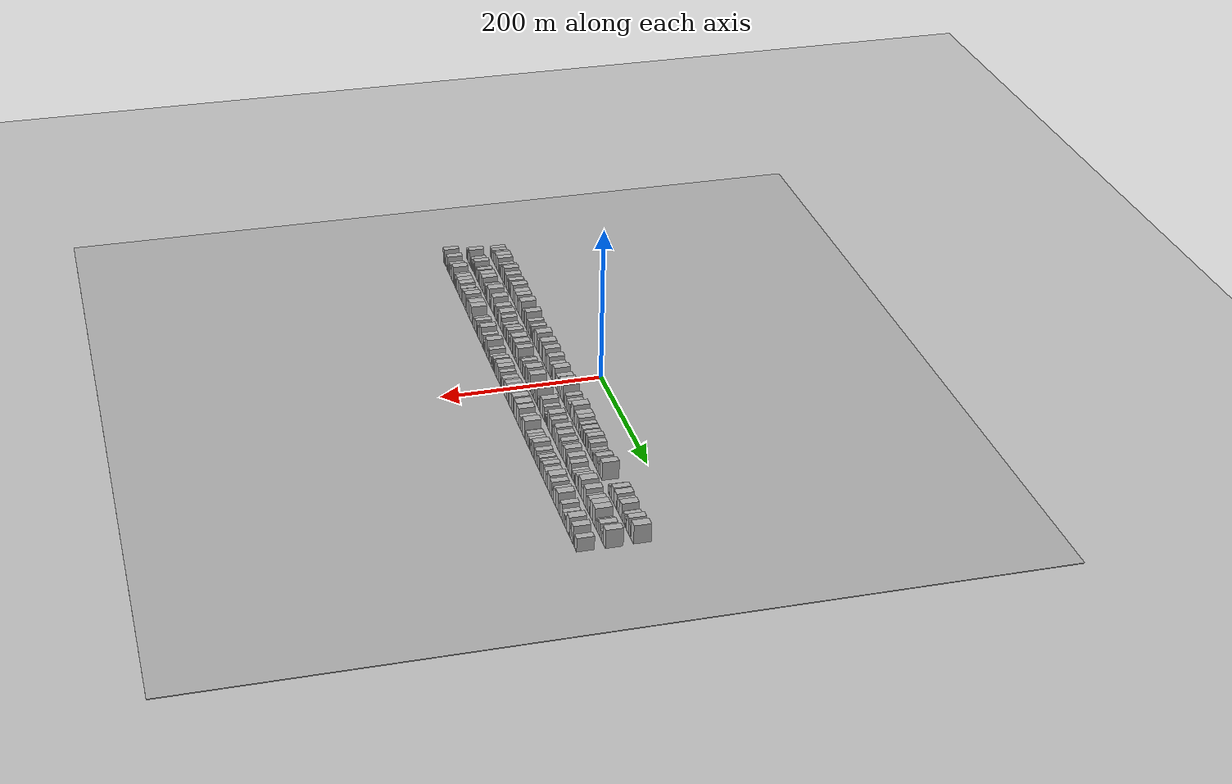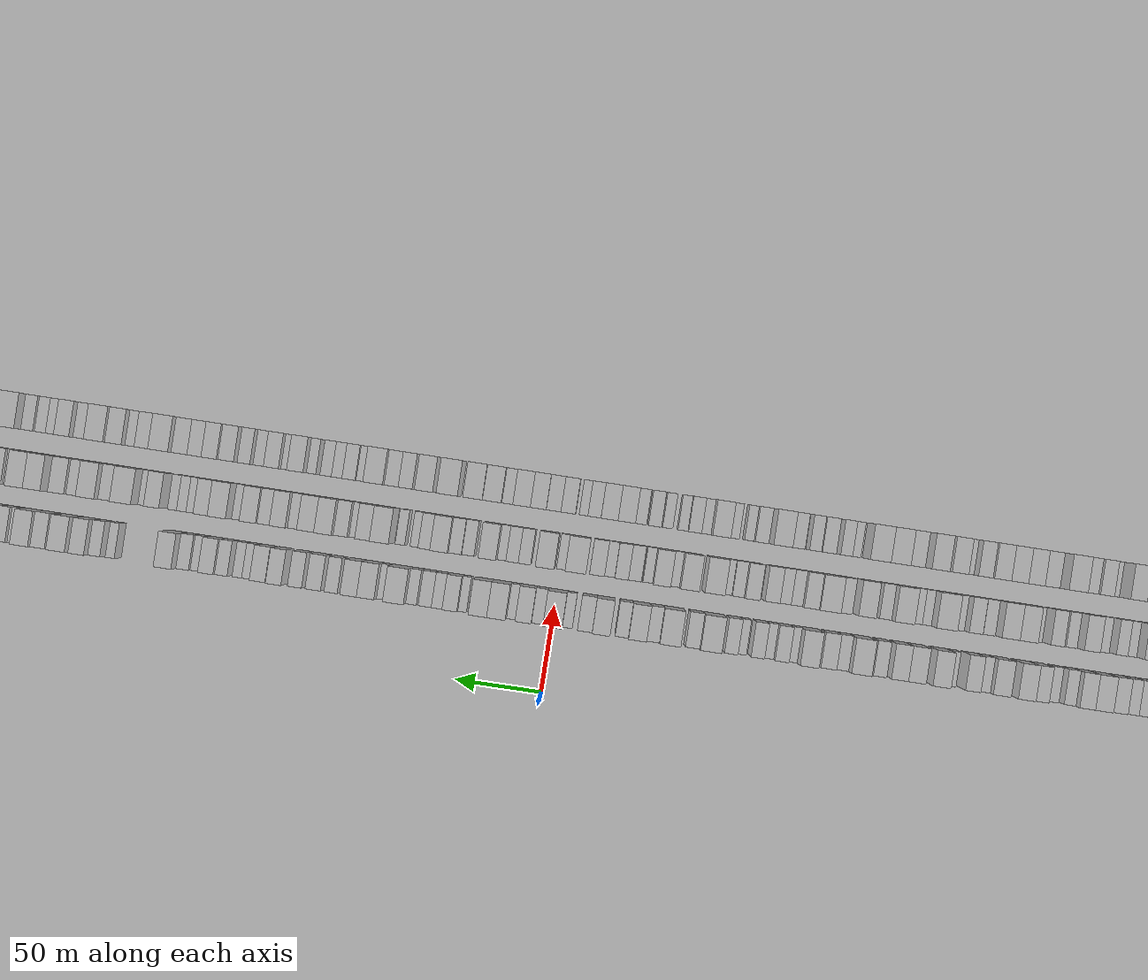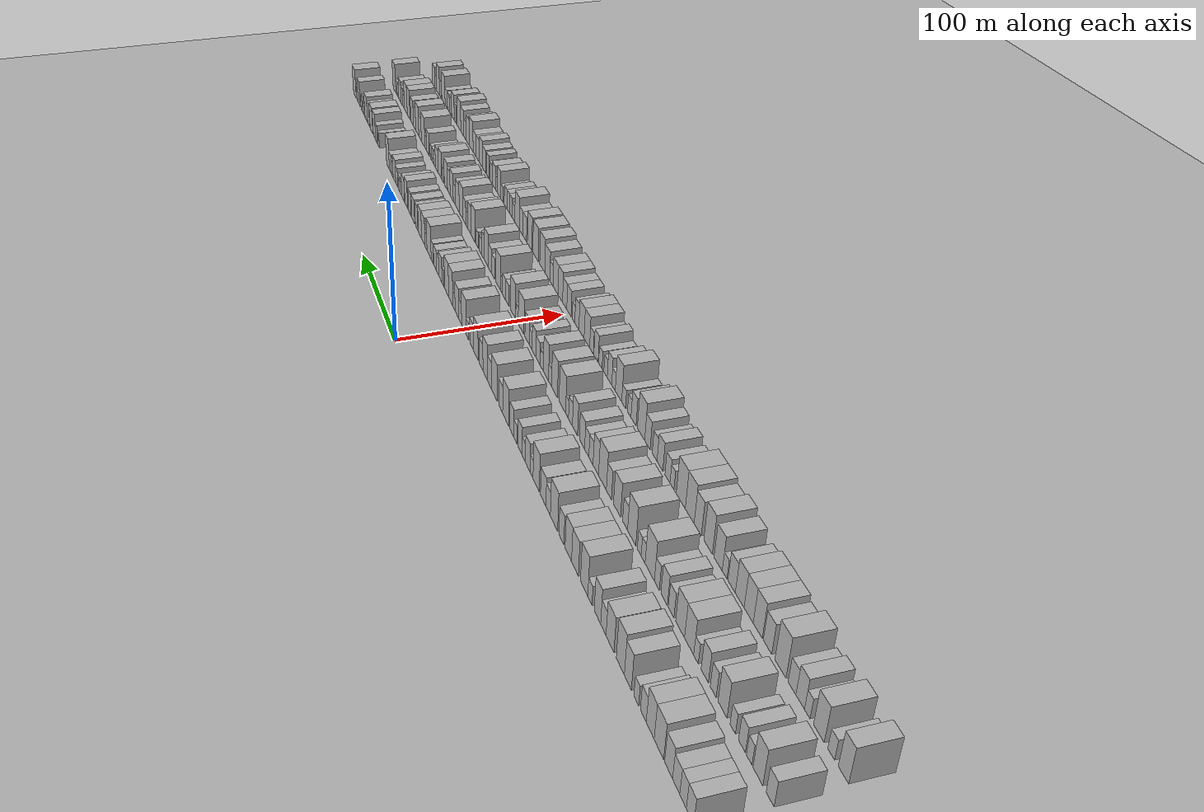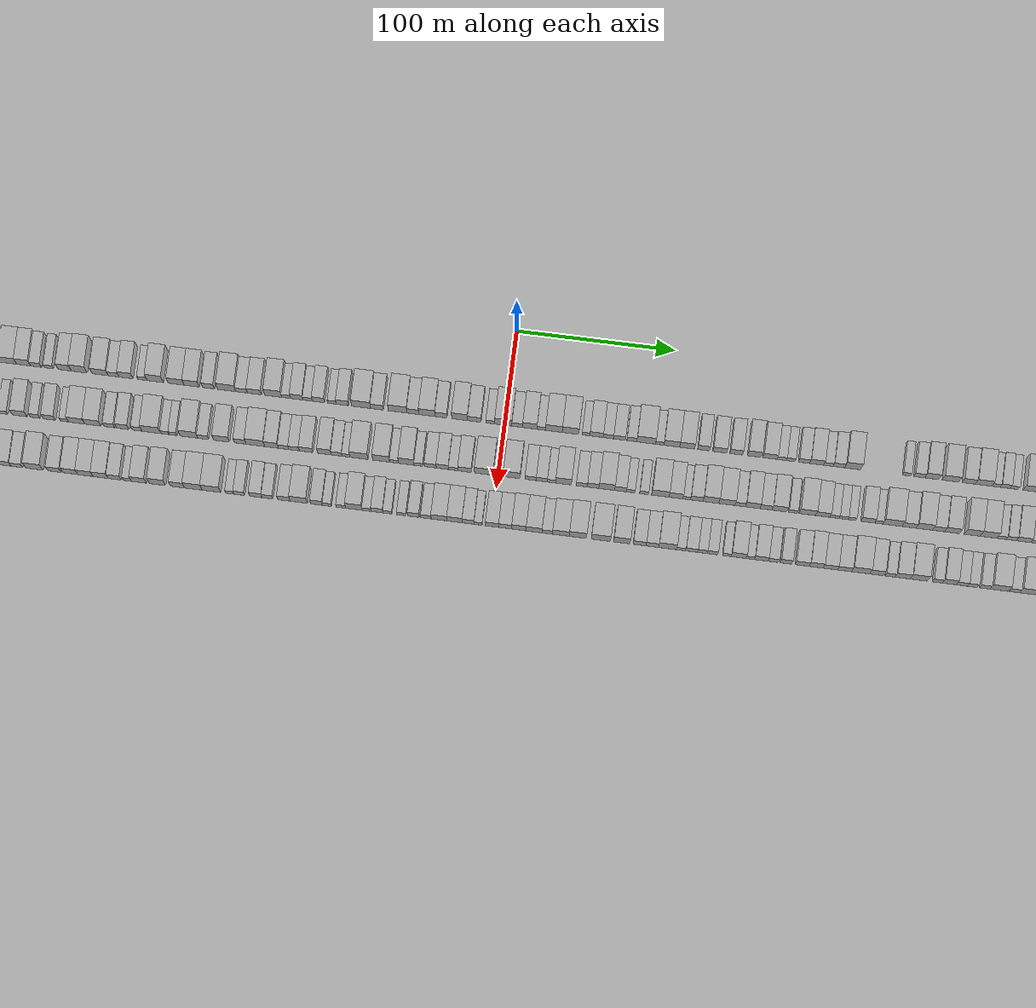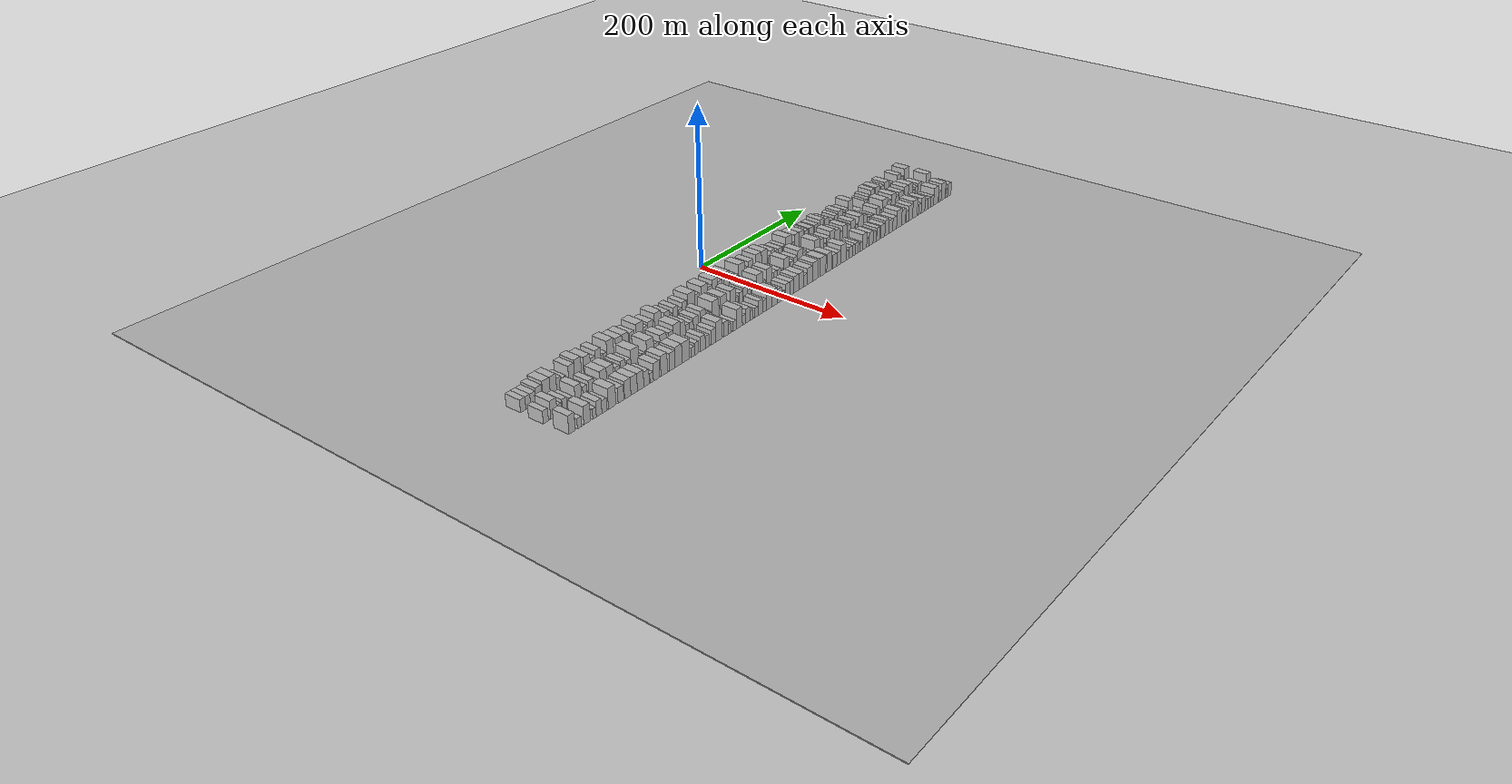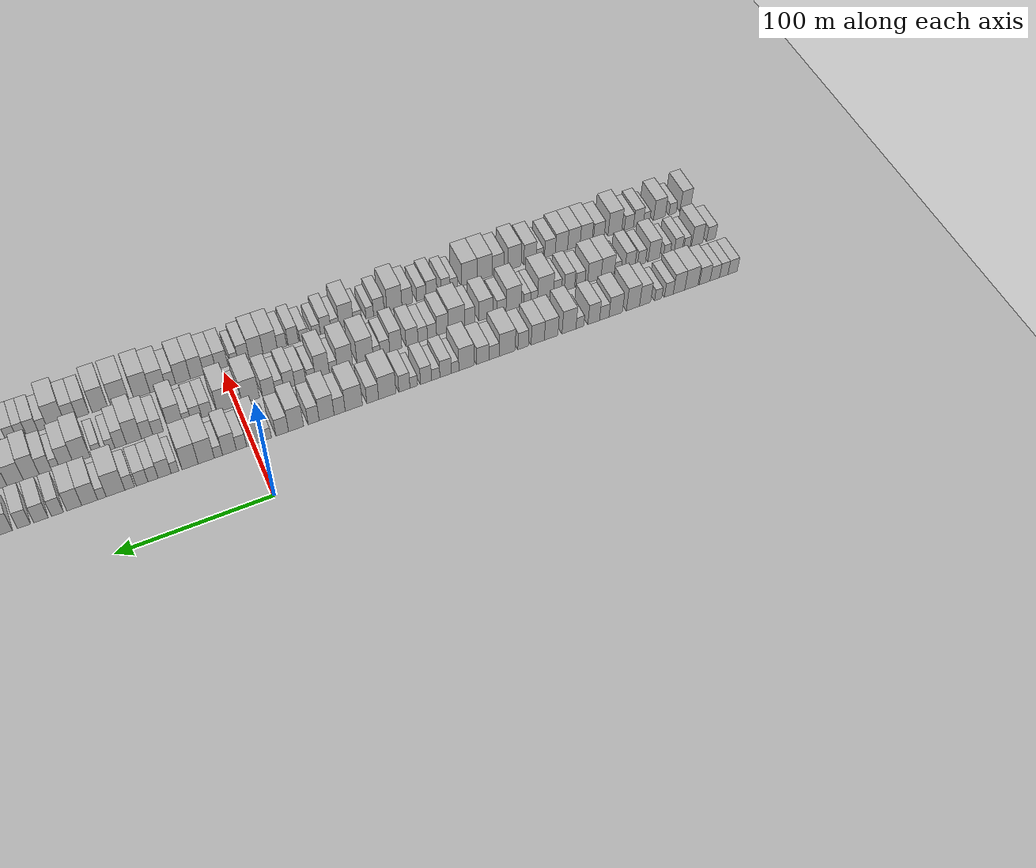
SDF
<?xml version="1.0" encoding="utf-8"?>

<sdf version="1.6">

   <world name="default">

      <gui fullscreen="0">

         <camera name="user_camera">

            <pose>-15 0 4.57585 0 0 0</pose>

            <view_controller>orbit</view_controller>

         </camera>

      </gui>

      <scene>

         <sky>

           <clouds>

             <speed>12</speed>

           </clouds>

         </sky>

         <ambient>0.4 0.4 0.4 1</ambient>

         <background>0.7 0.7 0.7 1</background>

         <shadows>1</shadows>

      </scene>

      <gravity>0 0 -9.8066</gravity>

      <magnetic_field>6e-06 2.3e-05 -4.2e-05</magnetic_field>

      <physics default="0" name="default_physics" type="ode">

         <ode>

            <solver>

               <type>quick</type>

               <iters>10</iters>

               <sor>1.0</sor>

               <use_dynamic_moi_rescaling>0</use_dynamic_moi_rescaling>

            </solver>

            <constraints>

               <cfm>0</cfm>

               <erp>0.2</erp>

               <contact_max_correcting_vel>100</contact_max_correcting_vel>

               <contact_surface_layer>0.001</contact_surface_layer>

            </constraints>

         </ode>

         <max_step_size>0.004</max_step_size>

         <real_time_factor>1</real_time_factor>

         <real_time_update_rate>250</real_time_update_rate>

      </physics>

      <light name="sun" type="directional">

         <cast_shadows>1</cast_shadows>

         <pose>0 0 10 0 0 0</pose>

         <diffuse>0.8 0.8 0.8 1</diffuse>

         <specular>0.2 0.2 0.2 1</specular>

         <attenuation>

            <range>1000</range>

            <constant>0.9</constant>

            <linear>0.01</linear>

            <quadratic>0.001</quadratic>

         </attenuation>

         <direction>-0.5 0.1 -0.9</direction>

      </light>

      <include>

         <name>ground_plane_1</name>

         <uri>model://HANNAS_ground_plane</uri>

         <pose>0 0 0  0 0 0</pose>

      </include>

      <include>

         <name>ground_plane_2</name>

         <uri>model://HANNAS_ground_plane</uri>

         <pose>100 0 0  0 0 0</pose>

      </include>

      <model name="building_1">

         <static>1</static>

         <pose frame="">50.0000 -343.4006 0 0.000000 0.000000 0.000000</pose>

         <link name="link">

            <pose frame="">0 0 7.50 0 0 0</pose>

            <collision name="collision">

               <geometry>

                  <box>

                     <size>20.0000 7.1988 15.0000</size>

                  </box>

               </geometry>

               <max_contacts>10</max_contacts>

               <surface>

                  <contact>

                     <ode/>

                  </contact>

                  <bounce/>

                  <friction>

                     <torsional>

                        <ode/>

                     </torsional>

                     <ode/>

                  </friction>

               </surface>

            </collision>

            <visual name="visual">

               <cast_shadows>0</cast_shadows>

               <geometry>

                  <box>

                     <size>20.0000 7.1988 15.0000</size>

                  </box>

               </geometry>

               <material>

                  <script>

                     <uri>model://HANNAS_wall/materials/scripts</uri>

                     <uri>model://HANNAS_wall/materials/textures</uri>

                     <name>vrc/HANNAS_wall</name>

                  </script>

               </material>

            </visual>

            <self_collide>0</self_collide>

            <enable_wind>0</enable_wind>

            <kinematic>0</kinematic>

         </link>

      </model>

      <model name="building_2">

         <static>1</static>

         <pose frame="">50.0000 -336.5190 0 0.000000 0.000000 0.000000</pose>

         <link name="link">

            <pose frame="">0 0 7.50 0 0 0</pose>

            <collision name="collision">

               <geometry>

                  <box>

                     <size>20.0000 6.5644 15.0000</size>

                  </box>

               </geometry>

               <max_contacts>10</max_contacts>

               <surface>

                  <contact>

                     <ode/>

                  </contact>

                  <bounce/>

                  <friction>

                     <torsional>

                        <ode/>

                     </torsional>

                     <ode/>

                  </friction>

               </surface>

            </collision>

            <visual name="visual">

               <cast_shadows>0</cast_shadows>

               <geometry>

                  <box>

                     <size>20.0000 6.5644 15.0000</size>

                  </box>

               </geometry>

               <material>

                  <script>

                     <uri>model://HANNAS_wall/materials/scripts</uri>

                     <uri>model://HANNAS_wall/materials/textures</uri>

                     <name>vrc/HANNAS_wall</name>

                  </script>

               </material>

            </visual>

            <self_collide>0</self_collide>

            <enable_wind>0</enable_wind>

            <kinematic>0</kinematic>

         </link>

      </model>

      <model name="building_3">

         <static>1</static>

         <pose frame="">50.0000 -329.5432 0 0.000000 0.000000 0.000000</pose>

         <link name="link">

            <pose frame="">0 0 7.50 0 0 0</pose>

            <collision name="collision">

               <geometry>

                  <box>

                     <size>20.0000 7.3872 15.0000</size>

                  </box>

               </geometry>

               <max_contacts>10</max_contacts>

               <surface>

                  <contact>

                     <ode/>

                  </contact>

                  <bounce/>

                  <friction>

                     <torsional>

                        <ode/>

                     </torsional>

                     <ode/>

                  </friction>

               </surface>

            </collision>

            <visual name="visual">

               <cast_shadows>0</cast_shadows>

               <geometry>

                  <box>

                     <size>20.0000 7.3872 15.0000</size>

                  </box>

               </geometry>

               <material>

                  <script>

                     <uri>model://HANNAS_wall/materials/scripts</uri>

                     <uri>model://HANNAS_wall/materials/textures</uri>

                     <name>vrc/HANNAS_wall</name>

                  </script>

               </material>

            </visual>

            <self_collide>0</self_collide>

            <enable_wind>0</enable_wind>

            <kinematic>0</kinematic>

         </link>

      </model>

      <model name="building_4">

         <static>1</static>

         <pose frame="">50.0000 -321.6905 0 0.000000 0.000000 0.000000</pose>

         <link name="link">

            <pose frame="">0 0 9.00 0 0 0</pose>

            <collision name="collision">

               <geometry>

                  <box>

                     <size>20.0000 8.3181 18.0000</size>

                  </box>

               </geometry>

               <max_contacts>10</max_contacts>

               <surface>

                  <contact>

                     <ode/>

                  </contact>

                  <bounce/>

                  <friction>

                     <torsional>

                        <ode/>

                     </torsional>

                     <ode/>

                  </friction>

               </surface>

            </collision>

            <visual name="visual">

               <cast_shadows>0</cast_shadows>

               <geometry>

                  <box>

                     <size>20.0000 8.3181 18.0000</size>

                  </box>

               </geometry>

               <material>

                  <script>

                     <uri>model://HANNAS_wall/materials/scripts</uri>

                     <uri>model://HANNAS_wall/materials/textures</uri>

                     <name>vrc/HANNAS_wall</name>

                  </script>

               </material>

            </visual>

            <self_collide>0</self_collide>

            <enable_wind>0</enable_wind>

            <kinematic>0</kinematic>

         </link>

      </model>

      <model name="building_5">

         <static>1</static>

         <pose frame="">50.0000 -311.4333 0 0.000000 0.000000 0.000000</pose>

         <link name="link">

            <pose frame="">0 0 10.50 0 0 0</pose>

            <collision name="collision">

               <geometry>

                  <box>

                     <size>20.0000 10.1962 21.0000</size>

                  </box>

               </geometry>

               <max_contacts>10</max_contacts>

               <surface>

                  <contact>

                     <ode/>

                  </contact>

                  <bounce/>

                  <friction>

                     <torsional>

                        <ode/>

                     </torsional>

                     <ode/>

                  </friction>

               </surface>

            </collision>

            <visual name="visual">

               <cast_shadows>0</cast_shadows>

               <geometry>

                  <box>

                     <size>20.0000 10.1962 21.0000</size>

                  </box>

               </geometry>

               <material>

                  <script>

                     <uri>model://HANNAS_wall/materials/scripts</uri>

                     <uri>model://HANNAS_wall/materials/textures</uri>

                     <name>vrc/HANNAS_wall</name>

                  </script>

               </material>

            </visual>

            <self_collide>0</self_collide>

            <enable_wind>0</enable_wind>

            <kinematic>0</kinematic>

         </link>

      </model>

      <model name="building_6">

         <static>1</static>

         <pose frame="">50.0000 -301.9019 0 0.000000 0.000000 0.000000</pose>

         <link name="link">

            <pose frame="">0 0 10.50 0 0 0</pose>

            <collision name="collision">

               <geometry>

                  <box>

                     <size>20.0000 8.8667 21.0000</size>

                  </box>

               </geometry>

               <max_contacts>10</max_contacts>

               <surface>

                  <contact>

                     <ode/>

                  </contact>

                  <bounce/>

                  <friction>

                     <torsional>

                        <ode/>

                     </torsional>

                     <ode/>

                  </friction>

               </surface>

            </collision>

            <visual name="visual">

               <cast_shadows>0</cast_shadows>

               <geometry>

                  <box>

                     <size>20.0000 8.8667 21.0000</size>

                  </box>

               </geometry>

               <material>

                  <script>

                     <uri>model://HANNAS_wall/materials/scripts</uri>

                     <uri>model://HANNAS_wall/materials/textures</uri>

                     <name>vrc/HANNAS_wall</name>

                  </script>

               </material>

            </visual>

            <self_collide>0</self_collide>

            <enable_wind>0</enable_wind>

            <kinematic>0</kinematic>

         </link>

      </model>

      <model name="building_7">

         <static>1</static>

         <pose frame="">50.0000 -294.1205 0 0.000000 0.000000 0.000000</pose>

         <link name="link">

            <pose frame="">0 0 7.50 0 0 0</pose>

            <collision name="collision">

               <geometry>

                  <box>

                     <size>20.0000 6.6961 15.0000</size>

                  </box>

               </geometry>

               <max_contacts>10</max_contacts>

               <surface>

                  <contact>

                     <ode/>

                  </contact>

                  <bounce/>

                  <friction>

                     <torsional>

                        <ode/>

                     </torsional>

                     <ode/>

                  </friction>

               </surface>

            </collision>

            <visual name="visual">

               <cast_shadows>0</cast_shadows>

               <geometry>

                  <box>

                     <size>20.0000 6.6961 15.0000</size>

                  </box>

               </geometry>

               <material>

                  <script>

                     <uri>model://HANNAS_wall/materials/scripts</uri>

                     <uri>model://HANNAS_wall/materials/textures</uri>

                     <name>vrc/HANNAS_wall</name>

                  </script>

               </material>

            </visual>

            <self_collide>0</self_collide>

            <enable_wind>0</enable_wind>

            <kinematic>0</kinematic>

         </link>

      </model>

      <model name="building_8">

         <static>1</static>

         <pose frame="">50.0000 -286.0262 0 0.000000 0.000000 0.000000</pose>

         <link name="link">

            <pose frame="">0 0 6.00 0 0 0</pose>

            <collision name="collision">

               <geometry>

                  <box>

                     <size>20.0000 5.4925 12.0000</size>

                  </box>

               </geometry>

               <max_contacts>10</max_contacts>

               <surface>

                  <contact>

                     <ode/>

                  </contact>

                  <bounce/>

                  <friction>

                     <torsional>

                        <ode/>

                     </torsional>

                     <ode/>

                  </friction>

               </surface>

            </collision>

            <visual name="visual">

               <cast_shadows>0</cast_shadows>

               <geometry>

                  <box>

                     <size>20.0000 5.4925 12.0000</size>

                  </box>

               </geometry>

               <material>

                  <script>

                     <uri>model://HANNAS_wall/materials/scripts</uri>

                     <uri>model://HANNAS_wall/materials/textures</uri>

                     <name>vrc/HANNAS_wall</name>

                  </script>

               </material>

            </visual>

            <self_collide>0</self_collide>

            <enable_wind>0</enable_wind>

            <kinematic>0</kinematic>

         </link>

      </model>

      <model name="building_9">

         <static>1</static>

         <pose frame="">50.0000 -276.0728 0 0.000000 0.000000 0.000000</pose>

         <link name="link">

            <pose frame="">0 0 10.50 0 0 0</pose>

            <collision name="collision">

               <geometry>

                  <box>

                     <size>20.0000 8.4143 21.0000</size>

                  </box>

               </geometry>

               <max_contacts>10</max_contacts>

               <surface>

                  <contact>

                     <ode/>

                  </contact>

                  <bounce/>

                  <friction>

                     <torsional>

                        <ode/>

                     </torsional>

                     <ode/>

                  </friction>

               </surface>

            </collision>

            <visual name="visual">

               <cast_shadows>0</cast_shadows>

               <geometry>

                  <box>

                     <size>20.0000 8.4143 21.0000</size>

                  </box>

               </geometry>

               <material>

                  <script>

                     <uri>model://HANNAS_wall/materials/scripts</uri>

                     <uri>model://HANNAS_wall/materials/textures</uri>

                     <name>vrc/HANNAS_wall</name>

                  </script>

               </material>

            </visual>

            <self_collide>0</self_collide>

            <enable_wind>0</enable_wind>

            <kinematic>0</kinematic>

         </link>

      </model>

      <model name="building_10">

         <static>1</static>

         <pose frame="">50.0000 -266.9094 0 0.000000 0.000000 0.000000</pose>

         <link name="link">

            <pose frame="">0 0 12.00 0 0 0</pose>

            <collision name="collision">

               <geometry>

                  <box>

                     <size>20.0000 9.9125 24.0000</size>

                  </box>

               </geometry>

               <max_contacts>10</max_contacts>

               <surface>

                  <contact>

                     <ode/>

                  </contact>

                  <bounce/>

                  <friction>

                     <torsional>

                        <ode/>

                     </torsional>

                     <ode/>

                  </friction>

               </surface>

            </collision>

            <visual name="visual">

               <cast_shadows>0</cast_shadows>

               <geometry>

                  <box>

                     <size>20.0000 9.9125 24.0000</size>

                  </box>

               </geometry>

               <material>

                  <script>

                     <uri>model://HANNAS_wall/materials/scripts</uri>

                     <uri>model://HANNAS_wall/materials/textures</uri>

                     <name>vrc/HANNAS_wall</name>

                  </script>

               </material>

            </visual>

            <self_collide>0</self_collide>

            <enable_wind>0</enable_wind>

            <kinematic>0</kinematic>

         </link>

      </model>

      <model name="building_11">

         <static>1</static>

         <pose frame="">50.0000 -253.9118 0 0.000000 0.000000 0.000000</pose>

         <link name="link">

            <pose frame="">0 0 10.50 0 0 0</pose>

            <collision name="collision">

               <geometry>

                  <box>

                     <size>20.0000 10.0828 21.0000</size>

                  </box>

               </geometry>

               <max_contacts>10</max_contacts>

               <surface>

                  <contact>

                     <ode/>

                  </contact>

                  <bounce/>

                  <friction>

                     <torsional>

                        <ode/>

                     </torsional>

                     <ode/>

                  </friction>

               </surface>

            </collision>

            <visual name="visual">

               <cast_shadows>0</cast_shadows>

               <geometry>

                  <box>

                     <size>20.0000 10.0828 21.0000</size>

                  </box>

               </geometry>

               <material>

                  <script>

                     <uri>model://HANNAS_wall/materials/scripts</uri>

                     <uri>model://HANNAS_wall/materials/textures</uri>

                     <name>vrc/HANNAS_wall</name>

                  </script>

               </material>

            </visual>

            <self_collide>0</self_collide>

            <enable_wind>0</enable_wind>

            <kinematic>0</kinematic>

         </link>

      </model>

      <model name="building_12">

         <static>1</static>

         <pose frame="">50.0000 -245.3483 0 0.000000 0.000000 0.000000</pose>

         <link name="link">

            <pose frame="">0 0 7.50 0 0 0</pose>

            <collision name="collision">

               <geometry>

                  <box>

                     <size>20.0000 7.0441 15.0000</size>

                  </box>

               </geometry>

               <max_contacts>10</max_contacts>

               <surface>

                  <contact>

                     <ode/>

                  </contact>

                  <bounce/>

                  <friction>

                     <torsional>

                        <ode/>

                     </torsional>

                     <ode/>

                  </friction>

               </surface>

            </collision>

            <visual name="visual">

               <cast_shadows>0</cast_shadows>

               <geometry>

                  <box>

                     <size>20.0000 7.0441 15.0000</size>

                  </box>

               </geometry>

               <material>

                  <script>

                     <uri>model://HANNAS_wall/materials/scripts</uri>

                     <uri>model://HANNAS_wall/materials/textures</uri>

                     <name>vrc/HANNAS_wall</name>

                  </script>

               </material>

            </visual>

            <self_collide>0</self_collide>

            <enable_wind>0</enable_wind>

            <kinematic>0</kinematic>

         </link>

      </model>

      <model name="building_13">

         <static>1</static>

         <pose frame="">50.0000 -237.5058 0 0.000000 0.000000 0.000000</pose>

         <link name="link">

            <pose frame="">0 0 10.50 0 0 0</pose>

            <collision name="collision">

               <geometry>

                  <box>

                     <size>20.0000 8.6408 21.0000</size>

                  </box>

               </geometry>

               <max_contacts>10</max_contacts>

               <surface>

                  <contact>

                     <ode/>

                  </contact>

                  <bounce/>

                  <friction>

                     <torsional>

                        <ode/>

                     </torsional>

                     <ode/>

                  </friction>

               </surface>

            </collision>

            <visual name="visual">

               <cast_shadows>0</cast_shadows>

               <geometry>

                  <box>

                     <size>20.0000 8.6408 21.0000</size>

                  </box>

               </geometry>

               <material>

                  <script>

                     <uri>model://HANNAS_wall/materials/scripts</uri>

                     <uri>model://HANNAS_wall/materials/textures</uri>

                     <name>vrc/HANNAS_wall</name>

                  </script>

               </material>

            </visual>

            <self_collide>0</self_collide>

            <enable_wind>0</enable_wind>

            <kinematic>0</kinematic>

         </link>

      </model>

      <model name="building_14">

         <static>1</static>

         <pose frame="">50.0000 -227.2770 0 0.000000 0.000000 0.000000</pose>

         <link name="link">

            <pose frame="">0 0 6.00 0 0 0</pose>

            <collision name="collision">

               <geometry>

                  <box>

                     <size>20.0000 5.8169 12.0000</size>

                  </box>

               </geometry>

               <max_contacts>10</max_contacts>

               <surface>

                  <contact>

                     <ode/>

                  </contact>

                  <bounce/>

                  <friction>

                     <torsional>

                        <ode/>

                     </torsional>

                     <ode/>

                  </friction>

               </surface>

            </collision>

            <visual name="visual">

               <cast_shadows>0</cast_shadows>

               <geometry>

                  <box>

                     <size>20.0000 5.8169 12.0000</size>

                  </box>

               </geometry>

               <material>

                  <script>

                     <uri>model://HANNAS_wall/materials/scripts</uri>

                     <uri>model://HANNAS_wall/materials/textures</uri>

                     <name>vrc/HANNAS_wall</name>

                  </script>

               </material>

            </visual>

            <self_collide>0</self_collide>

            <enable_wind>0</enable_wind>

            <kinematic>0</kinematic>

         </link>

      </model>

      <model name="building_15">

         <static>1</static>

         <pose frame="">50.0000 -219.2391 0 0.000000 0.000000 0.000000</pose>

         <link name="link">

            <pose frame="">0 0 12.00 0 0 0</pose>

            <collision name="collision">

               <geometry>

                  <box>

                     <size>20.0000 10.2589 24.0000</size>

                  </box>

               </geometry>

               <max_contacts>10</max_contacts>

               <surface>

                  <contact>

                     <ode/>

                  </contact>

                  <bounce/>

                  <friction>

                     <torsional>

                        <ode/>

                     </torsional>

                     <ode/>

                  </friction>

               </surface>

            </collision>

            <visual name="visual">

               <cast_shadows>0</cast_shadows>

               <geometry>

                  <box>

                     <size>20.0000 10.2589 24.0000</size>

                  </box>

               </geometry>

               <material>

                  <script>

                     <uri>model://HANNAS_wall/materials/scripts</uri>

                     <uri>model://HANNAS_wall/materials/textures</uri>

                     <name>vrc/HANNAS_wall</name>

                  </script>

               </material>

            </visual>

            <self_collide>0</self_collide>

            <enable_wind>0</enable_wind>

            <kinematic>0</kinematic>

         </link>

      </model>

      <model name="building_16">

         <static>1</static>

         <pose frame="">50.0000 -206.1436 0 0.000000 0.000000 0.000000</pose>

         <link name="link">

            <pose frame="">0 0 10.50 0 0 0</pose>

            <collision name="collision">

               <geometry>

                  <box>

                     <size>20.0000 9.9321 21.0000</size>

                  </box>

               </geometry>

               <max_contacts>10</max_contacts>

               <surface>

                  <contact>

                     <ode/>

                  </contact>

                  <bounce/>

                  <friction>

                     <torsional>

                        <ode/>

                     </torsional>

                     <ode/>

                  </friction>

               </surface>

            </collision>

            <visual name="visual">

               <cast_shadows>0</cast_shadows>

               <geometry>

                  <box>

                     <size>20.0000 9.9321 21.0000</size>

                  </box>

               </geometry>

               <material>

                  <script>

                     <uri>model://HANNAS_wall/materials/scripts</uri>

                     <uri>model://HANNAS_wall/materials/textures</uri>

                     <name>vrc/HANNAS_wall</name>

                  </script>

               </material>

            </visual>

            <self_collide>0</self_collide>

            <enable_wind>0</enable_wind>

            <kinematic>0</kinematic>

         </link>

      </model>

      <model name="building_17">

         <static>1</static>

         <pose frame="">50.0000 -196.3686 0 0.000000 0.000000 0.000000</pose>

         <link name="link">

            <pose frame="">0 0 10.50 0 0 0</pose>

            <collision name="collision">

               <geometry>

                  <box>

                     <size>20.0000 9.6181 21.0000</size>

                  </box>

               </geometry>

               <max_contacts>10</max_contacts>

               <surface>

                  <contact>

                     <ode/>

                  </contact>

                  <bounce/>

                  <friction>

                     <torsional>

                        <ode/>

                     </torsional>

                     <ode/>

                  </friction>

               </surface>

            </collision>

            <visual name="visual">

               <cast_shadows>0</cast_shadows>

               <geometry>

                  <box>

                     <size>20.0000 9.6181 21.0000</size>

                  </box>

               </geometry>

               <material>

                  <script>

                     <uri>model://HANNAS_wall/materials/scripts</uri>

                     <uri>model://HANNAS_wall/materials/textures</uri>

                     <name>vrc/HANNAS_wall</name>

                  </script>

               </material>

            </visual>

            <self_collide>0</self_collide>

            <enable_wind>0</enable_wind>

            <kinematic>0</kinematic>

         </link>

      </model>

      <model name="building_18">

         <static>1</static>

         <pose frame="">50.0000 -185.7863 0 0.000000 0.000000 0.000000</pose>

         <link name="link">

            <pose frame="">0 0 9.00 0 0 0</pose>

            <collision name="collision">

               <geometry>

                  <box>

                     <size>20.0000 7.5465 18.0000</size>

                  </box>

               </geometry>

               <max_contacts>10</max_contacts>

               <surface>

                  <contact>

                     <ode/>

                  </contact>

                  <bounce/>

                  <friction>

                     <torsional>

                        <ode/>

                     </torsional>

                     <ode/>

                  </friction>

               </surface>

            </collision>

            <visual name="visual">

               <cast_shadows>0</cast_shadows>

               <geometry>

                  <box>

                     <size>20.0000 7.5465 18.0000</size>

                  </box>

               </geometry>

               <material>

                  <script>

                     <uri>model://HANNAS_wall/materials/scripts</uri>

                     <uri>model://HANNAS_wall/materials/textures</uri>

                     <name>vrc/HANNAS_wall</name>

                  </script>

               </material>

            </visual>

            <self_collide>0</self_collide>

            <enable_wind>0</enable_wind>

            <kinematic>0</kinematic>

         </link>

      </model>

      <model name="building_19">

         <static>1</static>

         <pose frame="">50.0000 -174.3009 0 0.000000 0.000000 0.000000</pose>

         <link name="link">

            <pose frame="">0 0 12.00 0 0 0</pose>

            <collision name="collision">

               <geometry>

                  <box>

                     <size>20.0000 11.4243 24.0000</size>

                  </box>

               </geometry>

               <max_contacts>10</max_contacts>

               <surface>

                  <contact>

                     <ode/>

                  </contact>

                  <bounce/>

                  <friction>

                     <torsional>

                        <ode/>

                     </torsional>

                     <ode/>

                  </friction>

               </surface>

            </collision>

            <visual name="visual">

               <cast_shadows>0</cast_shadows>

               <geometry>

                  <box>

                     <size>20.0000 11.4243 24.0000</size>

                  </box>

               </geometry>

               <material>

                  <script>

                     <uri>model://HANNAS_wall/materials/scripts</uri>

                     <uri>model://HANNAS_wall/materials/textures</uri>

                     <name>vrc/HANNAS_wall</name>

                  </script>

               </material>

            </visual>

            <self_collide>0</self_collide>

            <enable_wind>0</enable_wind>

            <kinematic>0</kinematic>

         </link>

      </model>

      <model name="building_20">

         <static>1</static>

         <pose frame="">50.0000 -164.9584 0 0.000000 0.000000 0.000000</pose>

         <link name="link">

            <pose frame="">0 0 7.50 0 0 0</pose>

            <collision name="collision">

               <geometry>

                  <box>

                     <size>20.0000 7.2607 15.0000</size>

                  </box>

               </geometry>

               <max_contacts>10</max_contacts>

               <surface>

                  <contact>

                     <ode/>

                  </contact>

                  <bounce/>

                  <friction>

                     <torsional>

                        <ode/>

                     </torsional>

                     <ode/>

                  </friction>

               </surface>

            </collision>

            <visual name="visual">

               <cast_shadows>0</cast_shadows>

               <geometry>

                  <box>

                     <size>20.0000 7.2607 15.0000</size>

                  </box>

               </geometry>

               <material>

                  <script>

                     <uri>model://HANNAS_wall/materials/scripts</uri>

                     <uri>model://HANNAS_wall/materials/textures</uri>

                     <name>vrc/HANNAS_wall</name>

                  </script>

               </material>

            </visual>

            <self_collide>0</self_collide>

            <enable_wind>0</enable_wind>

            <kinematic>0</kinematic>

         </link>

      </model>

      <model name="building_21">

         <static>1</static>

         <pose frame="">50.0000 -156.8758 0 0.000000 0.000000 0.000000</pose>

         <link name="link">

            <pose frame="">0 0 9.00 0 0 0</pose>

            <collision name="collision">

               <geometry>

                  <box>

                     <size>20.0000 8.9044 18.0000</size>

                  </box>

               </geometry>

               <max_contacts>10</max_contacts>

               <surface>

                  <contact>

                     <ode/>

                  </contact>

                  <bounce/>

                  <friction>

                     <torsional>

                        <ode/>

                     </torsional>

                     <ode/>

                  </friction>

               </surface>

            </collision>

            <visual name="visual">

               <cast_shadows>0</cast_shadows>

               <geometry>

                  <box>

                     <size>20.0000 8.9044 18.0000</size>

                  </box>

               </geometry>

               <material>

                  <script>

                     <uri>model://HANNAS_wall/materials/scripts</uri>

                     <uri>model://HANNAS_wall/materials/textures</uri>

                     <name>vrc/HANNAS_wall</name>

                  </script>

               </material>

            </visual>

            <self_collide>0</self_collide>

            <enable_wind>0</enable_wind>

            <kinematic>0</kinematic>

         </link>

      </model>

      <model name="building_22">

         <static>1</static>

         <pose frame="">50.0000 -145.1113 0 0.000000 0.000000 0.000000</pose>

         <link name="link">

            <pose frame="">0 0 12.00 0 0 0</pose>

            <collision name="collision">

               <geometry>

                  <box>

                     <size>20.0000 10.6248 24.0000</size>

                  </box>

               </geometry>

               <max_contacts>10</max_contacts>

               <surface>

                  <contact>

                     <ode/>

                  </contact>

                  <bounce/>

                  <friction>

                     <torsional>

                        <ode/>

                     </torsional>

                     <ode/>

                  </friction>

               </surface>

            </collision>

            <visual name="visual">

               <cast_shadows>0</cast_shadows>

               <geometry>

                  <box>

                     <size>20.0000 10.6248 24.0000</size>

                  </box>

               </geometry>

               <material>

                  <script>

                     <uri>model://HANNAS_wall/materials/scripts</uri>

                     <uri>model://HANNAS_wall/materials/textures</uri>

                     <name>vrc/HANNAS_wall</name>

                  </script>

               </material>

            </visual>

            <self_collide>0</self_collide>

            <enable_wind>0</enable_wind>

            <kinematic>0</kinematic>

         </link>

      </model>

      <model name="building_23">

         <static>1</static>

         <pose frame="">50.0000 -137.1146 0 0.000000 0.000000 0.000000</pose>

         <link name="link">

            <pose frame="">0 0 6.00 0 0 0</pose>

            <collision name="collision">

               <geometry>

                  <box>

                     <size>20.0000 5.3684 12.0000</size>

                  </box>

               </geometry>

               <max_contacts>10</max_contacts>

               <surface>

                  <contact>

                     <ode/>

                  </contact>

                  <bounce/>

                  <friction>

                     <torsional>

                        <ode/>

                     </torsional>

                     <ode/>

                  </friction>

               </surface>

            </collision>

            <visual name="visual">

               <cast_shadows>0</cast_shadows>

               <geometry>

                  <box>

                     <size>20.0000 5.3684 12.0000</size>

                  </box>

               </geometry>

               <material>

                  <script>

                     <uri>model://HANNAS_wall/materials/scripts</uri>

                     <uri>model://HANNAS_wall/materials/textures</uri>

                     <name>vrc/HANNAS_wall</name>

                  </script>

               </material>

            </visual>

            <self_collide>0</self_collide>

            <enable_wind>0</enable_wind>

            <kinematic>0</kinematic>

         </link>

      </model>

      <model name="building_24">

         <static>1</static>

         <pose frame="">50.0000 -130.4497 0 0.000000 0.000000 0.000000</pose>

         <link name="link">

            <pose frame="">0 0 9.00 0 0 0</pose>

            <collision name="collision">

               <geometry>

                  <box>

                     <size>20.0000 7.9614 18.0000</size>

                  </box>

               </geometry>

               <max_contacts>10</max_contacts>

               <surface>

                  <contact>

                     <ode/>

                  </contact>

                  <bounce/>

                  <friction>

                     <torsional>

                        <ode/>

                     </torsional>

                     <ode/>

                  </friction>

               </surface>

            </collision>

            <visual name="visual">

               <cast_shadows>0</cast_shadows>

               <geometry>

                  <box>

                     <size>20.0000 7.9614 18.0000</size>

                  </box>

               </geometry>

               <material>

                  <script>

                     <uri>model://HANNAS_wall/materials/scripts</uri>

                     <uri>model://HANNAS_wall/materials/textures</uri>

                     <name>vrc/HANNAS_wall</name>

                  </script>

               </material>

            </visual>

            <self_collide>0</self_collide>

            <enable_wind>0</enable_wind>

            <kinematic>0</kinematic>

         </link>

      </model>

      <model name="building_25">

         <static>1</static>

         <pose frame="">50.0000 -123.5335 0 0.000000 0.000000 0.000000</pose>

         <link name="link">

            <pose frame="">0 0 6.00 0 0 0</pose>

            <collision name="collision">

               <geometry>

                  <box>

                     <size>20.0000 5.8710 12.0000</size>

                  </box>

               </geometry>

               <max_contacts>10</max_contacts>

               <surface>

                  <contact>

                     <ode/>

                  </contact>

                  <bounce/>

                  <friction>

                     <torsional>

                        <ode/>

                     </torsional>

                     <ode/>

                  </friction>

               </surface>

            </collision>

            <visual name="visual">

               <cast_shadows>0</cast_shadows>

               <geometry>

                  <box>

                     <size>20.0000 5.8710 12.0000</size>

                  </box>

               </geometry>

               <material>

                  <script>

                     <uri>model://HANNAS_wall/materials/scripts</uri>

                     <uri>model://HANNAS_wall/materials/textures</uri>

                     <name>vrc/HANNAS_wall</name>

                  </script>

               </material>

            </visual>

            <self_collide>0</self_collide>

            <enable_wind>0</enable_wind>

            <kinematic>0</kinematic>

         </link>

      </model>

      <model name="building_26">

         <static>1</static>

         <pose frame="">50.0000 -116.7605 0 0.000000 0.000000 0.000000</pose>

         <link name="link">

            <pose frame="">0 0 9.00 0 0 0</pose>

            <collision name="collision">

               <geometry>

                  <box>

                     <size>20.0000 7.6751 18.0000</size>

                  </box>

               </geometry>

               <max_contacts>10</max_contacts>

               <surface>

                  <contact>

                     <ode/>

                  </contact>

                  <bounce/>

                  <friction>

                     <torsional>

                        <ode/>

                     </torsional>

                     <ode/>

                  </friction>

               </surface>

            </collision>

            <visual name="visual">

               <cast_shadows>0</cast_shadows>

               <geometry>

                  <box>

                     <size>20.0000 7.6751 18.0000</size>

                  </box>

               </geometry>

               <material>

                  <script>

                     <uri>model://HANNAS_wall/materials/scripts</uri>

                     <uri>model://HANNAS_wall/materials/textures</uri>

                     <name>vrc/HANNAS_wall</name>

                  </script>

               </material>

            </visual>

            <self_collide>0</self_collide>

            <enable_wind>0</enable_wind>

            <kinematic>0</kinematic>

         </link>

      </model>

      <model name="building_27">

         <static>1</static>

         <pose frame="">50.0000 -108.2501 0 0.000000 0.000000 0.000000</pose>

         <link name="link">

            <pose frame="">0 0 6.00 0 0 0</pose>

            <collision name="collision">

               <geometry>

                  <box>

                     <size>20.0000 5.3455 12.0000</size>

                  </box>

               </geometry>

               <max_contacts>10</max_contacts>

               <surface>

                  <contact>

                     <ode/>

                  </contact>

                  <bounce/>

                  <friction>

                     <torsional>

                        <ode/>

                     </torsional>

                     <ode/>

                  </friction>

               </surface>

            </collision>

            <visual name="visual">

               <cast_shadows>0</cast_shadows>

               <geometry>

                  <box>

                     <size>20.0000 5.3455 12.0000</size>

                  </box>

               </geometry>

               <material>

                  <script>

                     <uri>model://HANNAS_wall/materials/scripts</uri>

                     <uri>model://HANNAS_wall/materials/textures</uri>

                     <name>vrc/HANNAS_wall</name>

                  </script>

               </material>

            </visual>

            <self_collide>0</self_collide>

            <enable_wind>0</enable_wind>

            <kinematic>0</kinematic>

         </link>

      </model>

      <model name="building_28">

         <static>1</static>

         <pose frame="">50.0000 -101.7485 0 0.000000 0.000000 0.000000</pose>

         <link name="link">

            <pose frame="">0 0 9.00 0 0 0</pose>

            <collision name="collision">

               <geometry>

                  <box>

                     <size>20.0000 7.6578 18.0000</size>

                  </box>

               </geometry>

               <max_contacts>10</max_contacts>

               <surface>

                  <contact>

                     <ode/>

                  </contact>

                  <bounce/>

                  <friction>

                     <torsional>

                        <ode/>

                     </torsional>

                     <ode/>

                  </friction>

               </surface>

            </collision>

            <visual name="visual">

               <cast_shadows>0</cast_shadows>

               <geometry>

                  <box>

                     <size>20.0000 7.6578 18.0000</size>

                  </box>

               </geometry>

               <material>

                  <script>

                     <uri>model://HANNAS_wall/materials/scripts</uri>

                     <uri>model://HANNAS_wall/materials/textures</uri>

                     <name>vrc/HANNAS_wall</name>

                  </script>

               </material>

            </visual>

            <self_collide>0</self_collide>

            <enable_wind>0</enable_wind>

            <kinematic>0</kinematic>

         </link>

      </model>

      <model name="building_29">

         <static>1</static>

         <pose frame="">50.0000 -89.9516 0 0.000000 0.000000 0.000000</pose>

         <link name="link">

            <pose frame="">0 0 12.00 0 0 0</pose>

            <collision name="collision">

               <geometry>

                  <box>

                     <size>20.0000 11.9362 24.0000</size>

                  </box>

               </geometry>

               <max_contacts>10</max_contacts>

               <surface>

                  <contact>

                     <ode/>

                  </contact>

                  <bounce/>

                  <friction>

                     <torsional>

                        <ode/>

                     </torsional>

                     <ode/>

                  </friction>

               </surface>

            </collision>

            <visual name="visual">

               <cast_shadows>0</cast_shadows>

               <geometry>

                  <box>

                     <size>20.0000 11.9362 24.0000</size>

                  </box>

               </geometry>

               <material>

                  <script>

                     <uri>model://HANNAS_wall/materials/scripts</uri>

                     <uri>model://HANNAS_wall/materials/textures</uri>

                     <name>vrc/HANNAS_wall</name>

                  </script>

               </material>

            </visual>

            <self_collide>0</self_collide>

            <enable_wind>0</enable_wind>

            <kinematic>0</kinematic>

         </link>

      </model>

      <model name="building_30">

         <static>1</static>

         <pose frame="">50.0000 -79.9415 0 0.000000 0.000000 0.000000</pose>

         <link name="link">

            <pose frame="">0 0 9.00 0 0 0</pose>

            <collision name="collision">

               <geometry>

                  <box>

                     <size>20.0000 8.0840 18.0000</size>

                  </box>

               </geometry>

               <max_contacts>10</max_contacts>

               <surface>

                  <contact>

                     <ode/>

                  </contact>

                  <bounce/>

                  <friction>

                     <torsional>

                        <ode/>

                     </torsional>

                     <ode/>

                  </friction>

               </surface>

            </collision>

            <visual name="visual">

               <cast_shadows>0</cast_shadows>

               <geometry>

                  <box>

                     <size>20.0000 8.0840 18.0000</size>

                  </box>

               </geometry>

               <material>

                  <script>

                     <uri>model://HANNAS_wall/materials/scripts</uri>

                     <uri>model://HANNAS_wall/materials/textures</uri>

                     <name>vrc/HANNAS_wall</name>

                  </script>

               </material>

            </visual>

            <self_collide>0</self_collide>

            <enable_wind>0</enable_wind>

            <kinematic>0</kinematic>

         </link>

      </model>

      <model name="building_31">

         <static>1</static>

         <pose frame="">50.0000 -67.0458 0 0.000000 0.000000 0.000000</pose>

         <link name="link">

            <pose frame="">0 0 12.00 0 0 0</pose>

            <collision name="collision">

               <geometry>

                  <box>

                     <size>20.0000 11.7074 24.0000</size>

                  </box>

               </geometry>

               <max_contacts>10</max_contacts>

               <surface>

                  <contact>

                     <ode/>

                  </contact>

                  <bounce/>

                  <friction>

                     <torsional>

                        <ode/>

                     </torsional>

                     <ode/>

                  </friction>

               </surface>

            </collision>

            <visual name="visual">

               <cast_shadows>0</cast_shadows>

               <geometry>

                  <box>

                     <size>20.0000 11.7074 24.0000</size>

                  </box>

               </geometry>

               <material>

                  <script>

                     <uri>model://HANNAS_wall/materials/scripts</uri>

                     <uri>model://HANNAS_wall/materials/textures</uri>

                     <name>vrc/HANNAS_wall</name>

                  </script>

               </material>

            </visual>

            <self_collide>0</self_collide>

            <enable_wind>0</enable_wind>

            <kinematic>0</kinematic>

         </link>

      </model>

      <model name="building_32">

         <static>1</static>

         <pose frame="">50.0000 -57.4610 0 0.000000 0.000000 0.000000</pose>

         <link name="link">

            <pose frame="">0 0 9.00 0 0 0</pose>

            <collision name="collision">

               <geometry>

                  <box>

                     <size>20.0000 7.4623 18.0000</size>

                  </box>

               </geometry>

               <max_contacts>10</max_contacts>

               <surface>

                  <contact>

                     <ode/>

                  </contact>

                  <bounce/>

                  <friction>

                     <torsional>

                        <ode/>

                     </torsional>

                     <ode/>

                  </friction>

               </surface>

            </collision>

            <visual name="visual">

               <cast_shadows>0</cast_shadows>

               <geometry>

                  <box>

                     <size>20.0000 7.4623 18.0000</size>

                  </box>

               </geometry>

               <material>

                  <script>

                     <uri>model://HANNAS_wall/materials/scripts</uri>

                     <uri>model://HANNAS_wall/materials/textures</uri>

                     <name>vrc/HANNAS_wall</name>

                  </script>

               </material>

            </visual>

            <self_collide>0</self_collide>

            <enable_wind>0</enable_wind>

            <kinematic>0</kinematic>

         </link>

      </model>

      <model name="building_33">

         <static>1</static>

         <pose frame="">50.0000 -48.6677 0 0.000000 0.000000 0.000000</pose>

         <link name="link">

            <pose frame="">0 0 12.00 0 0 0</pose>

            <collision name="collision">

               <geometry>

                  <box>

                     <size>20.0000 10.1242 24.0000</size>

                  </box>

               </geometry>

               <max_contacts>10</max_contacts>

               <surface>

                  <contact>

                     <ode/>

                  </contact>

                  <bounce/>

                  <friction>

                     <torsional>

                        <ode/>

                     </torsional>

                     <ode/>

                  </friction>

               </surface>

            </collision>

            <visual name="visual">

               <cast_shadows>0</cast_shadows>

               <geometry>

                  <box>

                     <size>20.0000 10.1242 24.0000</size>

                  </box>

               </geometry>

               <material>

                  <script>

                     <uri>model://HANNAS_wall/materials/scripts</uri>

                     <uri>model://HANNAS_wall/materials/textures</uri>

                     <name>vrc/HANNAS_wall</name>

                  </script>

               </material>

            </visual>

            <self_collide>0</self_collide>

            <enable_wind>0</enable_wind>

            <kinematic>0</kinematic>

         </link>

      </model>

      <model name="building_34">

         <static>1</static>

         <pose frame="">50.0000 -39.8887 0 0.000000 0.000000 0.000000</pose>

         <link name="link">

            <pose frame="">0 0 9.00 0 0 0</pose>

            <collision name="collision">

               <geometry>

                  <box>

                     <size>20.0000 7.4339 18.0000</size>

                  </box>

               </geometry>

               <max_contacts>10</max_contacts>

               <surface>

                  <contact>

                     <ode/>

                  </contact>

                  <bounce/>

                  <friction>

                     <torsional>

                        <ode/>

                     </torsional>

                     <ode/>

                  </friction>

               </surface>

            </collision>

            <visual name="visual">

               <cast_shadows>0</cast_shadows>

               <geometry>

                  <box>

                     <size>20.0000 7.4339 18.0000</size>

                  </box>

               </geometry>

               <material>

                  <script>

                     <uri>model://HANNAS_wall/materials/scripts</uri>

                     <uri>model://HANNAS_wall/materials/textures</uri>

                     <name>vrc/HANNAS_wall</name>

                  </script>

               </material>

            </visual>

            <self_collide>0</self_collide>

            <enable_wind>0</enable_wind>

            <kinematic>0</kinematic>

         </link>

      </model>

      <model name="building_35">

         <static>1</static>

         <pose frame="">50.0000 -28.1700 0 0.000000 0.000000 0.000000</pose>

         <link name="link">

            <pose frame="">0 0 12.00 0 0 0</pose>

            <collision name="collision">

               <geometry>

                  <box>

                     <size>20.0000 10.0035 24.0000</size>

                  </box>

               </geometry>

               <max_contacts>10</max_contacts>

               <surface>

                  <contact>

                     <ode/>

                  </contact>

                  <bounce/>

                  <friction>

                     <torsional>

                        <ode/>

                     </torsional>

                     <ode/>

                  </friction>

               </surface>

            </collision>

            <visual name="visual">

               <cast_shadows>0</cast_shadows>

               <geometry>

                  <box>

                     <size>20.0000 10.0035 24.0000</size>

                  </box>

               </geometry>

               <material>

                  <script>

                     <uri>model://HANNAS_wall/materials/scripts</uri>

                     <uri>model://HANNAS_wall/materials/textures</uri>

                     <name>vrc/HANNAS_wall</name>

                  </script>

               </material>

            </visual>

            <self_collide>0</self_collide>

            <enable_wind>0</enable_wind>

            <kinematic>0</kinematic>

         </link>

      </model>

      <model name="building_36">

         <static>1</static>

         <pose frame="">50.0000 -18.9772 0 0.000000 0.000000 0.000000</pose>

         <link name="link">

            <pose frame="">0 0 9.00 0 0 0</pose>

            <collision name="collision">

               <geometry>

                  <box>

                     <size>20.0000 8.3821 18.0000</size>

                  </box>

               </geometry>

               <max_contacts>10</max_contacts>

               <surface>

                  <contact>

                     <ode/>

                  </contact>

                  <bounce/>

                  <friction>

                     <torsional>

                        <ode/>

                     </torsional>

                     <ode/>

                  </friction>

               </surface>

            </collision>

            <visual name="visual">

               <cast_shadows>0</cast_shadows>

               <geometry>

                  <box>

                     <size>20.0000 8.3821 18.0000</size>

                  </box>

               </geometry>

               <material>

                  <script>

                     <uri>model://HANNAS_wall/materials/scripts</uri>

                     <uri>model://HANNAS_wall/materials/textures</uri>

                     <name>vrc/HANNAS_wall</name>

                  </script>

               </material>

            </visual>

            <self_collide>0</self_collide>

            <enable_wind>0</enable_wind>

            <kinematic>0</kinematic>

         </link>

      </model>

      <model name="building_37">

         <static>1</static>

         <pose frame="">50.0000 -8.9905 0 0.000000 0.000000 0.000000</pose>

         <link name="link">

            <pose frame="">0 0 6.00 0 0 0</pose>

            <collision name="collision">

               <geometry>

                  <box>

                     <size>20.0000 5.5913 12.0000</size>

                  </box>

               </geometry>

               <max_contacts>10</max_contacts>

               <surface>

                  <contact>

                     <ode/>

                  </contact>

                  <bounce/>

                  <friction>

                     <torsional>

                        <ode/>

                     </torsional>

                     <ode/>

                  </friction>

               </surface>

            </collision>

            <visual name="visual">

               <cast_shadows>0</cast_shadows>

               <geometry>

                  <box>

                     <size>20.0000 5.5913 12.0000</size>

                  </box>

               </geometry>

               <material>

                  <script>

                     <uri>model://HANNAS_wall/materials/scripts</uri>

                     <uri>model://HANNAS_wall/materials/textures</uri>

                     <name>vrc/HANNAS_wall</name>

                  </script>

               </material>

            </visual>

            <self_collide>0</self_collide>

            <enable_wind>0</enable_wind>

            <kinematic>0</kinematic>

         </link>

      </model>

      <model name="building_38">

         <static>1</static>

         <pose frame="">50.0000 -0.8395 0 0.000000 0.000000 0.000000</pose>

         <link name="link">

            <pose frame="">0 0 12.00 0 0 0</pose>

            <collision name="collision">

               <geometry>

                  <box>

                     <size>20.0000 10.7109 24.0000</size>

                  </box>

               </geometry>

               <max_contacts>10</max_contacts>

               <surface>

                  <contact>

                     <ode/>

                  </contact>

                  <bounce/>

                  <friction>

                     <torsional>

                        <ode/>

                     </torsional>

                     <ode/>

                  </friction>

               </surface>

            </collision>

            <visual name="visual">

               <cast_shadows>0</cast_shadows>

               <geometry>

                  <box>

                     <size>20.0000 10.7109 24.0000</size>

                  </box>

               </geometry>

               <material>

                  <script>

                     <uri>model://HANNAS_wall/materials/scripts</uri>

                     <uri>model://HANNAS_wall/materials/textures</uri>

                     <name>vrc/HANNAS_wall</name>

                  </script>

               </material>

            </visual>

            <self_collide>0</self_collide>

            <enable_wind>0</enable_wind>

            <kinematic>0</kinematic>

         </link>

      </model>

      <model name="building_39">

         <static>1</static>

         <pose frame="">50.0000 7.8740 0 0.000000 0.000000 0.000000</pose>

         <link name="link">

            <pose frame="">0 0 7.50 0 0 0</pose>

            <collision name="collision">

               <geometry>

                  <box>

                     <size>20.0000 6.7161 15.0000</size>

                  </box>

               </geometry>

               <max_contacts>10</max_contacts>

               <surface>

                  <contact>

                     <ode/>

                  </contact>

                  <bounce/>

                  <friction>

                     <torsional>

                        <ode/>

                     </torsional>

                     <ode/>

                  </friction>

               </surface>

            </collision>

            <visual name="visual">

               <cast_shadows>0</cast_shadows>

               <geometry>

                  <box>

                     <size>20.0000 6.7161 15.0000</size>

                  </box>

               </geometry>

               <material>

                  <script>

                     <uri>model://HANNAS_wall/materials/scripts</uri>

                     <uri>model://HANNAS_wall/materials/textures</uri>

                     <name>vrc/HANNAS_wall</name>

                  </script>

               </material>

            </visual>

            <self_collide>0</self_collide>

            <enable_wind>0</enable_wind>

            <kinematic>0</kinematic>

         </link>

      </model>

      <model name="building_40">

         <static>1</static>

         <pose frame="">50.0000 15.7462 0 0.000000 0.000000 0.000000</pose>

         <link name="link">

            <pose frame="">0 0 10.50 0 0 0</pose>

            <collision name="collision">

               <geometry>

                  <box>

                     <size>20.0000 9.0283 21.0000</size>

                  </box>

               </geometry>

               <max_contacts>10</max_contacts>

               <surface>

                  <contact>

                     <ode/>

                  </contact>

                  <bounce/>

                  <friction>

                     <torsional>

                        <ode/>

                     </torsional>

                     <ode/>

                  </friction>

               </surface>

            </collision>

            <visual name="visual">

               <cast_shadows>0</cast_shadows>

               <geometry>

                  <box>

                     <size>20.0000 9.0283 21.0000</size>

                  </box>

               </geometry>

               <material>

                  <script>

                     <uri>model://HANNAS_wall/materials/scripts</uri>

                     <uri>model://HANNAS_wall/materials/textures</uri>

                     <name>vrc/HANNAS_wall</name>

                  </script>

               </material>

            </visual>

            <self_collide>0</self_collide>

            <enable_wind>0</enable_wind>

            <kinematic>0</kinematic>

         </link>

      </model>

      <model name="building_41">

         <static>1</static>

         <pose frame="">50.0000 22.9326 0 0.000000 0.000000 0.000000</pose>

         <link name="link">

            <pose frame="">0 0 6.00 0 0 0</pose>

            <collision name="collision">

               <geometry>

                  <box>

                     <size>20.0000 5.3446 12.0000</size>

                  </box>

               </geometry>

               <max_contacts>10</max_contacts>

               <surface>

                  <contact>

                     <ode/>

                  </contact>

                  <bounce/>

                  <friction>

                     <torsional>

                        <ode/>

                     </torsional>

                     <ode/>

                  </friction>

               </surface>

            </collision>

            <visual name="visual">

               <cast_shadows>0</cast_shadows>

               <geometry>

                  <box>

                     <size>20.0000 5.3446 12.0000</size>

                  </box>

               </geometry>

               <material>

                  <script>

                     <uri>model://HANNAS_wall/materials/scripts</uri>

                     <uri>model://HANNAS_wall/materials/textures</uri>

                     <name>vrc/HANNAS_wall</name>

                  </script>

               </material>

            </visual>

            <self_collide>0</self_collide>

            <enable_wind>0</enable_wind>

            <kinematic>0</kinematic>

         </link>

      </model>

      <model name="building_42">

         <static>1</static>

         <pose frame="">50.0000 30.8169 0 0.000000 0.000000 0.000000</pose>

         <link name="link">

            <pose frame="">0 0 12.00 0 0 0</pose>

            <collision name="collision">

               <geometry>

                  <box>

                     <size>20.0000 10.4240 24.0000</size>

                  </box>

               </geometry>

               <max_contacts>10</max_contacts>

               <surface>

                  <contact>

                     <ode/>

                  </contact>

                  <bounce/>

                  <friction>

                     <torsional>

                        <ode/>

                     </torsional>

                     <ode/>

                  </friction>

               </surface>

            </collision>

            <visual name="visual">

               <cast_shadows>0</cast_shadows>

               <geometry>

                  <box>

                     <size>20.0000 10.4240 24.0000</size>

                  </box>

               </geometry>

               <material>

                  <script>

                     <uri>model://HANNAS_wall/materials/scripts</uri>

                     <uri>model://HANNAS_wall/materials/textures</uri>

                     <name>vrc/HANNAS_wall</name>

                  </script>

               </material>

            </visual>

            <self_collide>0</self_collide>

            <enable_wind>0</enable_wind>

            <kinematic>0</kinematic>

         </link>

      </model>

      <model name="building_43">

         <static>1</static>

         <pose frame="">50.0000 41.2329 0 0.000000 0.000000 0.000000</pose>

         <link name="link">

            <pose frame="">0 0 12.00 0 0 0</pose>

            <collision name="collision">

               <geometry>

                  <box>

                     <size>20.0000 10.4081 24.0000</size>

                  </box>

               </geometry>

               <max_contacts>10</max_contacts>

               <surface>

                  <contact>

                     <ode/>

                  </contact>

                  <bounce/>

                  <friction>

                     <torsional>

                        <ode/>

                     </torsional>

                     <ode/>

                  </friction>

               </surface>

            </collision>

            <visual name="visual">

               <cast_shadows>0</cast_shadows>

               <geometry>

                  <box>

                     <size>20.0000 10.4081 24.0000</size>

                  </box>

               </geometry>

               <material>

                  <script>

                     <uri>model://HANNAS_wall/materials/scripts</uri>

                     <uri>model://HANNAS_wall/materials/textures</uri>

                     <name>vrc/HANNAS_wall</name>

                  </script>

               </material>

            </visual>

            <self_collide>0</self_collide>

            <enable_wind>0</enable_wind>

            <kinematic>0</kinematic>

         </link>

      </model>

      <model name="building_44">

         <static>1</static>

         <pose frame="">50.0000 50.8901 0 0.000000 0.000000 0.000000</pose>

         <link name="link">

            <pose frame="">0 0 6.00 0 0 0</pose>

            <collision name="collision">

               <geometry>

                  <box>

                     <size>20.0000 4.9063 12.0000</size>

                  </box>

               </geometry>

               <max_contacts>10</max_contacts>

               <surface>

                  <contact>

                     <ode/>

                  </contact>

                  <bounce/>

                  <friction>

                     <torsional>

                        <ode/>

                     </torsional>

                     <ode/>

                  </friction>

               </surface>

            </collision>

            <visual name="visual">

               <cast_shadows>0</cast_shadows>

               <geometry>

                  <box>

                     <size>20.0000 4.9063 12.0000</size>

                  </box>

               </geometry>

               <material>

                  <script>

                     <uri>model://HANNAS_wall/materials/scripts</uri>

                     <uri>model://HANNAS_wall/materials/textures</uri>

                     <name>vrc/HANNAS_wall</name>

                  </script>

               </material>

            </visual>

            <self_collide>0</self_collide>

            <enable_wind>0</enable_wind>

            <kinematic>0</kinematic>

         </link>

      </model>

      <model name="building_45">

         <static>1</static>

         <pose frame="">50.0000 57.5141 0 0.000000 0.000000 0.000000</pose>

         <link name="link">

            <pose frame="">0 0 9.00 0 0 0</pose>

            <collision name="collision">

               <geometry>

                  <box>

                     <size>20.0000 8.3417 18.0000</size>

                  </box>

               </geometry>

               <max_contacts>10</max_contacts>

               <surface>

                  <contact>

                     <ode/>

                  </contact>

                  <bounce/>

                  <friction>

                     <torsional>

                        <ode/>

                     </torsional>

                     <ode/>

                  </friction>

               </surface>

            </collision>

            <visual name="visual">

               <cast_shadows>0</cast_shadows>

               <geometry>

                  <box>

                     <size>20.0000 8.3417 18.0000</size>

                  </box>

               </geometry>

               <material>

                  <script>

                     <uri>model://HANNAS_wall/materials/scripts</uri>

                     <uri>model://HANNAS_wall/materials/textures</uri>

                     <name>vrc/HANNAS_wall</name>

                  </script>

               </material>

            </visual>

            <self_collide>0</self_collide>

            <enable_wind>0</enable_wind>

            <kinematic>0</kinematic>

         </link>

      </model>

      <model name="building_46">

         <static>1</static>

         <pose frame="">50.0000 64.9036 0 0.000000 0.000000 0.000000</pose>

         <link name="link">

            <pose frame="">0 0 7.50 0 0 0</pose>

            <collision name="collision">

               <geometry>

                  <box>

                     <size>20.0000 6.4373 15.0000</size>

                  </box>

               </geometry>

               <max_contacts>10</max_contacts>

               <surface>

                  <contact>

                     <ode/>

                  </contact>

                  <bounce/>

                  <friction>

                     <torsional>

                        <ode/>

                     </torsional>

                     <ode/>

                  </friction>

               </surface>

            </collision>

            <visual name="visual">

               <cast_shadows>0</cast_shadows>

               <geometry>

                  <box>

                     <size>20.0000 6.4373 15.0000</size>

                  </box>

               </geometry>

               <material>

                  <script>

                     <uri>model://HANNAS_wall/materials/scripts</uri>

                     <uri>model://HANNAS_wall/materials/textures</uri>

                     <name>vrc/HANNAS_wall</name>

                  </script>

               </material>

            </visual>

            <self_collide>0</self_collide>

            <enable_wind>0</enable_wind>

            <kinematic>0</kinematic>

         </link>

      </model>

      <model name="building_47">

         <static>1</static>

         <pose frame="">50.0000 71.8408 0 0.000000 0.000000 0.000000</pose>

         <link name="link">

            <pose frame="">0 0 7.50 0 0 0</pose>

            <collision name="collision">

               <geometry>

                  <box>

                     <size>20.0000 7.4370 15.0000</size>

                  </box>

               </geometry>

               <max_contacts>10</max_contacts>

               <surface>

                  <contact>

                     <ode/>

                  </contact>

                  <bounce/>

                  <friction>

                     <torsional>

                        <ode/>

                     </torsional>

                     <ode/>

                  </friction>

               </surface>

            </collision>

            <visual name="visual">

               <cast_shadows>0</cast_shadows>

               <geometry>

                  <box>

                     <size>20.0000 7.4370 15.0000</size>

                  </box>

               </geometry>

               <material>

                  <script>

                     <uri>model://HANNAS_wall/materials/scripts</uri>

                     <uri>model://HANNAS_wall/materials/textures</uri>

                     <name>vrc/HANNAS_wall</name>

                  </script>

               </material>

            </visual>

            <self_collide>0</self_collide>

            <enable_wind>0</enable_wind>

            <kinematic>0</kinematic>

         </link>

      </model>

      <model name="building_48">

         <static>1</static>

         <pose frame="">50.0000 79.6074 0 0.000000 0.000000 0.000000</pose>

         <link name="link">

            <pose frame="">0 0 7.50 0 0 0</pose>

            <collision name="collision">

               <geometry>

                  <box>

                     <size>20.0000 6.0962 15.0000</size>

                  </box>

               </geometry>

               <max_contacts>10</max_contacts>

               <surface>

                  <contact>

                     <ode/>

                  </contact>

                  <bounce/>

                  <friction>

                     <torsional>

                        <ode/>

                     </torsional>

                     <ode/>

                  </friction>

               </surface>

            </collision>

            <visual name="visual">

               <cast_shadows>0</cast_shadows>

               <geometry>

                  <box>

                     <size>20.0000 6.0962 15.0000</size>

                  </box>

               </geometry>

               <material>

                  <script>

                     <uri>model://HANNAS_wall/materials/scripts</uri>

                     <uri>model://HANNAS_wall/materials/textures</uri>

                     <name>vrc/HANNAS_wall</name>

                  </script>

               </material>

            </visual>

            <self_collide>0</self_collide>

            <enable_wind>0</enable_wind>

            <kinematic>0</kinematic>

         </link>

      </model>

      <model name="building_49">

         <static>1</static>

         <pose frame="">50.0000 88.5167 0 0.000000 0.000000 0.000000</pose>

         <link name="link">

            <pose frame="">0 0 12.00 0 0 0</pose>

            <collision name="collision">

               <geometry>

                  <box>

                     <size>20.0000 11.7224 24.0000</size>

                  </box>

               </geometry>

               <max_contacts>10</max_contacts>

               <surface>

                  <contact>

                     <ode/>

                  </contact>

                  <bounce/>

                  <friction>

                     <torsional>

                        <ode/>

                     </torsional>

                     <ode/>

                  </friction>

               </surface>

            </collision>

            <visual name="visual">

               <cast_shadows>0</cast_shadows>

               <geometry>

                  <box>

                     <size>20.0000 11.7224 24.0000</size>

                  </box>

               </geometry>

               <material>

                  <script>

                     <uri>model://HANNAS_wall/materials/scripts</uri>

                     <uri>model://HANNAS_wall/materials/textures</uri>

                     <name>vrc/HANNAS_wall</name>

                  </script>

               </material>

            </visual>

            <self_collide>0</self_collide>

            <enable_wind>0</enable_wind>

            <kinematic>0</kinematic>

         </link>

      </model>

      <model name="building_50">

         <static>1</static>

         <pose frame="">50.0000 97.0144 0 0.000000 0.000000 0.000000</pose>

         <link name="link">

            <pose frame="">0 0 6.00 0 0 0</pose>

            <collision name="collision">

               <geometry>

                  <box>

                     <size>20.0000 5.2729 12.0000</size>

                  </box>

               </geometry>

               <max_contacts>10</max_contacts>

               <surface>

                  <contact>

                     <ode/>

                  </contact>

                  <bounce/>

                  <friction>

                     <torsional>

                        <ode/>

                     </torsional>

                     <ode/>

                  </friction>

               </surface>

            </collision>

            <visual name="visual">

               <cast_shadows>0</cast_shadows>

               <geometry>

                  <box>

                     <size>20.0000 5.2729 12.0000</size>

                  </box>

               </geometry>

               <material>

                  <script>

                     <uri>model://HANNAS_wall/materials/scripts</uri>

                     <uri>model://HANNAS_wall/materials/textures</uri>

                     <name>vrc/HANNAS_wall</name>

                  </script>

               </material>

            </visual>

            <self_collide>0</self_collide>

            <enable_wind>0</enable_wind>

            <kinematic>0</kinematic>

         </link>

      </model>

      <model name="building_51">

         <static>1</static>

         <pose frame="">50.0000 104.5965 0 0.000000 0.000000 0.000000</pose>

         <link name="link">

            <pose frame="">0 0 10.50 0 0 0</pose>

            <collision name="collision">

               <geometry>

                  <box>

                     <size>20.0000 9.8914 21.0000</size>

                  </box>

               </geometry>

               <max_contacts>10</max_contacts>

               <surface>

                  <contact>

                     <ode/>

                  </contact>

                  <bounce/>

                  <friction>

                     <torsional>

                        <ode/>

                     </torsional>

                     <ode/>

                  </friction>

               </surface>

            </collision>

            <visual name="visual">

               <cast_shadows>0</cast_shadows>

               <geometry>

                  <box>

                     <size>20.0000 9.8914 21.0000</size>

                  </box>

               </geometry>

               <material>

                  <script>

                     <uri>model://HANNAS_wall/materials/scripts</uri>

                     <uri>model://HANNAS_wall/materials/textures</uri>

                     <name>vrc/HANNAS_wall</name>

                  </script>

               </material>

            </visual>

            <self_collide>0</self_collide>

            <enable_wind>0</enable_wind>

            <kinematic>0</kinematic>

         </link>

      </model>

      <model name="building_52">

         <static>1</static>

         <pose frame="">50.0000 114.2003 0 0.000000 0.000000 0.000000</pose>

         <link name="link">

            <pose frame="">0 0 10.50 0 0 0</pose>

            <collision name="collision">

               <geometry>

                  <box>

                     <size>20.0000 9.3162 21.0000</size>

                  </box>

               </geometry>

               <max_contacts>10</max_contacts>

               <surface>

                  <contact>

                     <ode/>

                  </contact>

                  <bounce/>

                  <friction>

                     <torsional>

                        <ode/>

                     </torsional>

                     <ode/>

                  </friction>

               </surface>

            </collision>

            <visual name="visual">

               <cast_shadows>0</cast_shadows>

               <geometry>

                  <box>

                     <size>20.0000 9.3162 21.0000</size>

                  </box>

               </geometry>

               <material>

                  <script>

                     <uri>model://HANNAS_wall/materials/scripts</uri>

                     <uri>model://HANNAS_wall/materials/textures</uri>

                     <name>vrc/HANNAS_wall</name>

                  </script>

               </material>

            </visual>

            <self_collide>0</self_collide>

            <enable_wind>0</enable_wind>

            <kinematic>0</kinematic>

         </link>

      </model>

      <model name="building_53">

         <static>1</static>

         <pose frame="">50.0000 124.5587 0 0.000000 0.000000 0.000000</pose>

         <link name="link">

            <pose frame="">0 0 9.00 0 0 0</pose>

            <collision name="collision">

               <geometry>

                  <box>

                     <size>20.0000 7.4005 18.0000</size>

                  </box>

               </geometry>

               <max_contacts>10</max_contacts>

               <surface>

                  <contact>

                     <ode/>

                  </contact>

                  <bounce/>

                  <friction>

                     <torsional>

                        <ode/>

                     </torsional>

                     <ode/>

                  </friction>

               </surface>

            </collision>

            <visual name="visual">

               <cast_shadows>0</cast_shadows>

               <geometry>

                  <box>

                     <size>20.0000 7.4005 18.0000</size>

                  </box>

               </geometry>

               <material>

                  <script>

                     <uri>model://HANNAS_wall/materials/scripts</uri>

                     <uri>model://HANNAS_wall/materials/textures</uri>

                     <name>vrc/HANNAS_wall</name>

                  </script>

               </material>

            </visual>

            <self_collide>0</self_collide>

            <enable_wind>0</enable_wind>

            <kinematic>0</kinematic>

         </link>

      </model>

      <model name="building_54">

         <static>1</static>

         <pose frame="">50.0000 134.6255 0 0.000000 0.000000 0.000000</pose>

         <link name="link">

            <pose frame="">0 0 9.00 0 0 0</pose>

            <collision name="collision">

               <geometry>

                  <box>

                     <size>20.0000 8.7331 18.0000</size>

                  </box>

               </geometry>

               <max_contacts>10</max_contacts>

               <surface>

                  <contact>

                     <ode/>

                  </contact>

                  <bounce/>

                  <friction>

                     <torsional>

                        <ode/>

                     </torsional>

                     <ode/>

                  </friction>

               </surface>

            </collision>

            <visual name="visual">

               <cast_shadows>0</cast_shadows>

               <geometry>

                  <box>

                     <size>20.0000 8.7331 18.0000</size>

                  </box>

               </geometry>

               <material>

                  <script>

                     <uri>model://HANNAS_wall/materials/scripts</uri>

                     <uri>model://HANNAS_wall/materials/textures</uri>

                     <name>vrc/HANNAS_wall</name>

                  </script>

               </material>

            </visual>

            <self_collide>0</self_collide>

            <enable_wind>0</enable_wind>

            <kinematic>0</kinematic>

         </link>

      </model>

      <model name="building_55">

         <static>1</static>

         <pose frame="">50.0000 144.9846 0 0.000000 0.000000 0.000000</pose>

         <link name="link">

            <pose frame="">0 0 9.00 0 0 0</pose>

            <collision name="collision">

               <geometry>

                  <box>

                     <size>20.0000 7.9852 18.0000</size>

                  </box>

               </geometry>

               <max_contacts>10</max_contacts>

               <surface>

                  <contact>

                     <ode/>

                  </contact>

                  <bounce/>

                  <friction>

                     <torsional>

                        <ode/>

                     </torsional>

                     <ode/>

                  </friction>

               </surface>

            </collision>

            <visual name="visual">

               <cast_shadows>0</cast_shadows>

               <geometry>

                  <box>

                     <size>20.0000 7.9852 18.0000</size>

                  </box>

               </geometry>

               <material>

                  <script>

                     <uri>model://HANNAS_wall/materials/scripts</uri>

                     <uri>model://HANNAS_wall/materials/textures</uri>

                     <name>vrc/HANNAS_wall</name>

                  </script>

               </material>

            </visual>

            <self_collide>0</self_collide>

            <enable_wind>0</enable_wind>

            <kinematic>0</kinematic>

         </link>

      </model>

      <model name="building_56">

         <static>1</static>

         <pose frame="">50.0000 156.3206 0 0.000000 0.000000 0.000000</pose>

         <link name="link">

            <pose frame="">0 0 10.50 0 0 0</pose>

            <collision name="collision">

               <geometry>

                  <box>

                     <size>20.0000 8.6868 21.0000</size>

                  </box>

               </geometry>

               <max_contacts>10</max_contacts>

               <surface>

                  <contact>

                     <ode/>

                  </contact>

                  <bounce/>

                  <friction>

                     <torsional>

                        <ode/>

                     </torsional>

                     <ode/>

                  </friction>

               </surface>

            </collision>

            <visual name="visual">

               <cast_shadows>0</cast_shadows>

               <geometry>

                  <box>

                     <size>20.0000 8.6868 21.0000</size>

                  </box>

               </geometry>

               <material>

                  <script>

                     <uri>model://HANNAS_wall/materials/scripts</uri>

                     <uri>model://HANNAS_wall/materials/textures</uri>

                     <name>vrc/HANNAS_wall</name>

                  </script>

               </material>

            </visual>

            <self_collide>0</self_collide>

            <enable_wind>0</enable_wind>

            <kinematic>0</kinematic>

         </link>

      </model>

      <model name="building_57">

         <static>1</static>

         <pose frame="">50.0000 166.0911 0 0.000000 0.000000 0.000000</pose>

         <link name="link">

            <pose frame="">0 0 9.00 0 0 0</pose>

            <collision name="collision">

               <geometry>

                  <box>

                     <size>20.0000 8.8542 18.0000</size>

                  </box>

               </geometry>

               <max_contacts>10</max_contacts>

               <surface>

                  <contact>

                     <ode/>

                  </contact>

                  <bounce/>

                  <friction>

                     <torsional>

                        <ode/>

                     </torsional>

                     <ode/>

                  </friction>

               </surface>

            </collision>

            <visual name="visual">

               <cast_shadows>0</cast_shadows>

               <geometry>

                  <box>

                     <size>20.0000 8.8542 18.0000</size>

                  </box>

               </geometry>

               <material>

                  <script>

                     <uri>model://HANNAS_wall/materials/scripts</uri>

                     <uri>model://HANNAS_wall/materials/textures</uri>

                     <name>vrc/HANNAS_wall</name>

                  </script>

               </material>

            </visual>

            <self_collide>0</self_collide>

            <enable_wind>0</enable_wind>

            <kinematic>0</kinematic>

         </link>

      </model>

      <model name="building_58">

         <static>1</static>

         <pose frame="">50.0000 173.4508 0 0.000000 0.000000 0.000000</pose>

         <link name="link">

            <pose frame="">0 0 6.00 0 0 0</pose>

            <collision name="collision">

               <geometry>

                  <box>

                     <size>20.0000 5.8651 12.0000</size>

                  </box>

               </geometry>

               <max_contacts>10</max_contacts>

               <surface>

                  <contact>

                     <ode/>

                  </contact>

                  <bounce/>

                  <friction>

                     <torsional>

                        <ode/>

                     </torsional>

                     <ode/>

                  </friction>

               </surface>

            </collision>

            <visual name="visual">

               <cast_shadows>0</cast_shadows>

               <geometry>

                  <box>

                     <size>20.0000 5.8651 12.0000</size>

                  </box>

               </geometry>

               <material>

                  <script>

                     <uri>model://HANNAS_wall/materials/scripts</uri>

                     <uri>model://HANNAS_wall/materials/textures</uri>

                     <name>vrc/HANNAS_wall</name>

                  </script>

               </material>

            </visual>

            <self_collide>0</self_collide>

            <enable_wind>0</enable_wind>

            <kinematic>0</kinematic>

         </link>

      </model>

      <model name="building_59">

         <static>1</static>

         <pose frame="">50.0000 179.1119 0 0.000000 0.000000 0.000000</pose>

         <link name="link">

            <pose frame="">0 0 6.00 0 0 0</pose>

            <collision name="collision">

               <geometry>

                  <box>

                     <size>20.0000 5.4572 12.0000</size>

                  </box>

               </geometry>

               <max_contacts>10</max_contacts>

               <surface>

                  <contact>

                     <ode/>

                  </contact>

                  <bounce/>

                  <friction>

                     <torsional>

                        <ode/>

                     </torsional>

                     <ode/>

                  </friction>

               </surface>

            </collision>

            <visual name="visual">

               <cast_shadows>0</cast_shadows>

               <geometry>

                  <box>

                     <size>20.0000 5.4572 12.0000</size>

                  </box>

               </geometry>

               <material>

                  <script>

                     <uri>model://HANNAS_wall/materials/scripts</uri>

                     <uri>model://HANNAS_wall/materials/textures</uri>

                     <name>vrc/HANNAS_wall</name>

                  </script>

               </material>

            </visual>

            <self_collide>0</self_collide>

            <enable_wind>0</enable_wind>

            <kinematic>0</kinematic>

         </link>

      </model>

      <model name="building_60">

         <static>1</static>

         <pose frame="">50.0000 187.4081 0 0.000000 0.000000 0.000000</pose>

         <link name="link">

            <pose frame="">0 0 7.50 0 0 0</pose>

            <collision name="collision">

               <geometry>

                  <box>

                     <size>20.0000 7.1351 15.0000</size>

                  </box>

               </geometry>

               <max_contacts>10</max_contacts>

               <surface>

                  <contact>

                     <ode/>

                  </contact>

                  <bounce/>

                  <friction>

                     <torsional>

                        <ode/>

                     </torsional>

                     <ode/>

                  </friction>

               </surface>

            </collision>

            <visual name="visual">

               <cast_shadows>0</cast_shadows>

               <geometry>

                  <box>

                     <size>20.0000 7.1351 15.0000</size>

                  </box>

               </geometry>

               <material>

                  <script>

                     <uri>model://HANNAS_wall/materials/scripts</uri>

                     <uri>model://HANNAS_wall/materials/textures</uri>

                     <name>vrc/HANNAS_wall</name>

                  </script>

               </material>

            </visual>

            <self_collide>0</self_collide>

            <enable_wind>0</enable_wind>

            <kinematic>0</kinematic>

         </link>

      </model>

      <model name="building_61">

         <static>1</static>

         <pose frame="">50.0000 195.3512 0 0.000000 0.000000 0.000000</pose>

         <link name="link">

            <pose frame="">0 0 9.00 0 0 0</pose>

            <collision name="collision">

               <geometry>

                  <box>

                     <size>20.0000 8.7512 18.0000</size>

                  </box>

               </geometry>

               <max_contacts>10</max_contacts>

               <surface>

                  <contact>

                     <ode/>

                  </contact>

                  <bounce/>

                  <friction>

                     <torsional>

                        <ode/>

                     </torsional>

                     <ode/>

                  </friction>

               </surface>

            </collision>

            <visual name="visual">

               <cast_shadows>0</cast_shadows>

               <geometry>

                  <box>

                     <size>20.0000 8.7512 18.0000</size>

                  </box>

               </geometry>

               <material>

                  <script>

                     <uri>model://HANNAS_wall/materials/scripts</uri>

                     <uri>model://HANNAS_wall/materials/textures</uri>

                     <name>vrc/HANNAS_wall</name>

                  </script>

               </material>

            </visual>

            <self_collide>0</self_collide>

            <enable_wind>0</enable_wind>

            <kinematic>0</kinematic>

         </link>

      </model>

      <model name="building_62">

         <static>1</static>

         <pose frame="">50.0000 202.7137 0 0.000000 0.000000 0.000000</pose>

         <link name="link">

            <pose frame="">0 0 6.00 0 0 0</pose>

            <collision name="collision">

               <geometry>

                  <box>

                     <size>20.0000 5.9738 12.0000</size>

                  </box>

               </geometry>

               <max_contacts>10</max_contacts>

               <surface>

                  <contact>

                     <ode/>

                  </contact>

                  <bounce/>

                  <friction>

                     <torsional>

                        <ode/>

                     </torsional>

                     <ode/>

                  </friction>

               </surface>

            </collision>

            <visual name="visual">

               <cast_shadows>0</cast_shadows>

               <geometry>

                  <box>

                     <size>20.0000 5.9738 12.0000</size>

                  </box>

               </geometry>

               <material>

                  <script>

                     <uri>model://HANNAS_wall/materials/scripts</uri>

                     <uri>model://HANNAS_wall/materials/textures</uri>

                     <name>vrc/HANNAS_wall</name>

                  </script>

               </material>

            </visual>

            <self_collide>0</self_collide>

            <enable_wind>0</enable_wind>

            <kinematic>0</kinematic>

         </link>

      </model>

      <model name="building_63">

         <static>1</static>

         <pose frame="">50.0000 209.2945 0 0.000000 0.000000 0.000000</pose>

         <link name="link">

            <pose frame="">0 0 7.50 0 0 0</pose>

            <collision name="collision">

               <geometry>

                  <box>

                     <size>20.0000 7.1877 15.0000</size>

                  </box>

               </geometry>

               <max_contacts>10</max_contacts>

               <surface>

                  <contact>

                     <ode/>

                  </contact>

                  <bounce/>

                  <friction>

                     <torsional>

                        <ode/>

                     </torsional>

                     <ode/>

                  </friction>

               </surface>

            </collision>

            <visual name="visual">

               <cast_shadows>0</cast_shadows>

               <geometry>

                  <box>

                     <size>20.0000 7.1877 15.0000</size>

                  </box>

               </geometry>

               <material>

                  <script>

                     <uri>model://HANNAS_wall/materials/scripts</uri>

                     <uri>model://HANNAS_wall/materials/textures</uri>

                     <name>vrc/HANNAS_wall</name>

                  </script>

               </material>

            </visual>

            <self_collide>0</self_collide>

            <enable_wind>0</enable_wind>

            <kinematic>0</kinematic>

         </link>

      </model>

      <model name="building_64">

         <static>1</static>

         <pose frame="">50.0000 217.8282 0 0.000000 0.000000 0.000000</pose>

         <link name="link">

            <pose frame="">0 0 12.00 0 0 0</pose>

            <collision name="collision">

               <geometry>

                  <box>

                     <size>20.0000 9.8798 24.0000</size>

                  </box>

               </geometry>

               <max_contacts>10</max_contacts>

               <surface>

                  <contact>

                     <ode/>

                  </contact>

                  <bounce/>

                  <friction>

                     <torsional>

                        <ode/>

                     </torsional>

                     <ode/>

                  </friction>

               </surface>

            </collision>

            <visual name="visual">

               <cast_shadows>0</cast_shadows>

               <geometry>

                  <box>

                     <size>20.0000 9.8798 24.0000</size>

                  </box>

               </geometry>

               <material>

                  <script>

                     <uri>model://HANNAS_wall/materials/scripts</uri>

                     <uri>model://HANNAS_wall/materials/textures</uri>

                     <name>vrc/HANNAS_wall</name>

                  </script>

               </material>

            </visual>

            <self_collide>0</self_collide>

            <enable_wind>0</enable_wind>

            <kinematic>0</kinematic>

         </link>

      </model>

      <model name="building_65">

         <static>1</static>

         <pose frame="">50.0000 251.4666 0 0.000000 0.000000 0.000000</pose>

         <link name="link">

            <pose frame="">0 0 6.00 0 0 0</pose>

            <collision name="collision">

               <geometry>

                  <box>

                     <size>20.0000 5.1324 12.0000</size>

                  </box>

               </geometry>

               <max_contacts>10</max_contacts>

               <surface>

                  <contact>

                     <ode/>

                  </contact>

                  <bounce/>

                  <friction>

                     <torsional>

                        <ode/>

                     </torsional>

                     <ode/>

                  </friction>

               </surface>

            </collision>

            <visual name="visual">

               <cast_shadows>0</cast_shadows>

               <geometry>

                  <box>

                     <size>20.0000 5.1324 12.0000</size>

                  </box>

               </geometry>

               <material>

                  <script>

                     <uri>model://HANNAS_wall/materials/scripts</uri>

                     <uri>model://HANNAS_wall/materials/textures</uri>

                     <name>vrc/HANNAS_wall</name>

                  </script>

               </material>

            </visual>

            <self_collide>0</self_collide>

            <enable_wind>0</enable_wind>

            <kinematic>0</kinematic>

         </link>

      </model>

      <model name="building_66">

         <static>1</static>

         <pose frame="">50.0000 259.4674 0 0.000000 0.000000 0.000000</pose>

         <link name="link">

            <pose frame="">0 0 7.50 0 0 0</pose>

            <collision name="collision">

               <geometry>

                  <box>

                     <size>20.0000 6.8692 15.0000</size>

                  </box>

               </geometry>

               <max_contacts>10</max_contacts>

               <surface>

                  <contact>

                     <ode/>

                  </contact>

                  <bounce/>

                  <friction>

                     <torsional>

                        <ode/>

                     </torsional>

                     <ode/>

                  </friction>

               </surface>

            </collision>

            <visual name="visual">

               <cast_shadows>0</cast_shadows>

               <geometry>

                  <box>

                     <size>20.0000 6.8692 15.0000</size>

                  </box>

               </geometry>

               <material>

                  <script>

                     <uri>model://HANNAS_wall/materials/scripts</uri>

                     <uri>model://HANNAS_wall/materials/textures</uri>

                     <name>vrc/HANNAS_wall</name>

                  </script>

               </material>

            </visual>

            <self_collide>0</self_collide>

            <enable_wind>0</enable_wind>

            <kinematic>0</kinematic>

         </link>

      </model>

      <model name="building_67">

         <static>1</static>

         <pose frame="">50.0000 267.3208 0 0.000000 0.000000 0.000000</pose>

         <link name="link">

            <pose frame="">0 0 10.50 0 0 0</pose>

            <collision name="collision">

               <geometry>

                  <box>

                     <size>20.0000 8.8375 21.0000</size>

                  </box>

               </geometry>

               <max_contacts>10</max_contacts>

               <surface>

                  <contact>

                     <ode/>

                  </contact>

                  <bounce/>

                  <friction>

                     <torsional>

                        <ode/>

                     </torsional>

                     <ode/>

                  </friction>

               </surface>

            </collision>

            <visual name="visual">

               <cast_shadows>0</cast_shadows>

               <geometry>

                  <box>

                     <size>20.0000 8.8375 21.0000</size>

                  </box>

               </geometry>

               <material>

                  <script>

                     <uri>model://HANNAS_wall/materials/scripts</uri>

                     <uri>model://HANNAS_wall/materials/textures</uri>

                     <name>vrc/HANNAS_wall</name>

                  </script>

               </material>

            </visual>

            <self_collide>0</self_collide>

            <enable_wind>0</enable_wind>

            <kinematic>0</kinematic>

         </link>

      </model>

      <model name="building_68">

         <static>1</static>

         <pose frame="">50.0000 278.9639 0 0.000000 0.000000 0.000000</pose>

         <link name="link">

            <pose frame="">0 0 10.50 0 0 0</pose>

            <collision name="collision">

               <geometry>

                  <box>

                     <size>20.0000 10.4486 21.0000</size>

                  </box>

               </geometry>

               <max_contacts>10</max_contacts>

               <surface>

                  <contact>

                     <ode/>

                  </contact>

                  <bounce/>

                  <friction>

                     <torsional>

                        <ode/>

                     </torsional>

                     <ode/>

                  </friction>

               </surface>

            </collision>

            <visual name="visual">

               <cast_shadows>0</cast_shadows>

               <geometry>

                  <box>

                     <size>20.0000 10.4486 21.0000</size>

                  </box>

               </geometry>

               <material>

                  <script>

                     <uri>model://HANNAS_wall/materials/scripts</uri>

                     <uri>model://HANNAS_wall/materials/textures</uri>

                     <name>vrc/HANNAS_wall</name>

                  </script>

               </material>

            </visual>

            <self_collide>0</self_collide>

            <enable_wind>0</enable_wind>

            <kinematic>0</kinematic>

         </link>

      </model>

      <model name="building_69">

         <static>1</static>

         <pose frame="">50.0000 290.2985 0 0.000000 0.000000 0.000000</pose>

         <link name="link">

            <pose frame="">0 0 9.00 0 0 0</pose>

            <collision name="collision">

               <geometry>

                  <box>

                     <size>20.0000 8.2206 18.0000</size>

                  </box>

               </geometry>

               <max_contacts>10</max_contacts>

               <surface>

                  <contact>

                     <ode/>

                  </contact>

                  <bounce/>

                  <friction>

                     <torsional>

                        <ode/>

                     </torsional>

                     <ode/>

                  </friction>

               </surface>

            </collision>

            <visual name="visual">

               <cast_shadows>0</cast_shadows>

               <geometry>

                  <box>

                     <size>20.0000 8.2206 18.0000</size>

                  </box>

               </geometry>

               <material>

                  <script>

                     <uri>model://HANNAS_wall/materials/scripts</uri>

                     <uri>model://HANNAS_wall/materials/textures</uri>

                     <name>vrc/HANNAS_wall</name>

                  </script>

               </material>

            </visual>

            <self_collide>0</self_collide>

            <enable_wind>0</enable_wind>

            <kinematic>0</kinematic>

         </link>

      </model>

      <model name="building_70">

         <static>1</static>

         <pose frame="">50.0000 299.5215 0 0.000000 0.000000 0.000000</pose>

         <link name="link">

            <pose frame="">0 0 10.50 0 0 0</pose>

            <collision name="collision">

               <geometry>

                  <box>

                     <size>20.0000 10.2254 21.0000</size>

                  </box>

               </geometry>

               <max_contacts>10</max_contacts>

               <surface>

                  <contact>

                     <ode/>

                  </contact>

                  <bounce/>

                  <friction>

                     <torsional>

                        <ode/>

                     </torsional>

                     <ode/>

                  </friction>

               </surface>

            </collision>

            <visual name="visual">

               <cast_shadows>0</cast_shadows>

               <geometry>

                  <box>

                     <size>20.0000 10.2254 21.0000</size>

                  </box>

               </geometry>

               <material>

                  <script>

                     <uri>model://HANNAS_wall/materials/scripts</uri>

                     <uri>model://HANNAS_wall/materials/textures</uri>

                     <name>vrc/HANNAS_wall</name>

                  </script>

               </material>

            </visual>

            <self_collide>0</self_collide>

            <enable_wind>0</enable_wind>

            <kinematic>0</kinematic>

         </link>

      </model>

      <model name="building_71">

         <static>1</static>

         <pose frame="">50.0000 307.2506 0 0.000000 0.000000 0.000000</pose>

         <link name="link">

            <pose frame="">0 0 6.00 0 0 0</pose>

            <collision name="collision">

               <geometry>

                  <box>

                     <size>20.0000 5.2328 12.0000</size>

                  </box>

               </geometry>

               <max_contacts>10</max_contacts>

               <surface>

                  <contact>

                     <ode/>

                  </contact>

                  <bounce/>

                  <friction>

                     <torsional>

                        <ode/>

                     </torsional>

                     <ode/>

                  </friction>

               </surface>

            </collision>

            <visual name="visual">

               <cast_shadows>0</cast_shadows>

               <geometry>

                  <box>

                     <size>20.0000 5.2328 12.0000</size>

                  </box>

               </geometry>

               <material>

                  <script>

                     <uri>model://HANNAS_wall/materials/scripts</uri>

                     <uri>model://HANNAS_wall/materials/textures</uri>

                     <name>vrc/HANNAS_wall</name>

                  </script>

               </material>

            </visual>

            <self_collide>0</self_collide>

            <enable_wind>0</enable_wind>

            <kinematic>0</kinematic>

         </link>

      </model>

      <model name="building_72">

         <static>1</static>

         <pose frame="">50.0000 312.9724 0 0.000000 0.000000 0.000000</pose>

         <link name="link">

            <pose frame="">0 0 7.50 0 0 0</pose>

            <collision name="collision">

               <geometry>

                  <box>

                     <size>20.0000 6.2107 15.0000</size>

                  </box>

               </geometry>

               <max_contacts>10</max_contacts>

               <surface>

                  <contact>

                     <ode/>

                  </contact>

                  <bounce/>

                  <friction>

                     <torsional>

                        <ode/>

                     </torsional>

                     <ode/>

                  </friction>

               </surface>

            </collision>

            <visual name="visual">

               <cast_shadows>0</cast_shadows>

               <geometry>

                  <box>

                     <size>20.0000 6.2107 15.0000</size>

                  </box>

               </geometry>

               <material>

                  <script>

                     <uri>model://HANNAS_wall/materials/scripts</uri>

                     <uri>model://HANNAS_wall/materials/textures</uri>

                     <name>vrc/HANNAS_wall</name>

                  </script>

               </material>

            </visual>

            <self_collide>0</self_collide>

            <enable_wind>0</enable_wind>

            <kinematic>0</kinematic>

         </link>

      </model>

      <model name="building_73">

         <static>1</static>

         <pose frame="">50.0000 318.6747 0 0.000000 0.000000 0.000000</pose>

         <link name="link">

            <pose frame="">0 0 6.00 0 0 0</pose>

            <collision name="collision">

               <geometry>

                  <box>

                     <size>20.0000 5.1940 12.0000</size>

                  </box>

               </geometry>

               <max_contacts>10</max_contacts>

               <surface>

                  <contact>

                     <ode/>

                  </contact>

                  <bounce/>

                  <friction>

                     <torsional>

                        <ode/>

                     </torsional>

                     <ode/>

                  </friction>

               </surface>

            </collision>

            <visual name="visual">

               <cast_shadows>0</cast_shadows>

               <geometry>

                  <box>

                     <size>20.0000 5.1940 12.0000</size>

                  </box>

               </geometry>

               <material>

                  <script>

                     <uri>model://HANNAS_wall/materials/scripts</uri>

                     <uri>model://HANNAS_wall/materials/textures</uri>

                     <name>vrc/HANNAS_wall</name>

                  </script>

               </material>

            </visual>

            <self_collide>0</self_collide>

            <enable_wind>0</enable_wind>

            <kinematic>0</kinematic>

         </link>

      </model>

      <model name="building_74">

         <static>1</static>

         <pose frame="">50.0000 328.6819 0 0.000000 0.000000 0.000000</pose>

         <link name="link">

            <pose frame="">0 0 10.50 0 0 0</pose>

            <collision name="collision">

               <geometry>

                  <box>

                     <size>20.0000 8.8204 21.0000</size>

                  </box>

               </geometry>

               <max_contacts>10</max_contacts>

               <surface>

                  <contact>

                     <ode/>

                  </contact>

                  <bounce/>

                  <friction>

                     <torsional>

                        <ode/>

                     </torsional>

                     <ode/>

                  </friction>

               </surface>

            </collision>

            <visual name="visual">

               <cast_shadows>0</cast_shadows>

               <geometry>

                  <box>

                     <size>20.0000 8.8204 21.0000</size>

                  </box>

               </geometry>

               <material>

                  <script>

                     <uri>model://HANNAS_wall/materials/scripts</uri>

                     <uri>model://HANNAS_wall/materials/textures</uri>

                     <name>vrc/HANNAS_wall</name>

                  </script>

               </material>

            </visual>

            <self_collide>0</self_collide>

            <enable_wind>0</enable_wind>

            <kinematic>0</kinematic>

         </link>

      </model>

      <model name="building_75">

         <static>1</static>

         <pose frame="">50.0000 336.2281 0 0.000000 0.000000 0.000000</pose>

         <link name="link">

            <pose frame="">0 0 7.50 0 0 0</pose>

            <collision name="collision">

               <geometry>

                  <box>

                     <size>20.0000 6.2719 15.0000</size>

                  </box>

               </geometry>

               <max_contacts>10</max_contacts>

               <surface>

                  <contact>

                     <ode/>

                  </contact>

                  <bounce/>

                  <friction>

                     <torsional>

                        <ode/>

                     </torsional>

                     <ode/>

                  </friction>

               </surface>

            </collision>

            <visual name="visual">

               <cast_shadows>0</cast_shadows>

               <geometry>

                  <box>

                     <size>20.0000 6.2719 15.0000</size>

                  </box>

               </geometry>

               <material>

                  <script>

                     <uri>model://HANNAS_wall/materials/scripts</uri>

                     <uri>model://HANNAS_wall/materials/textures</uri>

                     <name>vrc/HANNAS_wall</name>

                  </script>

               </material>

            </visual>

            <self_collide>0</self_collide>

            <enable_wind>0</enable_wind>

            <kinematic>0</kinematic>

         </link>

      </model>

      <model name="building_76">

         <static>1</static>

         <pose frame="">50.0000 347.2144 0 0.000000 0.000000 0.000000</pose>

         <link name="link">

            <pose frame="">0 0 12.00 0 0 0</pose>

            <collision name="collision">

               <geometry>

                  <box>

                     <size>20.0000 11.7006 24.0000</size>

                  </box>

               </geometry>

               <max_contacts>10</max_contacts>

               <surface>

                  <contact>

                     <ode/>

                  </contact>

                  <bounce/>

                  <friction>

                     <torsional>

                        <ode/>

                     </torsional>

                     <ode/>

                  </friction>

               </surface>

            </collision>

            <visual name="visual">

               <cast_shadows>0</cast_shadows>

               <geometry>

                  <box>

                     <size>20.0000 11.7006 24.0000</size>

                  </box>

               </geometry>

               <material>

                  <script>

                     <uri>model://HANNAS_wall/materials/scripts</uri>

                     <uri>model://HANNAS_wall/materials/textures</uri>

                     <name>vrc/HANNAS_wall</name>

                  </script>

               </material>

            </visual>

            <self_collide>0</self_collide>

            <enable_wind>0</enable_wind>

            <kinematic>0</kinematic>

         </link>

      </model>

      <model name="building_77">

         <static>1</static>

         <pose frame="">82.0000 -344.5168 0 0.000000 0.000000 0.000000</pose>

         <link name="link">

            <pose frame="">0 0 7.50 0 0 0</pose>

            <collision name="collision">

               <geometry>

                  <box>

                     <size>20.0000 6.9664 15.0000</size>

                  </box>

               </geometry>

               <max_contacts>10</max_contacts>

               <surface>

                  <contact>

                     <ode/>

                  </contact>

                  <bounce/>

                  <friction>

                     <torsional>

                        <ode/>

                     </torsional>

                     <ode/>

                  </friction>

               </surface>

            </collision>

            <visual name="visual">

               <cast_shadows>0</cast_shadows>

               <geometry>

                  <box>

                     <size>20.0000 6.9664 15.0000</size>

                  </box>

               </geometry>

               <material>

                  <script>

                     <uri>model://HANNAS_wall/materials/scripts</uri>

                     <uri>model://HANNAS_wall/materials/textures</uri>

                     <name>vrc/HANNAS_wall</name>

                  </script>

               </material>

            </visual>

            <self_collide>0</self_collide>

            <enable_wind>0</enable_wind>

            <kinematic>0</kinematic>

         </link>

      </model>

      <model name="building_78">

         <static>1</static>

         <pose frame="">82.0000 -333.5764 0 0.000000 0.000000 0.000000</pose>

         <link name="link">

            <pose frame="">0 0 10.50 0 0 0</pose>

            <collision name="collision">

               <geometry>

                  <box>

                     <size>20.0000 8.9143 21.0000</size>

                  </box>

               </geometry>

               <max_contacts>10</max_contacts>

               <surface>

                  <contact>

                     <ode/>

                  </contact>

                  <bounce/>

                  <friction>

                     <torsional>

                        <ode/>

                     </torsional>

                     <ode/>

                  </friction>

               </surface>

            </collision>

            <visual name="visual">

               <cast_shadows>0</cast_shadows>

               <geometry>

                  <box>

                     <size>20.0000 8.9143 21.0000</size>

                  </box>

               </geometry>

               <material>

                  <script>

                     <uri>model://HANNAS_wall/materials/scripts</uri>

                     <uri>model://HANNAS_wall/materials/textures</uri>

                     <name>vrc/HANNAS_wall</name>

                  </script>

               </material>

            </visual>

            <self_collide>0</self_collide>

            <enable_wind>0</enable_wind>

            <kinematic>0</kinematic>

         </link>

      </model>

      <model name="building_79">

         <static>1</static>

         <pose frame="">82.0000 -325.5421 0 0.000000 0.000000 0.000000</pose>

         <link name="link">

            <pose frame="">0 0 6.00 0 0 0</pose>

            <collision name="collision">

               <geometry>

                  <box>

                     <size>20.0000 5.1543 12.0000</size>

                  </box>

               </geometry>

               <max_contacts>10</max_contacts>

               <surface>

                  <contact>

                     <ode/>

                  </contact>

                  <bounce/>

                  <friction>

                     <torsional>

                        <ode/>

                     </torsional>

                     <ode/>

                  </friction>

               </surface>

            </collision>

            <visual name="visual">

               <cast_shadows>0</cast_shadows>

               <geometry>

                  <box>

                     <size>20.0000 5.1543 12.0000</size>

                  </box>

               </geometry>

               <material>

                  <script>

                     <uri>model://HANNAS_wall/materials/scripts</uri>

                     <uri>model://HANNAS_wall/materials/textures</uri>

                     <name>vrc/HANNAS_wall</name>

                  </script>

               </material>

            </visual>

            <self_collide>0</self_collide>

            <enable_wind>0</enable_wind>

            <kinematic>0</kinematic>

         </link>

      </model>

      <model name="building_80">

         <static>1</static>

         <pose frame="">82.0000 -318.7076 0 0.000000 0.000000 0.000000</pose>

         <link name="link">

            <pose frame="">0 0 7.50 0 0 0</pose>

            <collision name="collision">

               <geometry>

                  <box>

                     <size>20.0000 6.5147 15.0000</size>

                  </box>

               </geometry>

               <max_contacts>10</max_contacts>

               <surface>

                  <contact>

                     <ode/>

                  </contact>

                  <bounce/>

                  <friction>

                     <torsional>

                        <ode/>

                     </torsional>

                     <ode/>

                  </friction>

               </surface>

            </collision>

            <visual name="visual">

               <cast_shadows>0</cast_shadows>

               <geometry>

                  <box>

                     <size>20.0000 6.5147 15.0000</size>

                  </box>

               </geometry>

               <material>

                  <script>

                     <uri>model://HANNAS_wall/materials/scripts</uri>

                     <uri>model://HANNAS_wall/materials/textures</uri>

                     <name>vrc/HANNAS_wall</name>

                  </script>

               </material>

            </visual>

            <self_collide>0</self_collide>

            <enable_wind>0</enable_wind>

            <kinematic>0</kinematic>

         </link>

      </model>

      <model name="building_81">

         <static>1</static>

         <pose frame="">82.0000 -309.8279 0 0.000000 0.000000 0.000000</pose>

         <link name="link">

            <pose frame="">0 0 6.00 0 0 0</pose>

            <collision name="collision">

               <geometry>

                  <box>

                     <size>20.0000 5.2447 12.0000</size>

                  </box>

               </geometry>

               <max_contacts>10</max_contacts>

               <surface>

                  <contact>

                     <ode/>

                  </contact>

                  <bounce/>

                  <friction>

                     <torsional>

                        <ode/>

                     </torsional>

                     <ode/>

                  </friction>

               </surface>

            </collision>

            <visual name="visual">

               <cast_shadows>0</cast_shadows>

               <geometry>

                  <box>

                     <size>20.0000 5.2447 12.0000</size>

                  </box>

               </geometry>

               <material>

                  <script>

                     <uri>model://HANNAS_wall/materials/scripts</uri>

                     <uri>model://HANNAS_wall/materials/textures</uri>

                     <name>vrc/HANNAS_wall</name>

                  </script>

               </material>

            </visual>

            <self_collide>0</self_collide>

            <enable_wind>0</enable_wind>

            <kinematic>0</kinematic>

         </link>

      </model>

      <model name="building_82">

         <static>1</static>

         <pose frame="">82.0000 -299.6785 0 0.000000 0.000000 0.000000</pose>

         <link name="link">

            <pose frame="">0 0 10.50 0 0 0</pose>

            <collision name="collision">

               <geometry>

                  <box>

                     <size>20.0000 9.0541 21.0000</size>

                  </box>

               </geometry>

               <max_contacts>10</max_contacts>

               <surface>

                  <contact>

                     <ode/>

                  </contact>

                  <bounce/>

                  <friction>

                     <torsional>

                        <ode/>

                     </torsional>

                     <ode/>

                  </friction>

               </surface>

            </collision>

            <visual name="visual">

               <cast_shadows>0</cast_shadows>

               <geometry>

                  <box>

                     <size>20.0000 9.0541 21.0000</size>

                  </box>

               </geometry>

               <material>

                  <script>

                     <uri>model://HANNAS_wall/materials/scripts</uri>

                     <uri>model://HANNAS_wall/materials/textures</uri>

                     <name>vrc/HANNAS_wall</name>

                  </script>

               </material>

            </visual>

            <self_collide>0</self_collide>

            <enable_wind>0</enable_wind>

            <kinematic>0</kinematic>

         </link>

      </model>

      <model name="building_83">

         <static>1</static>

         <pose frame="">82.0000 -290.0996 0 0.000000 0.000000 0.000000</pose>

         <link name="link">

            <pose frame="">0 0 7.50 0 0 0</pose>

            <collision name="collision">

               <geometry>

                  <box>

                     <size>20.0000 6.1035 15.0000</size>

                  </box>

               </geometry>

               <max_contacts>10</max_contacts>

               <surface>

                  <contact>

                     <ode/>

                  </contact>

                  <bounce/>

                  <friction>

                     <torsional>

                        <ode/>

                     </torsional>

                     <ode/>

                  </friction>

               </surface>

            </collision>

            <visual name="visual">

               <cast_shadows>0</cast_shadows>

               <geometry>

                  <box>

                     <size>20.0000 6.1035 15.0000</size>

                  </box>

               </geometry>

               <material>

                  <script>

                     <uri>model://HANNAS_wall/materials/scripts</uri>

                     <uri>model://HANNAS_wall/materials/textures</uri>

                     <name>vrc/HANNAS_wall</name>

                  </script>

               </material>

            </visual>

            <self_collide>0</self_collide>

            <enable_wind>0</enable_wind>

            <kinematic>0</kinematic>

         </link>

      </model>

      <model name="building_84">

         <static>1</static>

         <pose frame="">82.0000 -281.1838 0 0.000000 0.000000 0.000000</pose>

         <link name="link">

            <pose frame="">0 0 9.00 0 0 0</pose>

            <collision name="collision">

               <geometry>

                  <box>

                     <size>20.0000 7.7281 18.0000</size>

                  </box>

               </geometry>

               <max_contacts>10</max_contacts>

               <surface>

                  <contact>

                     <ode/>

                  </contact>

                  <bounce/>

                  <friction>

                     <torsional>

                        <ode/>

                     </torsional>

                     <ode/>

                  </friction>

               </surface>

            </collision>

            <visual name="visual">

               <cast_shadows>0</cast_shadows>

               <geometry>

                  <box>

                     <size>20.0000 7.7281 18.0000</size>

                  </box>

               </geometry>

               <material>

                  <script>

                     <uri>model://HANNAS_wall/materials/scripts</uri>

                     <uri>model://HANNAS_wall/materials/textures</uri>

                     <name>vrc/HANNAS_wall</name>

                  </script>

               </material>

            </visual>

            <self_collide>0</self_collide>

            <enable_wind>0</enable_wind>

            <kinematic>0</kinematic>

         </link>

      </model>

      <model name="building_85">

         <static>1</static>

         <pose frame="">82.0000 -271.7753 0 0.000000 0.000000 0.000000</pose>

         <link name="link">

            <pose frame="">0 0 6.00 0 0 0</pose>

            <collision name="collision">

               <geometry>

                  <box>

                     <size>20.0000 5.0889 12.0000</size>

                  </box>

               </geometry>

               <max_contacts>10</max_contacts>

               <surface>

                  <contact>

                     <ode/>

                  </contact>

                  <bounce/>

                  <friction>

                     <torsional>

                        <ode/>

                     </torsional>

                     <ode/>

                  </friction>

               </surface>

            </collision>

            <visual name="visual">

               <cast_shadows>0</cast_shadows>

               <geometry>

                  <box>

                     <size>20.0000 5.0889 12.0000</size>

                  </box>

               </geometry>

               <material>

                  <script>

                     <uri>model://HANNAS_wall/materials/scripts</uri>

                     <uri>model://HANNAS_wall/materials/textures</uri>

                     <name>vrc/HANNAS_wall</name>

                  </script>

               </material>

            </visual>

            <self_collide>0</self_collide>

            <enable_wind>0</enable_wind>

            <kinematic>0</kinematic>

         </link>

      </model>

      <model name="building_86">

         <static>1</static>

         <pose frame="">82.0000 -264.1282 0 0.000000 0.000000 0.000000</pose>

         <link name="link">

            <pose frame="">0 0 10.50 0 0 0</pose>

            <collision name="collision">

               <geometry>

                  <box>

                     <size>20.0000 10.2053 21.0000</size>

                  </box>

               </geometry>

               <max_contacts>10</max_contacts>

               <surface>

                  <contact>

                     <ode/>

                  </contact>

                  <bounce/>

                  <friction>

                     <torsional>

                        <ode/>

                     </torsional>

                     <ode/>

                  </friction>

               </surface>

            </collision>

            <visual name="visual">

               <cast_shadows>0</cast_shadows>

               <geometry>

                  <box>

                     <size>20.0000 10.2053 21.0000</size>

                  </box>

               </geometry>

               <material>

                  <script>

                     <uri>model://HANNAS_wall/materials/scripts</uri>

                     <uri>model://HANNAS_wall/materials/textures</uri>

                     <name>vrc/HANNAS_wall</name>

                  </script>

               </material>

            </visual>

            <self_collide>0</self_collide>

            <enable_wind>0</enable_wind>

            <kinematic>0</kinematic>

         </link>

      </model>

      <model name="building_87">

         <static>1</static>

         <pose frame="">82.0000 -253.9240 0 0.000000 0.000000 0.000000</pose>

         <link name="link">

            <pose frame="">0 0 10.50 0 0 0</pose>

            <collision name="collision">

               <geometry>

                  <box>

                     <size>20.0000 10.2030 21.0000</size>

                  </box>

               </geometry>

               <max_contacts>10</max_contacts>

               <surface>

                  <contact>

                     <ode/>

                  </contact>

                  <bounce/>

                  <friction>

                     <torsional>

                        <ode/>

                     </torsional>

                     <ode/>

                  </friction>

               </surface>

            </collision>

            <visual name="visual">

               <cast_shadows>0</cast_shadows>

               <geometry>

                  <box>

                     <size>20.0000 10.2030 21.0000</size>

                  </box>

               </geometry>

               <material>

                  <script>

                     <uri>model://HANNAS_wall/materials/scripts</uri>

                     <uri>model://HANNAS_wall/materials/textures</uri>

                     <name>vrc/HANNAS_wall</name>

                  </script>

               </material>

            </visual>

            <self_collide>0</self_collide>

            <enable_wind>0</enable_wind>

            <kinematic>0</kinematic>

         </link>

      </model>

      <model name="building_88">

         <static>1</static>

         <pose frame="">82.0000 -243.4356 0 0.000000 0.000000 0.000000</pose>

         <link name="link">

            <pose frame="">0 0 7.50 0 0 0</pose>

            <collision name="collision">

               <geometry>

                  <box>

                     <size>20.0000 6.7737 15.0000</size>

                  </box>

               </geometry>

               <max_contacts>10</max_contacts>

               <surface>

                  <contact>

                     <ode/>

                  </contact>

                  <bounce/>

                  <friction>

                     <torsional>

                        <ode/>

                     </torsional>

                     <ode/>

                  </friction>

               </surface>

            </collision>

            <visual name="visual">

               <cast_shadows>0</cast_shadows>

               <geometry>

                  <box>

                     <size>20.0000 6.7737 15.0000</size>

                  </box>

               </geometry>

               <material>

                  <script>

                     <uri>model://HANNAS_wall/materials/scripts</uri>

                     <uri>model://HANNAS_wall/materials/textures</uri>

                     <name>vrc/HANNAS_wall</name>

                  </script>

               </material>

            </visual>

            <self_collide>0</self_collide>

            <enable_wind>0</enable_wind>

            <kinematic>0</kinematic>

         </link>

      </model>

      <model name="building_89">

         <static>1</static>

         <pose frame="">82.0000 -235.1332 0 0.000000 0.000000 0.000000</pose>

         <link name="link">

            <pose frame="">0 0 9.00 0 0 0</pose>

            <collision name="collision">

               <geometry>

                  <box>

                     <size>20.0000 7.8310 18.0000</size>

                  </box>

               </geometry>

               <max_contacts>10</max_contacts>

               <surface>

                  <contact>

                     <ode/>

                  </contact>

                  <bounce/>

                  <friction>

                     <torsional>

                        <ode/>

                     </torsional>

                     <ode/>

                  </friction>

               </surface>

            </collision>

            <visual name="visual">

               <cast_shadows>0</cast_shadows>

               <geometry>

                  <box>

                     <size>20.0000 7.8310 18.0000</size>

                  </box>

               </geometry>

               <material>

                  <script>

                     <uri>model://HANNAS_wall/materials/scripts</uri>

                     <uri>model://HANNAS_wall/materials/textures</uri>

                     <name>vrc/HANNAS_wall</name>

                  </script>

               </material>

            </visual>

            <self_collide>0</self_collide>

            <enable_wind>0</enable_wind>

            <kinematic>0</kinematic>

         </link>

      </model>

      <model name="building_90">

         <static>1</static>

         <pose frame="">82.0000 -226.1555 0 0.000000 0.000000 0.000000</pose>

         <link name="link">

            <pose frame="">0 0 7.50 0 0 0</pose>

            <collision name="collision">

               <geometry>

                  <box>

                     <size>20.0000 6.1243 15.0000</size>

                  </box>

               </geometry>

               <max_contacts>10</max_contacts>

               <surface>

                  <contact>

                     <ode/>

                  </contact>

                  <bounce/>

                  <friction>

                     <torsional>

                        <ode/>

                     </torsional>

                     <ode/>

                  </friction>

               </surface>

            </collision>

            <visual name="visual">

               <cast_shadows>0</cast_shadows>

               <geometry>

                  <box>

                     <size>20.0000 6.1243 15.0000</size>

                  </box>

               </geometry>

               <material>

                  <script>

                     <uri>model://HANNAS_wall/materials/scripts</uri>

                     <uri>model://HANNAS_wall/materials/textures</uri>

                     <name>vrc/HANNAS_wall</name>

                  </script>

               </material>

            </visual>

            <self_collide>0</self_collide>

            <enable_wind>0</enable_wind>

            <kinematic>0</kinematic>

         </link>

      </model>

      <model name="building_91">

         <static>1</static>

         <pose frame="">82.0000 -217.1970 0 0.000000 0.000000 0.000000</pose>

         <link name="link">

            <pose frame="">0 0 12.00 0 0 0</pose>

            <collision name="collision">

               <geometry>

                  <box>

                     <size>20.0000 11.7927 24.0000</size>

                  </box>

               </geometry>

               <max_contacts>10</max_contacts>

               <surface>

                  <contact>

                     <ode/>

                  </contact>

                  <bounce/>

                  <friction>

                     <torsional>

                        <ode/>

                     </torsional>

                     <ode/>

                  </friction>

               </surface>

            </collision>

            <visual name="visual">

               <cast_shadows>0</cast_shadows>

               <geometry>

                  <box>

                     <size>20.0000 11.7927 24.0000</size>

                  </box>

               </geometry>

               <material>

                  <script>

                     <uri>model://HANNAS_wall/materials/scripts</uri>

                     <uri>model://HANNAS_wall/materials/textures</uri>

                     <name>vrc/HANNAS_wall</name>

                  </script>

               </material>

            </visual>

            <self_collide>0</self_collide>

            <enable_wind>0</enable_wind>

            <kinematic>0</kinematic>

         </link>

      </model>

      <model name="building_92">

         <static>1</static>

         <pose frame="">82.0000 -208.7288 0 0.000000 0.000000 0.000000</pose>

         <link name="link">

            <pose frame="">0 0 6.00 0 0 0</pose>

            <collision name="collision">

               <geometry>

                  <box>

                     <size>20.0000 5.1437 12.0000</size>

                  </box>

               </geometry>

               <max_contacts>10</max_contacts>

               <surface>

                  <contact>

                     <ode/>

                  </contact>

                  <bounce/>

                  <friction>

                     <torsional>

                        <ode/>

                     </torsional>

                     <ode/>

                  </friction>

               </surface>

            </collision>

            <visual name="visual">

               <cast_shadows>0</cast_shadows>

               <geometry>

                  <box>

                     <size>20.0000 5.1437 12.0000</size>

                  </box>

               </geometry>

               <material>

                  <script>

                     <uri>model://HANNAS_wall/materials/scripts</uri>

                     <uri>model://HANNAS_wall/materials/textures</uri>

                     <name>vrc/HANNAS_wall</name>

                  </script>

               </material>

            </visual>

            <self_collide>0</self_collide>

            <enable_wind>0</enable_wind>

            <kinematic>0</kinematic>

         </link>

      </model>

      <model name="building_93">

         <static>1</static>

         <pose frame="">82.0000 -203.6591 0 0.000000 0.000000 0.000000</pose>

         <link name="link">

            <pose frame="">0 0 6.00 0 0 0</pose>

            <collision name="collision">

               <geometry>

                  <box>

                     <size>20.0000 4.9956 12.0000</size>

                  </box>

               </geometry>

               <max_contacts>10</max_contacts>

               <surface>

                  <contact>

                     <ode/>

                  </contact>

                  <bounce/>

                  <friction>

                     <torsional>

                        <ode/>

                     </torsional>

                     <ode/>

                  </friction>

               </surface>

            </collision>

            <visual name="visual">

               <cast_shadows>0</cast_shadows>

               <geometry>

                  <box>

                     <size>20.0000 4.9956 12.0000</size>

                  </box>

               </geometry>

               <material>

                  <script>

                     <uri>model://HANNAS_wall/materials/scripts</uri>

                     <uri>model://HANNAS_wall/materials/textures</uri>

                     <name>vrc/HANNAS_wall</name>

                  </script>

               </material>

            </visual>

            <self_collide>0</self_collide>

            <enable_wind>0</enable_wind>

            <kinematic>0</kinematic>

         </link>

      </model>

      <model name="building_94">

         <static>1</static>

         <pose frame="">82.0000 -193.6045 0 0.000000 0.000000 0.000000</pose>

         <link name="link">

            <pose frame="">0 0 12.00 0 0 0</pose>

            <collision name="collision">

               <geometry>

                  <box>

                     <size>20.0000 11.1137 24.0000</size>

                  </box>

               </geometry>

               <max_contacts>10</max_contacts>

               <surface>

                  <contact>

                     <ode/>

                  </contact>

                  <bounce/>

                  <friction>

                     <torsional>

                        <ode/>

                     </torsional>

                     <ode/>

                  </friction>

               </surface>

            </collision>

            <visual name="visual">

               <cast_shadows>0</cast_shadows>

               <geometry>

                  <box>

                     <size>20.0000 11.1137 24.0000</size>

                  </box>

               </geometry>

               <material>

                  <script>

                     <uri>model://HANNAS_wall/materials/scripts</uri>

                     <uri>model://HANNAS_wall/materials/textures</uri>

                     <name>vrc/HANNAS_wall</name>

                  </script>

               </material>

            </visual>

            <self_collide>0</self_collide>

            <enable_wind>0</enable_wind>

            <kinematic>0</kinematic>

         </link>

      </model>

      <model name="building_95">

         <static>1</static>

         <pose frame="">82.0000 -184.6211 0 0.000000 0.000000 0.000000</pose>

         <link name="link">

            <pose frame="">0 0 7.50 0 0 0</pose>

            <collision name="collision">

               <geometry>

                  <box>

                     <size>20.0000 6.8530 15.0000</size>

                  </box>

               </geometry>

               <max_contacts>10</max_contacts>

               <surface>

                  <contact>

                     <ode/>

                  </contact>

                  <bounce/>

                  <friction>

                     <torsional>

                        <ode/>

                     </torsional>

                     <ode/>

                  </friction>

               </surface>

            </collision>

            <visual name="visual">

               <cast_shadows>0</cast_shadows>

               <geometry>

                  <box>

                     <size>20.0000 6.8530 15.0000</size>

                  </box>

               </geometry>

               <material>

                  <script>

                     <uri>model://HANNAS_wall/materials/scripts</uri>

                     <uri>model://HANNAS_wall/materials/textures</uri>

                     <name>vrc/HANNAS_wall</name>

                  </script>

               </material>

            </visual>

            <self_collide>0</self_collide>

            <enable_wind>0</enable_wind>

            <kinematic>0</kinematic>

         </link>

      </model>

      <model name="building_96">

         <static>1</static>

         <pose frame="">82.0000 -173.1901 0 0.000000 0.000000 0.000000</pose>

         <link name="link">

            <pose frame="">0 0 10.50 0 0 0</pose>

            <collision name="collision">

               <geometry>

                  <box>

                     <size>20.0000 10.0090 21.0000</size>

                  </box>

               </geometry>

               <max_contacts>10</max_contacts>

               <surface>

                  <contact>

                     <ode/>

                  </contact>

                  <bounce/>

                  <friction>

                     <torsional>

                        <ode/>

                     </torsional>

                     <ode/>

                  </friction>

               </surface>

            </collision>

            <visual name="visual">

               <cast_shadows>0</cast_shadows>

               <geometry>

                  <box>

                     <size>20.0000 10.0090 21.0000</size>

                  </box>

               </geometry>

               <material>

                  <script>

                     <uri>model://HANNAS_wall/materials/scripts</uri>

                     <uri>model://HANNAS_wall/materials/textures</uri>

                     <name>vrc/HANNAS_wall</name>

                  </script>

               </material>

            </visual>

            <self_collide>0</self_collide>

            <enable_wind>0</enable_wind>

            <kinematic>0</kinematic>

         </link>

      </model>

      <model name="building_97">

         <static>1</static>

         <pose frame="">82.0000 -161.4973 0 0.000000 0.000000 0.000000</pose>

         <link name="link">

            <pose frame="">0 0 9.00 0 0 0</pose>

            <collision name="collision">

               <geometry>

                  <box>

                     <size>20.0000 7.3766 18.0000</size>

                  </box>

               </geometry>

               <max_contacts>10</max_contacts>

               <surface>

                  <contact>

                     <ode/>

                  </contact>

                  <bounce/>

                  <friction>

                     <torsional>

                        <ode/>

                     </torsional>

                     <ode/>

                  </friction>

               </surface>

            </collision>

            <visual name="visual">

               <cast_shadows>0</cast_shadows>

               <geometry>

                  <box>

                     <size>20.0000 7.3766 18.0000</size>

                  </box>

               </geometry>

               <material>

                  <script>

                     <uri>model://HANNAS_wall/materials/scripts</uri>

                     <uri>model://HANNAS_wall/materials/textures</uri>

                     <name>vrc/HANNAS_wall</name>

                  </script>

               </material>

            </visual>

            <self_collide>0</self_collide>

            <enable_wind>0</enable_wind>

            <kinematic>0</kinematic>

         </link>

      </model>

      <model name="building_98">

         <static>1</static>

         <pose frame="">82.0000 -151.9665 0 0.000000 0.000000 0.000000</pose>

         <link name="link">

            <pose frame="">0 0 12.00 0 0 0</pose>

            <collision name="collision">

               <geometry>

                  <box>

                     <size>20.0000 11.6851 24.0000</size>

                  </box>

               </geometry>

               <max_contacts>10</max_contacts>

               <surface>

                  <contact>

                     <ode/>

                  </contact>

                  <bounce/>

                  <friction>

                     <torsional>

                        <ode/>

                     </torsional>

                     <ode/>

                  </friction>

               </surface>

            </collision>

            <visual name="visual">

               <cast_shadows>0</cast_shadows>

               <geometry>

                  <box>

                     <size>20.0000 11.6851 24.0000</size>

                  </box>

               </geometry>

               <material>

                  <script>

                     <uri>model://HANNAS_wall/materials/scripts</uri>

                     <uri>model://HANNAS_wall/materials/textures</uri>

                     <name>vrc/HANNAS_wall</name>

                  </script>

               </material>

            </visual>

            <self_collide>0</self_collide>

            <enable_wind>0</enable_wind>

            <kinematic>0</kinematic>

         </link>

      </model>

      <model name="building_99">

         <static>1</static>

         <pose frame="">82.0000 -141.8906 0 0.000000 0.000000 0.000000</pose>

         <link name="link">

            <pose frame="">0 0 10.50 0 0 0</pose>

            <collision name="collision">

               <geometry>

                  <box>

                     <size>20.0000 8.4665 21.0000</size>

                  </box>

               </geometry>

               <max_contacts>10</max_contacts>

               <surface>

                  <contact>

                     <ode/>

                  </contact>

                  <bounce/>

                  <friction>

                     <torsional>

                        <ode/>

                     </torsional>

                     <ode/>

                  </friction>

               </surface>

            </collision>

            <visual name="visual">

               <cast_shadows>0</cast_shadows>

               <geometry>

                  <box>

                     <size>20.0000 8.4665 21.0000</size>

                  </box>

               </geometry>

               <material>

                  <script>

                     <uri>model://HANNAS_wall/materials/scripts</uri>

                     <uri>model://HANNAS_wall/materials/textures</uri>

                     <name>vrc/HANNAS_wall</name>

                  </script>

               </material>

            </visual>

            <self_collide>0</self_collide>

            <enable_wind>0</enable_wind>

            <kinematic>0</kinematic>

         </link>

      </model>

      <model name="building_100">

         <static>1</static>

         <pose frame="">82.0000 -134.3964 0 0.000000 0.000000 0.000000</pose>

         <link name="link">

            <pose frame="">0 0 7.50 0 0 0</pose>

            <collision name="collision">

               <geometry>

                  <box>

                     <size>20.0000 6.5221 15.0000</size>

                  </box>

               </geometry>

               <max_contacts>10</max_contacts>

               <surface>

                  <contact>

                     <ode/>

                  </contact>

                  <bounce/>

                  <friction>

                     <torsional>

                        <ode/>

                     </torsional>

                     <ode/>

                  </friction>

               </surface>

            </collision>

            <visual name="visual">

               <cast_shadows>0</cast_shadows>

               <geometry>

                  <box>

                     <size>20.0000 6.5221 15.0000</size>

                  </box>

               </geometry>

               <material>

                  <script>

                     <uri>model://HANNAS_wall/materials/scripts</uri>

                     <uri>model://HANNAS_wall/materials/textures</uri>

                     <name>vrc/HANNAS_wall</name>

                  </script>

               </material>

            </visual>

            <self_collide>0</self_collide>

            <enable_wind>0</enable_wind>

            <kinematic>0</kinematic>

         </link>

      </model>

      <model name="building_101">

         <static>1</static>

         <pose frame="">82.0000 -127.7852 0 0.000000 0.000000 0.000000</pose>

         <link name="link">

            <pose frame="">0 0 7.50 0 0 0</pose>

            <collision name="collision">

               <geometry>

                  <box>

                     <size>20.0000 6.7002 15.0000</size>

                  </box>

               </geometry>

               <max_contacts>10</max_contacts>

               <surface>

                  <contact>

                     <ode/>

                  </contact>

                  <bounce/>

                  <friction>

                     <torsional>

                        <ode/>

                     </torsional>

                     <ode/>

                  </friction>

               </surface>

            </collision>

            <visual name="visual">

               <cast_shadows>0</cast_shadows>

               <geometry>

                  <box>

                     <size>20.0000 6.7002 15.0000</size>

                  </box>

               </geometry>

               <material>

                  <script>

                     <uri>model://HANNAS_wall/materials/scripts</uri>

                     <uri>model://HANNAS_wall/materials/textures</uri>

                     <name>vrc/HANNAS_wall</name>

                  </script>

               </material>

            </visual>

            <self_collide>0</self_collide>

            <enable_wind>0</enable_wind>

            <kinematic>0</kinematic>

         </link>

      </model>

      <model name="building_102">

         <static>1</static>

         <pose frame="">82.0000 -120.1559 0 0.000000 0.000000 0.000000</pose>

         <link name="link">

            <pose frame="">0 0 9.00 0 0 0</pose>

            <collision name="collision">

               <geometry>

                  <box>

                     <size>20.0000 8.5584 18.0000</size>

                  </box>

               </geometry>

               <max_contacts>10</max_contacts>

               <surface>

                  <contact>

                     <ode/>

                  </contact>

                  <bounce/>

                  <friction>

                     <torsional>

                        <ode/>

                     </torsional>

                     <ode/>

                  </friction>

               </surface>

            </collision>

            <visual name="visual">

               <cast_shadows>0</cast_shadows>

               <geometry>

                  <box>

                     <size>20.0000 8.5584 18.0000</size>

                  </box>

               </geometry>

               <material>

                  <script>

                     <uri>model://HANNAS_wall/materials/scripts</uri>

                     <uri>model://HANNAS_wall/materials/textures</uri>

                     <name>vrc/HANNAS_wall</name>

                  </script>

               </material>

            </visual>

            <self_collide>0</self_collide>

            <enable_wind>0</enable_wind>

            <kinematic>0</kinematic>

         </link>

      </model>

      <model name="building_103">

         <static>1</static>

         <pose frame="">82.0000 -108.6633 0 0.000000 0.000000 0.000000</pose>

         <link name="link">

            <pose frame="">0 0 10.50 0 0 0</pose>

            <collision name="collision">

               <geometry>

                  <box>

                     <size>20.0000 8.4267 21.0000</size>

                  </box>

               </geometry>

               <max_contacts>10</max_contacts>

               <surface>

                  <contact>

                     <ode/>

                  </contact>

                  <bounce/>

                  <friction>

                     <torsional>

                        <ode/>

                     </torsional>

                     <ode/>

                  </friction>

               </surface>

            </collision>

            <visual name="visual">

               <cast_shadows>0</cast_shadows>

               <geometry>

                  <box>

                     <size>20.0000 8.4267 21.0000</size>

                  </box>

               </geometry>

               <material>

                  <script>

                     <uri>model://HANNAS_wall/materials/scripts</uri>

                     <uri>model://HANNAS_wall/materials/textures</uri>

                     <name>vrc/HANNAS_wall</name>

                  </script>

               </material>

            </visual>

            <self_collide>0</self_collide>

            <enable_wind>0</enable_wind>

            <kinematic>0</kinematic>

         </link>

      </model>

      <model name="building_104">

         <static>1</static>

         <pose frame="">82.0000 -101.1139 0 0.000000 0.000000 0.000000</pose>

         <link name="link">

            <pose frame="">0 0 7.50 0 0 0</pose>

            <collision name="collision">

               <geometry>

                  <box>

                     <size>20.0000 6.6721 15.0000</size>

                  </box>

               </geometry>

               <max_contacts>10</max_contacts>

               <surface>

                  <contact>

                     <ode/>

                  </contact>

                  <bounce/>

                  <friction>

                     <torsional>

                        <ode/>

                     </torsional>

                     <ode/>

                  </friction>

               </surface>

            </collision>

            <visual name="visual">

               <cast_shadows>0</cast_shadows>

               <geometry>

                  <box>

                     <size>20.0000 6.6721 15.0000</size>

                  </box>

               </geometry>

               <material>

                  <script>

                     <uri>model://HANNAS_wall/materials/scripts</uri>

                     <uri>model://HANNAS_wall/materials/textures</uri>

                     <name>vrc/HANNAS_wall</name>

                  </script>

               </material>

            </visual>

            <self_collide>0</self_collide>

            <enable_wind>0</enable_wind>

            <kinematic>0</kinematic>

         </link>

      </model>

      <model name="building_105">

         <static>1</static>

         <pose frame="">82.0000 -95.2952 0 0.000000 0.000000 0.000000</pose>

         <link name="link">

            <pose frame="">0 0 6.00 0 0 0</pose>

            <collision name="collision">

               <geometry>

                  <box>

                     <size>20.0000 4.9654 12.0000</size>

                  </box>

               </geometry>

               <max_contacts>10</max_contacts>

               <surface>

                  <contact>

                     <ode/>

                  </contact>

                  <bounce/>

                  <friction>

                     <torsional>

                        <ode/>

                     </torsional>

                     <ode/>

                  </friction>

               </surface>

            </collision>

            <visual name="visual">

               <cast_shadows>0</cast_shadows>

               <geometry>

                  <box>

                     <size>20.0000 4.9654 12.0000</size>

                  </box>

               </geometry>

               <material>

                  <script>

                     <uri>model://HANNAS_wall/materials/scripts</uri>

                     <uri>model://HANNAS_wall/materials/textures</uri>

                     <name>vrc/HANNAS_wall</name>

                  </script>

               </material>

            </visual>

            <self_collide>0</self_collide>

            <enable_wind>0</enable_wind>

            <kinematic>0</kinematic>

         </link>

      </model>

      <model name="building_106">

         <static>1</static>

         <pose frame="">82.0000 -87.1446 0 0.000000 0.000000 0.000000</pose>

         <link name="link">

            <pose frame="">0 0 12.00 0 0 0</pose>

            <collision name="collision">

               <geometry>

                  <box>

                     <size>20.0000 11.3358 24.0000</size>

                  </box>

               </geometry>

               <max_contacts>10</max_contacts>

               <surface>

                  <contact>

                     <ode/>

                  </contact>

                  <bounce/>

                  <friction>

                     <torsional>

                        <ode/>

                     </torsional>

                     <ode/>

                  </friction>

               </surface>

            </collision>

            <visual name="visual">

               <cast_shadows>0</cast_shadows>

               <geometry>

                  <box>

                     <size>20.0000 11.3358 24.0000</size>

                  </box>

               </geometry>

               <material>

                  <script>

                     <uri>model://HANNAS_wall/materials/scripts</uri>

                     <uri>model://HANNAS_wall/materials/textures</uri>

                     <name>vrc/HANNAS_wall</name>

                  </script>

               </material>

            </visual>

            <self_collide>0</self_collide>

            <enable_wind>0</enable_wind>

            <kinematic>0</kinematic>

         </link>

      </model>

      <model name="building_107">

         <static>1</static>

         <pose frame="">82.0000 -73.1992 0 0.000000 0.000000 0.000000</pose>

         <link name="link">

            <pose frame="">0 0 12.00 0 0 0</pose>

            <collision name="collision">

               <geometry>

                  <box>

                     <size>20.0000 10.5549 24.0000</size>

                  </box>

               </geometry>

               <max_contacts>10</max_contacts>

               <surface>

                  <contact>

                     <ode/>

                  </contact>

                  <bounce/>

                  <friction>

                     <torsional>

                        <ode/>

                     </torsional>

                     <ode/>

                  </friction>

               </surface>

            </collision>

            <visual name="visual">

               <cast_shadows>0</cast_shadows>

               <geometry>

                  <box>

                     <size>20.0000 10.5549 24.0000</size>

                  </box>

               </geometry>

               <material>

                  <script>

                     <uri>model://HANNAS_wall/materials/scripts</uri>

                     <uri>model://HANNAS_wall/materials/textures</uri>

                     <name>vrc/HANNAS_wall</name>

                  </script>

               </material>

            </visual>

            <self_collide>0</self_collide>

            <enable_wind>0</enable_wind>

            <kinematic>0</kinematic>

         </link>

      </model>

      <model name="building_108">

         <static>1</static>

         <pose frame="">82.0000 -65.0981 0 0.000000 0.000000 0.000000</pose>

         <link name="link">

            <pose frame="">0 0 6.00 0 0 0</pose>

            <collision name="collision">

               <geometry>

                  <box>

                     <size>20.0000 5.6474 12.0000</size>

                  </box>

               </geometry>

               <max_contacts>10</max_contacts>

               <surface>

                  <contact>

                     <ode/>

                  </contact>

                  <bounce/>

                  <friction>

                     <torsional>

                        <ode/>

                     </torsional>

                     <ode/>

                  </friction>

               </surface>

            </collision>

            <visual name="visual">

               <cast_shadows>0</cast_shadows>

               <geometry>

                  <box>

                     <size>20.0000 5.6474 12.0000</size>

                  </box>

               </geometry>

               <material>

                  <script>

                     <uri>model://HANNAS_wall/materials/scripts</uri>

                     <uri>model://HANNAS_wall/materials/textures</uri>

                     <name>vrc/HANNAS_wall</name>

                  </script>

               </material>

            </visual>

            <self_collide>0</self_collide>

            <enable_wind>0</enable_wind>

            <kinematic>0</kinematic>

         </link>

      </model>

      <model name="building_109">

         <static>1</static>

         <pose frame="">82.0000 -57.4514 0 0.000000 0.000000 0.000000</pose>

         <link name="link">

            <pose frame="">0 0 12.00 0 0 0</pose>

            <collision name="collision">

               <geometry>

                  <box>

                     <size>20.0000 9.6460 24.0000</size>

                  </box>

               </geometry>

               <max_contacts>10</max_contacts>

               <surface>

                  <contact>

                     <ode/>

                  </contact>

                  <bounce/>

                  <friction>

                     <torsional>

                        <ode/>

                     </torsional>

                     <ode/>

                  </friction>

               </surface>

            </collision>

            <visual name="visual">

               <cast_shadows>0</cast_shadows>

               <geometry>

                  <box>

                     <size>20.0000 9.6460 24.0000</size>

                  </box>

               </geometry>

               <material>

                  <script>

                     <uri>model://HANNAS_wall/materials/scripts</uri>

                     <uri>model://HANNAS_wall/materials/textures</uri>

                     <name>vrc/HANNAS_wall</name>

                  </script>

               </material>

            </visual>

            <self_collide>0</self_collide>

            <enable_wind>0</enable_wind>

            <kinematic>0</kinematic>

         </link>

      </model>

      <model name="building_110">

         <static>1</static>

         <pose frame="">82.0000 -49.8948 0 0.000000 0.000000 0.000000</pose>

         <link name="link">

            <pose frame="">0 0 6.00 0 0 0</pose>

            <collision name="collision">

               <geometry>

                  <box>

                     <size>20.0000 5.4674 12.0000</size>

                  </box>

               </geometry>

               <max_contacts>10</max_contacts>

               <surface>

                  <contact>

                     <ode/>

                  </contact>

                  <bounce/>

                  <friction>

                     <torsional>

                        <ode/>

                     </torsional>

                     <ode/>

                  </friction>

               </surface>

            </collision>

            <visual name="visual">

               <cast_shadows>0</cast_shadows>

               <geometry>

                  <box>

                     <size>20.0000 5.4674 12.0000</size>

                  </box>

               </geometry>

               <material>

                  <script>

                     <uri>model://HANNAS_wall/materials/scripts</uri>

                     <uri>model://HANNAS_wall/materials/textures</uri>

                     <name>vrc/HANNAS_wall</name>

                  </script>

               </material>

            </visual>

            <self_collide>0</self_collide>

            <enable_wind>0</enable_wind>

            <kinematic>0</kinematic>

         </link>

      </model>

      <model name="building_111">

         <static>1</static>

         <pose frame="">82.0000 -42.4465 0 0.000000 0.000000 0.000000</pose>

         <link name="link">

            <pose frame="">0 0 7.50 0 0 0</pose>

            <collision name="collision">

               <geometry>

                  <box>

                     <size>20.0000 7.4293 15.0000</size>

                  </box>

               </geometry>

               <max_contacts>10</max_contacts>

               <surface>

                  <contact>

                     <ode/>

                  </contact>

                  <bounce/>

                  <friction>

                     <torsional>

                        <ode/>

                     </torsional>

                     <ode/>

                  </friction>

               </surface>

            </collision>

            <visual name="visual">

               <cast_shadows>0</cast_shadows>

               <geometry>

                  <box>

                     <size>20.0000 7.4293 15.0000</size>

                  </box>

               </geometry>

               <material>

                  <script>

                     <uri>model://HANNAS_wall/materials/scripts</uri>

                     <uri>model://HANNAS_wall/materials/textures</uri>

                     <name>vrc/HANNAS_wall</name>

                  </script>

               </material>

            </visual>

            <self_collide>0</self_collide>

            <enable_wind>0</enable_wind>

            <kinematic>0</kinematic>

         </link>

      </model>

      <model name="building_112">

         <static>1</static>

         <pose frame="">82.0000 -34.9271 0 0.000000 0.000000 0.000000</pose>

         <link name="link">

            <pose frame="">0 0 9.00 0 0 0</pose>

            <collision name="collision">

               <geometry>

                  <box>

                     <size>20.0000 7.6094 18.0000</size>

                  </box>

               </geometry>

               <max_contacts>10</max_contacts>

               <surface>

                  <contact>

                     <ode/>

                  </contact>

                  <bounce/>

                  <friction>

                     <torsional>

                        <ode/>

                     </torsional>

                     <ode/>

                  </friction>

               </surface>

            </collision>

            <visual name="visual">

               <cast_shadows>0</cast_shadows>

               <geometry>

                  <box>

                     <size>20.0000 7.6094 18.0000</size>

                  </box>

               </geometry>

               <material>

                  <script>

                     <uri>model://HANNAS_wall/materials/scripts</uri>

                     <uri>model://HANNAS_wall/materials/textures</uri>

                     <name>vrc/HANNAS_wall</name>

                  </script>

               </material>

            </visual>

            <self_collide>0</self_collide>

            <enable_wind>0</enable_wind>

            <kinematic>0</kinematic>

         </link>

      </model>

      <model name="building_113">

         <static>1</static>

         <pose frame="">82.0000 -28.1898 0 0.000000 0.000000 0.000000</pose>

         <link name="link">

            <pose frame="">0 0 6.00 0 0 0</pose>

            <collision name="collision">

               <geometry>

                  <box>

                     <size>20.0000 5.8652 12.0000</size>

                  </box>

               </geometry>

               <max_contacts>10</max_contacts>

               <surface>

                  <contact>

                     <ode/>

                  </contact>

                  <bounce/>

                  <friction>

                     <torsional>

                        <ode/>

                     </torsional>

                     <ode/>

                  </friction>

               </surface>

            </collision>

            <visual name="visual">

               <cast_shadows>0</cast_shadows>

               <geometry>

                  <box>

                     <size>20.0000 5.8652 12.0000</size>

                  </box>

               </geometry>

               <material>

                  <script>

                     <uri>model://HANNAS_wall/materials/scripts</uri>

                     <uri>model://HANNAS_wall/materials/textures</uri>

                     <name>vrc/HANNAS_wall</name>

                  </script>

               </material>

            </visual>

            <self_collide>0</self_collide>

            <enable_wind>0</enable_wind>

            <kinematic>0</kinematic>

         </link>

      </model>

      <model name="building_114">

         <static>1</static>

         <pose frame="">82.0000 -21.0156 0 0.000000 0.000000 0.000000</pose>

         <link name="link">

            <pose frame="">0 0 9.00 0 0 0</pose>

            <collision name="collision">

               <geometry>

                  <box>

                     <size>20.0000 8.4830 18.0000</size>

                  </box>

               </geometry>

               <max_contacts>10</max_contacts>

               <surface>

                  <contact>

                     <ode/>

                  </contact>

                  <bounce/>

                  <friction>

                     <torsional>

                        <ode/>

                     </torsional>

                     <ode/>

                  </friction>

               </surface>

            </collision>

            <visual name="visual">

               <cast_shadows>0</cast_shadows>

               <geometry>

                  <box>

                     <size>20.0000 8.4830 18.0000</size>

                  </box>

               </geometry>

               <material>

                  <script>

                     <uri>model://HANNAS_wall/materials/scripts</uri>

                     <uri>model://HANNAS_wall/materials/textures</uri>

                     <name>vrc/HANNAS_wall</name>

                  </script>

               </material>

            </visual>

            <self_collide>0</self_collide>

            <enable_wind>0</enable_wind>

            <kinematic>0</kinematic>

         </link>

      </model>

      <model name="building_115">

         <static>1</static>

         <pose frame="">82.0000 -8.9152 0 0.000000 0.000000 0.000000</pose>

         <link name="link">

            <pose frame="">0 0 12.00 0 0 0</pose>

            <collision name="collision">

               <geometry>

                  <box>

                     <size>20.0000 11.7179 24.0000</size>

                  </box>

               </geometry>

               <max_contacts>10</max_contacts>

               <surface>

                  <contact>

                     <ode/>

                  </contact>

                  <bounce/>

                  <friction>

                     <torsional>

                        <ode/>

                     </torsional>

                     <ode/>

                  </friction>

               </surface>

            </collision>

            <visual name="visual">

               <cast_shadows>0</cast_shadows>

               <geometry>

                  <box>

                     <size>20.0000 11.7179 24.0000</size>

                  </box>

               </geometry>

               <material>

                  <script>

                     <uri>model://HANNAS_wall/materials/scripts</uri>

                     <uri>model://HANNAS_wall/materials/textures</uri>

                     <name>vrc/HANNAS_wall</name>

                  </script>

               </material>

            </visual>

            <self_collide>0</self_collide>

            <enable_wind>0</enable_wind>

            <kinematic>0</kinematic>

         </link>

      </model>

      <model name="building_116">

         <static>1</static>

         <pose frame="">82.0000 -0.5017 0 0.000000 0.000000 0.000000</pose>

         <link name="link">

            <pose frame="">0 0 6.00 0 0 0</pose>

            <collision name="collision">

               <geometry>

                  <box>

                     <size>20.0000 5.1089 12.0000</size>

                  </box>

               </geometry>

               <max_contacts>10</max_contacts>

               <surface>

                  <contact>

                     <ode/>

                  </contact>

                  <bounce/>

                  <friction>

                     <torsional>

                        <ode/>

                     </torsional>

                     <ode/>

                  </friction>

               </surface>

            </collision>

            <visual name="visual">

               <cast_shadows>0</cast_shadows>

               <geometry>

                  <box>

                     <size>20.0000 5.1089 12.0000</size>

                  </box>

               </geometry>

               <material>

                  <script>

                     <uri>model://HANNAS_wall/materials/scripts</uri>

                     <uri>model://HANNAS_wall/materials/textures</uri>

                     <name>vrc/HANNAS_wall</name>

                  </script>

               </material>

            </visual>

            <self_collide>0</self_collide>

            <enable_wind>0</enable_wind>

            <kinematic>0</kinematic>

         </link>

      </model>

      <model name="building_117">

         <static>1</static>

         <pose frame="">82.0000 8.3578 0 0.000000 0.000000 0.000000</pose>

         <link name="link">

            <pose frame="">0 0 12.00 0 0 0</pose>

            <collision name="collision">

               <geometry>

                  <box>

                     <size>20.0000 10.6101 24.0000</size>

                  </box>

               </geometry>

               <max_contacts>10</max_contacts>

               <surface>

                  <contact>

                     <ode/>

                  </contact>

                  <bounce/>

                  <friction>

                     <torsional>

                        <ode/>

                     </torsional>

                     <ode/>

                  </friction>

               </surface>

            </collision>

            <visual name="visual">

               <cast_shadows>0</cast_shadows>

               <geometry>

                  <box>

                     <size>20.0000 10.6101 24.0000</size>

                  </box>

               </geometry>

               <material>

                  <script>

                     <uri>model://HANNAS_wall/materials/scripts</uri>

                     <uri>model://HANNAS_wall/materials/textures</uri>

                     <name>vrc/HANNAS_wall</name>

                  </script>

               </material>

            </visual>

            <self_collide>0</self_collide>

            <enable_wind>0</enable_wind>

            <kinematic>0</kinematic>

         </link>

      </model>

      <model name="building_118">

         <static>1</static>

         <pose frame="">82.0000 20.1882 0 0.000000 0.000000 0.000000</pose>

         <link name="link">

            <pose frame="">0 0 7.50 0 0 0</pose>

            <collision name="collision">

               <geometry>

                  <box>

                     <size>20.0000 7.0508 15.0000</size>

                  </box>

               </geometry>

               <max_contacts>10</max_contacts>

               <surface>

                  <contact>

                     <ode/>

                  </contact>

                  <bounce/>

                  <friction>

                     <torsional>

                        <ode/>

                     </torsional>

                     <ode/>

                  </friction>

               </surface>

            </collision>

            <visual name="visual">

               <cast_shadows>0</cast_shadows>

               <geometry>

                  <box>

                     <size>20.0000 7.0508 15.0000</size>

                  </box>

               </geometry>

               <material>

                  <script>

                     <uri>model://HANNAS_wall/materials/scripts</uri>

                     <uri>model://HANNAS_wall/materials/textures</uri>

                     <name>vrc/HANNAS_wall</name>

                  </script>

               </material>

            </visual>

            <self_collide>0</self_collide>

            <enable_wind>0</enable_wind>

            <kinematic>0</kinematic>

         </link>

      </model>

      <model name="building_119">

         <static>1</static>

         <pose frame="">82.0000 27.2207 0 0.000000 0.000000 0.000000</pose>

         <link name="link">

            <pose frame="">0 0 7.50 0 0 0</pose>

            <collision name="collision">

               <geometry>

                  <box>

                     <size>20.0000 7.0142 15.0000</size>

                  </box>

               </geometry>

               <max_contacts>10</max_contacts>

               <surface>

                  <contact>

                     <ode/>

                  </contact>

                  <bounce/>

                  <friction>

                     <torsional>

                        <ode/>

                     </torsional>

                     <ode/>

                  </friction>

               </surface>

            </collision>

            <visual name="visual">

               <cast_shadows>0</cast_shadows>

               <geometry>

                  <box>

                     <size>20.0000 7.0142 15.0000</size>

                  </box>

               </geometry>

               <material>

                  <script>

                     <uri>model://HANNAS_wall/materials/scripts</uri>

                     <uri>model://HANNAS_wall/materials/textures</uri>

                     <name>vrc/HANNAS_wall</name>

                  </script>

               </material>

            </visual>

            <self_collide>0</self_collide>

            <enable_wind>0</enable_wind>

            <kinematic>0</kinematic>

         </link>

      </model>

      <model name="building_120">

         <static>1</static>

         <pose frame="">82.0000 33.2956 0 0.000000 0.000000 0.000000</pose>

         <link name="link">

            <pose frame="">0 0 6.00 0 0 0</pose>

            <collision name="collision">

               <geometry>

                  <box>

                     <size>20.0000 5.1355 12.0000</size>

                  </box>

               </geometry>

               <max_contacts>10</max_contacts>

               <surface>

                  <contact>

                     <ode/>

                  </contact>

                  <bounce/>

                  <friction>

                     <torsional>

                        <ode/>

                     </torsional>

                     <ode/>

                  </friction>

               </surface>

            </collision>

            <visual name="visual">

               <cast_shadows>0</cast_shadows>

               <geometry>

                  <box>

                     <size>20.0000 5.1355 12.0000</size>

                  </box>

               </geometry>

               <material>

                  <script>

                     <uri>model://HANNAS_wall/materials/scripts</uri>

                     <uri>model://HANNAS_wall/materials/textures</uri>

                     <name>vrc/HANNAS_wall</name>

                  </script>

               </material>

            </visual>

            <self_collide>0</self_collide>

            <enable_wind>0</enable_wind>

            <kinematic>0</kinematic>

         </link>

      </model>

      <model name="building_121">

         <static>1</static>

         <pose frame="">82.0000 40.8213 0 0.000000 0.000000 0.000000</pose>

         <link name="link">

            <pose frame="">0 0 12.00 0 0 0</pose>

            <collision name="collision">

               <geometry>

                  <box>

                     <size>20.0000 9.9159 24.0000</size>

                  </box>

               </geometry>

               <max_contacts>10</max_contacts>

               <surface>

                  <contact>

                     <ode/>

                  </contact>

                  <bounce/>

                  <friction>

                     <torsional>

                        <ode/>

                     </torsional>

                     <ode/>

                  </friction>

               </surface>

            </collision>

            <visual name="visual">

               <cast_shadows>0</cast_shadows>

               <geometry>

                  <box>

                     <size>20.0000 9.9159 24.0000</size>

                  </box>

               </geometry>

               <material>

                  <script>

                     <uri>model://HANNAS_wall/materials/scripts</uri>

                     <uri>model://HANNAS_wall/materials/textures</uri>

                     <name>vrc/HANNAS_wall</name>

                  </script>

               </material>

            </visual>

            <self_collide>0</self_collide>

            <enable_wind>0</enable_wind>

            <kinematic>0</kinematic>

         </link>

      </model>

      <model name="building_122">

         <static>1</static>

         <pose frame="">82.0000 52.2259 0 0.000000 0.000000 0.000000</pose>

         <link name="link">

            <pose frame="">0 0 7.50 0 0 0</pose>

            <collision name="collision">

               <geometry>

                  <box>

                     <size>20.0000 6.8932 15.0000</size>

                  </box>

               </geometry>

               <max_contacts>10</max_contacts>

               <surface>

                  <contact>

                     <ode/>

                  </contact>

                  <bounce/>

                  <friction>

                     <torsional>

                        <ode/>

                     </torsional>

                     <ode/>

                  </friction>

               </surface>

            </collision>

            <visual name="visual">

               <cast_shadows>0</cast_shadows>

               <geometry>

                  <box>

                     <size>20.0000 6.8932 15.0000</size>

                  </box>

               </geometry>

               <material>

                  <script>

                     <uri>model://HANNAS_wall/materials/scripts</uri>

                     <uri>model://HANNAS_wall/materials/textures</uri>

                     <name>vrc/HANNAS_wall</name>

                  </script>

               </material>

            </visual>

            <self_collide>0</self_collide>

            <enable_wind>0</enable_wind>

            <kinematic>0</kinematic>

         </link>

      </model>

      <model name="building_123">

         <static>1</static>

         <pose frame="">82.0000 59.3176 0 0.000000 0.000000 0.000000</pose>

         <link name="link">

            <pose frame="">0 0 9.00 0 0 0</pose>

            <collision name="collision">

               <geometry>

                  <box>

                     <size>20.0000 7.2902 18.0000</size>

                  </box>

               </geometry>

               <max_contacts>10</max_contacts>

               <surface>

                  <contact>

                     <ode/>

                  </contact>

                  <bounce/>

                  <friction>

                     <torsional>

                        <ode/>

                     </torsional>

                     <ode/>

                  </friction>

               </surface>

            </collision>

            <visual name="visual">

               <cast_shadows>0</cast_shadows>

               <geometry>

                  <box>

                     <size>20.0000 7.2902 18.0000</size>

                  </box>

               </geometry>

               <material>

                  <script>

                     <uri>model://HANNAS_wall/materials/scripts</uri>

                     <uri>model://HANNAS_wall/materials/textures</uri>

                     <name>vrc/HANNAS_wall</name>

                  </script>

               </material>

            </visual>

            <self_collide>0</self_collide>

            <enable_wind>0</enable_wind>

            <kinematic>0</kinematic>

         </link>

      </model>

      <model name="building_124">

         <static>1</static>

         <pose frame="">82.0000 67.8774 0 0.000000 0.000000 0.000000</pose>

         <link name="link">

            <pose frame="">0 0 12.00 0 0 0</pose>

            <collision name="collision">

               <geometry>

                  <box>

                     <size>20.0000 9.8295 24.0000</size>

                  </box>

               </geometry>

               <max_contacts>10</max_contacts>

               <surface>

                  <contact>

                     <ode/>

                  </contact>

                  <bounce/>

                  <friction>

                     <torsional>

                        <ode/>

                     </torsional>

                     <ode/>

                  </friction>

               </surface>

            </collision>

            <visual name="visual">

               <cast_shadows>0</cast_shadows>

               <geometry>

                  <box>

                     <size>20.0000 9.8295 24.0000</size>

                  </box>

               </geometry>

               <material>

                  <script>

                     <uri>model://HANNAS_wall/materials/scripts</uri>

                     <uri>model://HANNAS_wall/materials/textures</uri>

                     <name>vrc/HANNAS_wall</name>

                  </script>

               </material>

            </visual>

            <self_collide>0</self_collide>

            <enable_wind>0</enable_wind>

            <kinematic>0</kinematic>

         </link>

      </model>

      <model name="building_125">

         <static>1</static>

         <pose frame="">82.0000 76.4836 0 0.000000 0.000000 0.000000</pose>

         <link name="link">

            <pose frame="">0 0 9.00 0 0 0</pose>

            <collision name="collision">

               <geometry>

                  <box>

                     <size>20.0000 7.3827 18.0000</size>

                  </box>

               </geometry>

               <max_contacts>10</max_contacts>

               <surface>

                  <contact>

                     <ode/>

                  </contact>

                  <bounce/>

                  <friction>

                     <torsional>

                        <ode/>

                     </torsional>

                     <ode/>

                  </friction>

               </surface>

            </collision>

            <visual name="visual">

               <cast_shadows>0</cast_shadows>

               <geometry>

                  <box>

                     <size>20.0000 7.3827 18.0000</size>

                  </box>

               </geometry>

               <material>

                  <script>

                     <uri>model://HANNAS_wall/materials/scripts</uri>

                     <uri>model://HANNAS_wall/materials/textures</uri>

                     <name>vrc/HANNAS_wall</name>

                  </script>

               </material>

            </visual>

            <self_collide>0</self_collide>

            <enable_wind>0</enable_wind>

            <kinematic>0</kinematic>

         </link>

      </model>

      <model name="building_126">

         <static>1</static>

         <pose frame="">82.0000 82.8270 0 0.000000 0.000000 0.000000</pose>

         <link name="link">

            <pose frame="">0 0 6.00 0 0 0</pose>

            <collision name="collision">

               <geometry>

                  <box>

                     <size>20.0000 5.3042 12.0000</size>

                  </box>

               </geometry>

               <max_contacts>10</max_contacts>

               <surface>

                  <contact>

                     <ode/>

                  </contact>

                  <bounce/>

                  <friction>

                     <torsional>

                        <ode/>

                     </torsional>

                     <ode/>

                  </friction>

               </surface>

            </collision>

            <visual name="visual">

               <cast_shadows>0</cast_shadows>

               <geometry>

                  <box>

                     <size>20.0000 5.3042 12.0000</size>

                  </box>

               </geometry>

               <material>

                  <script>

                     <uri>model://HANNAS_wall/materials/scripts</uri>

                     <uri>model://HANNAS_wall/materials/textures</uri>

                     <name>vrc/HANNAS_wall</name>

                  </script>

               </material>

            </visual>

            <self_collide>0</self_collide>

            <enable_wind>0</enable_wind>

            <kinematic>0</kinematic>

         </link>

      </model>

      <model name="building_127">

         <static>1</static>

         <pose frame="">82.0000 91.2167 0 0.000000 0.000000 0.000000</pose>

         <link name="link">

            <pose frame="">0 0 6.00 0 0 0</pose>

            <collision name="collision">

               <geometry>

                  <box>

                     <size>20.0000 5.4753 12.0000</size>

                  </box>

               </geometry>

               <max_contacts>10</max_contacts>

               <surface>

                  <contact>

                     <ode/>

                  </contact>

                  <bounce/>

                  <friction>

                     <torsional>

                        <ode/>

                     </torsional>

                     <ode/>

                  </friction>

               </surface>

            </collision>

            <visual name="visual">

               <cast_shadows>0</cast_shadows>

               <geometry>

                  <box>

                     <size>20.0000 5.4753 12.0000</size>

                  </box>

               </geometry>

               <material>

                  <script>

                     <uri>model://HANNAS_wall/materials/scripts</uri>

                     <uri>model://HANNAS_wall/materials/textures</uri>

                     <name>vrc/HANNAS_wall</name>

                  </script>

               </material>

            </visual>

            <self_collide>0</self_collide>

            <enable_wind>0</enable_wind>

            <kinematic>0</kinematic>

         </link>

      </model>

      <model name="building_128">

         <static>1</static>

         <pose frame="">82.0000 101.3046 0 0.000000 0.000000 0.000000</pose>

         <link name="link">

            <pose frame="">0 0 12.00 0 0 0</pose>

            <collision name="collision">

               <geometry>

                  <box>

                     <size>20.0000 10.7004 24.0000</size>

                  </box>

               </geometry>

               <max_contacts>10</max_contacts>

               <surface>

                  <contact>

                     <ode/>

                  </contact>

                  <bounce/>

                  <friction>

                     <torsional>

                        <ode/>

                     </torsional>

                     <ode/>

                  </friction>

               </surface>

            </collision>

            <visual name="visual">

               <cast_shadows>0</cast_shadows>

               <geometry>

                  <box>

                     <size>20.0000 10.7004 24.0000</size>

                  </box>

               </geometry>

               <material>

                  <script>

                     <uri>model://HANNAS_wall/materials/scripts</uri>

                     <uri>model://HANNAS_wall/materials/textures</uri>

                     <name>vrc/HANNAS_wall</name>

                  </script>

               </material>

            </visual>

            <self_collide>0</self_collide>

            <enable_wind>0</enable_wind>

            <kinematic>0</kinematic>

         </link>

      </model>

      <model name="building_129">

         <static>1</static>

         <pose frame="">82.0000 111.0076 0 0.000000 0.000000 0.000000</pose>

         <link name="link">

            <pose frame="">0 0 10.50 0 0 0</pose>

            <collision name="collision">

               <geometry>

                  <box>

                     <size>20.0000 8.7056 21.0000</size>

                  </box>

               </geometry>

               <max_contacts>10</max_contacts>

               <surface>

                  <contact>

                     <ode/>

                  </contact>

                  <bounce/>

                  <friction>

                     <torsional>

                        <ode/>

                     </torsional>

                     <ode/>

                  </friction>

               </surface>

            </collision>

            <visual name="visual">

               <cast_shadows>0</cast_shadows>

               <geometry>

                  <box>

                     <size>20.0000 8.7056 21.0000</size>

                  </box>

               </geometry>

               <material>

                  <script>

                     <uri>model://HANNAS_wall/materials/scripts</uri>

                     <uri>model://HANNAS_wall/materials/textures</uri>

                     <name>vrc/HANNAS_wall</name>

                  </script>

               </material>

            </visual>

            <self_collide>0</self_collide>

            <enable_wind>0</enable_wind>

            <kinematic>0</kinematic>

         </link>

      </model>

      <model name="building_130">

         <static>1</static>

         <pose frame="">82.0000 117.7645 0 0.000000 0.000000 0.000000</pose>

         <link name="link">

            <pose frame="">0 0 6.00 0 0 0</pose>

            <collision name="collision">

               <geometry>

                  <box>

                     <size>20.0000 4.8082 12.0000</size>

                  </box>

               </geometry>

               <max_contacts>10</max_contacts>

               <surface>

                  <contact>

                     <ode/>

                  </contact>

                  <bounce/>

                  <friction>

                     <torsional>

                        <ode/>

                     </torsional>

                     <ode/>

                  </friction>

               </surface>

            </collision>

            <visual name="visual">

               <cast_shadows>0</cast_shadows>

               <geometry>

                  <box>

                     <size>20.0000 4.8082 12.0000</size>

                  </box>

               </geometry>

               <material>

                  <script>

                     <uri>model://HANNAS_wall/materials/scripts</uri>

                     <uri>model://HANNAS_wall/materials/textures</uri>

                     <name>vrc/HANNAS_wall</name>

                  </script>

               </material>

            </visual>

            <self_collide>0</self_collide>

            <enable_wind>0</enable_wind>

            <kinematic>0</kinematic>

         </link>

      </model>

      <model name="building_131">

         <static>1</static>

         <pose frame="">82.0000 124.0942 0 0.000000 0.000000 0.000000</pose>

         <link name="link">

            <pose frame="">0 0 9.00 0 0 0</pose>

            <collision name="collision">

               <geometry>

                  <box>

                     <size>20.0000 7.8511 18.0000</size>

                  </box>

               </geometry>

               <max_contacts>10</max_contacts>

               <surface>

                  <contact>

                     <ode/>

                  </contact>

                  <bounce/>

                  <friction>

                     <torsional>

                        <ode/>

                     </torsional>

                     <ode/>

                  </friction>

               </surface>

            </collision>

            <visual name="visual">

               <cast_shadows>0</cast_shadows>

               <geometry>

                  <box>

                     <size>20.0000 7.8511 18.0000</size>

                  </box>

               </geometry>

               <material>

                  <script>

                     <uri>model://HANNAS_wall/materials/scripts</uri>

                     <uri>model://HANNAS_wall/materials/textures</uri>

                     <name>vrc/HANNAS_wall</name>

                  </script>

               </material>

            </visual>

            <self_collide>0</self_collide>

            <enable_wind>0</enable_wind>

            <kinematic>0</kinematic>

         </link>

      </model>

      <model name="building_132">

         <static>1</static>

         <pose frame="">82.0000 132.9100 0 0.000000 0.000000 0.000000</pose>

         <link name="link">

            <pose frame="">0 0 12.00 0 0 0</pose>

            <collision name="collision">

               <geometry>

                  <box>

                     <size>20.0000 9.7806 24.0000</size>

                  </box>

               </geometry>

               <max_contacts>10</max_contacts>

               <surface>

                  <contact>

                     <ode/>

                  </contact>

                  <bounce/>

                  <friction>

                     <torsional>

                        <ode/>

                     </torsional>

                     <ode/>

                  </friction>

               </surface>

            </collision>

            <visual name="visual">

               <cast_shadows>0</cast_shadows>

               <geometry>

                  <box>

                     <size>20.0000 9.7806 24.0000</size>

                  </box>

               </geometry>

               <material>

                  <script>

                     <uri>model://HANNAS_wall/materials/scripts</uri>

                     <uri>model://HANNAS_wall/materials/textures</uri>

                     <name>vrc/HANNAS_wall</name>

                  </script>

               </material>

            </visual>

            <self_collide>0</self_collide>

            <enable_wind>0</enable_wind>

            <kinematic>0</kinematic>

         </link>

      </model>

      <model name="building_133">

         <static>1</static>

         <pose frame="">82.0000 142.9093 0 0.000000 0.000000 0.000000</pose>

         <link name="link">

            <pose frame="">0 0 10.50 0 0 0</pose>

            <collision name="collision">

               <geometry>

                  <box>

                     <size>20.0000 10.2180 21.0000</size>

                  </box>

               </geometry>

               <max_contacts>10</max_contacts>

               <surface>

                  <contact>

                     <ode/>

                  </contact>

                  <bounce/>

                  <friction>

                     <torsional>

                        <ode/>

                     </torsional>

                     <ode/>

                  </friction>

               </surface>

            </collision>

            <visual name="visual">

               <cast_shadows>0</cast_shadows>

               <geometry>

                  <box>

                     <size>20.0000 10.2180 21.0000</size>

                  </box>

               </geometry>

               <material>

                  <script>

                     <uri>model://HANNAS_wall/materials/scripts</uri>

                     <uri>model://HANNAS_wall/materials/textures</uri>

                     <name>vrc/HANNAS_wall</name>

                  </script>

               </material>

            </visual>

            <self_collide>0</self_collide>

            <enable_wind>0</enable_wind>

            <kinematic>0</kinematic>

         </link>

      </model>

      <model name="building_134">

         <static>1</static>

         <pose frame="">82.0000 151.2704 0 0.000000 0.000000 0.000000</pose>

         <link name="link">

            <pose frame="">0 0 7.50 0 0 0</pose>

            <collision name="collision">

               <geometry>

                  <box>

                     <size>20.0000 6.5040 15.0000</size>

                  </box>

               </geometry>

               <max_contacts>10</max_contacts>

               <surface>

                  <contact>

                     <ode/>

                  </contact>

                  <bounce/>

                  <friction>

                     <torsional>

                        <ode/>

                     </torsional>

                     <ode/>

                  </friction>

               </surface>

            </collision>

            <visual name="visual">

               <cast_shadows>0</cast_shadows>

               <geometry>

                  <box>

                     <size>20.0000 6.5040 15.0000</size>

                  </box>

               </geometry>

               <material>

                  <script>

                     <uri>model://HANNAS_wall/materials/scripts</uri>

                     <uri>model://HANNAS_wall/materials/textures</uri>

                     <name>vrc/HANNAS_wall</name>

                  </script>

               </material>

            </visual>

            <self_collide>0</self_collide>

            <enable_wind>0</enable_wind>

            <kinematic>0</kinematic>

         </link>

      </model>

      <model name="building_135">

         <static>1</static>

         <pose frame="">82.0000 158.9904 0 0.000000 0.000000 0.000000</pose>

         <link name="link">

            <pose frame="">0 0 10.50 0 0 0</pose>

            <collision name="collision">

               <geometry>

                  <box>

                     <size>20.0000 8.9361 21.0000</size>

                  </box>

               </geometry>

               <max_contacts>10</max_contacts>

               <surface>

                  <contact>

                     <ode/>

                  </contact>

                  <bounce/>

                  <friction>

                     <torsional>

                        <ode/>

                     </torsional>

                     <ode/>

                  </friction>

               </surface>

            </collision>

            <visual name="visual">

               <cast_shadows>0</cast_shadows>

               <geometry>

                  <box>

                     <size>20.0000 8.9361 21.0000</size>

                  </box>

               </geometry>

               <material>

                  <script>

                     <uri>model://HANNAS_wall/materials/scripts</uri>

                     <uri>model://HANNAS_wall/materials/textures</uri>

                     <name>vrc/HANNAS_wall</name>

                  </script>

               </material>

            </visual>

            <self_collide>0</self_collide>

            <enable_wind>0</enable_wind>

            <kinematic>0</kinematic>

         </link>

      </model>

      <model name="building_136">

         <static>1</static>

         <pose frame="">82.0000 167.2765 0 0.000000 0.000000 0.000000</pose>

         <link name="link">

            <pose frame="">0 0 9.00 0 0 0</pose>

            <collision name="collision">

               <geometry>

                  <box>

                     <size>20.0000 7.6362 18.0000</size>

                  </box>

               </geometry>

               <max_contacts>10</max_contacts>

               <surface>

                  <contact>

                     <ode/>

                  </contact>

                  <bounce/>

                  <friction>

                     <torsional>

                        <ode/>

                     </torsional>

                     <ode/>

                  </friction>

               </surface>

            </collision>

            <visual name="visual">

               <cast_shadows>0</cast_shadows>

               <geometry>

                  <box>

                     <size>20.0000 7.6362 18.0000</size>

                  </box>

               </geometry>

               <material>

                  <script>

                     <uri>model://HANNAS_wall/materials/scripts</uri>

                     <uri>model://HANNAS_wall/materials/textures</uri>

                     <name>vrc/HANNAS_wall</name>

                  </script>

               </material>

            </visual>

            <self_collide>0</self_collide>

            <enable_wind>0</enable_wind>

            <kinematic>0</kinematic>

         </link>

      </model>

      <model name="building_137">

         <static>1</static>

         <pose frame="">82.0000 175.7173 0 0.000000 0.000000 0.000000</pose>

         <link name="link">

            <pose frame="">0 0 10.50 0 0 0</pose>

            <collision name="collision">

               <geometry>

                  <box>

                     <size>20.0000 9.2454 21.0000</size>

                  </box>

               </geometry>

               <max_contacts>10</max_contacts>

               <surface>

                  <contact>

                     <ode/>

                  </contact>

                  <bounce/>

                  <friction>

                     <torsional>

                        <ode/>

                     </torsional>

                     <ode/>

                  </friction>

               </surface>

            </collision>

            <visual name="visual">

               <cast_shadows>0</cast_shadows>

               <geometry>

                  <box>

                     <size>20.0000 9.2454 21.0000</size>

                  </box>

               </geometry>

               <material>

                  <script>

                     <uri>model://HANNAS_wall/materials/scripts</uri>

                     <uri>model://HANNAS_wall/materials/textures</uri>

                     <name>vrc/HANNAS_wall</name>

                  </script>

               </material>

            </visual>

            <self_collide>0</self_collide>

            <enable_wind>0</enable_wind>

            <kinematic>0</kinematic>

         </link>

      </model>

      <model name="building_138">

         <static>1</static>

         <pose frame="">82.0000 184.1875 0 0.000000 0.000000 0.000000</pose>

         <link name="link">

            <pose frame="">0 0 6.00 0 0 0</pose>

            <collision name="collision">

               <geometry>

                  <box>

                     <size>20.0000 5.6949 12.0000</size>

                  </box>

               </geometry>

               <max_contacts>10</max_contacts>

               <surface>

                  <contact>

                     <ode/>

                  </contact>

                  <bounce/>

                  <friction>

                     <torsional>

                        <ode/>

                     </torsional>

                     <ode/>

                  </friction>

               </surface>

            </collision>

            <visual name="visual">

               <cast_shadows>0</cast_shadows>

               <geometry>

                  <box>

                     <size>20.0000 5.6949 12.0000</size>

                  </box>

               </geometry>

               <material>

                  <script>

                     <uri>model://HANNAS_wall/materials/scripts</uri>

                     <uri>model://HANNAS_wall/materials/textures</uri>

                     <name>vrc/HANNAS_wall</name>

                  </script>

               </material>

            </visual>

            <self_collide>0</self_collide>

            <enable_wind>0</enable_wind>

            <kinematic>0</kinematic>

         </link>

      </model>

      <model name="building_139">

         <static>1</static>

         <pose frame="">82.0000 193.1915 0 0.000000 0.000000 0.000000</pose>

         <link name="link">

            <pose frame="">0 0 10.50 0 0 0</pose>

            <collision name="collision">

               <geometry>

                  <box>

                     <size>20.0000 10.3133 21.0000</size>

                  </box>

               </geometry>

               <max_contacts>10</max_contacts>

               <surface>

                  <contact>

                     <ode/>

                  </contact>

                  <bounce/>

                  <friction>

                     <torsional>

                        <ode/>

                     </torsional>

                     <ode/>

                  </friction>

               </surface>

            </collision>

            <visual name="visual">

               <cast_shadows>0</cast_shadows>

               <geometry>

                  <box>

                     <size>20.0000 10.3133 21.0000</size>

                  </box>

               </geometry>

               <material>

                  <script>

                     <uri>model://HANNAS_wall/materials/scripts</uri>

                     <uri>model://HANNAS_wall/materials/textures</uri>

                     <name>vrc/HANNAS_wall</name>

                  </script>

               </material>

            </visual>

            <self_collide>0</self_collide>

            <enable_wind>0</enable_wind>

            <kinematic>0</kinematic>

         </link>

      </model>

      <model name="building_140">

         <static>1</static>

         <pose frame="">82.0000 202.7714 0 0.000000 0.000000 0.000000</pose>

         <link name="link">

            <pose frame="">0 0 9.00 0 0 0</pose>

            <collision name="collision">

               <geometry>

                  <box>

                     <size>20.0000 8.8464 18.0000</size>

                  </box>

               </geometry>

               <max_contacts>10</max_contacts>

               <surface>

                  <contact>

                     <ode/>

                  </contact>

                  <bounce/>

                  <friction>

                     <torsional>

                        <ode/>

                     </torsional>

                     <ode/>

                  </friction>

               </surface>

            </collision>

            <visual name="visual">

               <cast_shadows>0</cast_shadows>

               <geometry>

                  <box>

                     <size>20.0000 8.8464 18.0000</size>

                  </box>

               </geometry>

               <material>

                  <script>

                     <uri>model://HANNAS_wall/materials/scripts</uri>

                     <uri>model://HANNAS_wall/materials/textures</uri>

                     <name>vrc/HANNAS_wall</name>

                  </script>

               </material>

            </visual>

            <self_collide>0</self_collide>

            <enable_wind>0</enable_wind>

            <kinematic>0</kinematic>

         </link>

      </model>

      <model name="building_141">

         <static>1</static>

         <pose frame="">82.0000 210.0839 0 0.000000 0.000000 0.000000</pose>

         <link name="link">

            <pose frame="">0 0 6.00 0 0 0</pose>

            <collision name="collision">

               <geometry>

                  <box>

                     <size>20.0000 5.7787 12.0000</size>

                  </box>

               </geometry>

               <max_contacts>10</max_contacts>

               <surface>

                  <contact>

                     <ode/>

                  </contact>

                  <bounce/>

                  <friction>

                     <torsional>

                        <ode/>

                     </torsional>

                     <ode/>

                  </friction>

               </surface>

            </collision>

            <visual name="visual">

               <cast_shadows>0</cast_shadows>

               <geometry>

                  <box>

                     <size>20.0000 5.7787 12.0000</size>

                  </box>

               </geometry>

               <material>

                  <script>

                     <uri>model://HANNAS_wall/materials/scripts</uri>

                     <uri>model://HANNAS_wall/materials/textures</uri>

                     <name>vrc/HANNAS_wall</name>

                  </script>

               </material>

            </visual>

            <self_collide>0</self_collide>

            <enable_wind>0</enable_wind>

            <kinematic>0</kinematic>

         </link>

      </model>

      <model name="building_142">

         <static>1</static>

         <pose frame="">82.0000 215.6792 0 0.000000 0.000000 0.000000</pose>

         <link name="link">

            <pose frame="">0 0 6.00 0 0 0</pose>

            <collision name="collision">

               <geometry>

                  <box>

                     <size>20.0000 5.4118 12.0000</size>

                  </box>

               </geometry>

               <max_contacts>10</max_contacts>

               <surface>

                  <contact>

                     <ode/>

                  </contact>

                  <bounce/>

                  <friction>

                     <torsional>

                        <ode/>

                     </torsional>

                     <ode/>

                  </friction>

               </surface>

            </collision>

            <visual name="visual">

               <cast_shadows>0</cast_shadows>

               <geometry>

                  <box>

                     <size>20.0000 5.4118 12.0000</size>

                  </box>

               </geometry>

               <material>

                  <script>

                     <uri>model://HANNAS_wall/materials/scripts</uri>

                     <uri>model://HANNAS_wall/materials/textures</uri>

                     <name>vrc/HANNAS_wall</name>

                  </script>

               </material>

            </visual>

            <self_collide>0</self_collide>

            <enable_wind>0</enable_wind>

            <kinematic>0</kinematic>

         </link>

      </model>

      <model name="building_143">

         <static>1</static>

         <pose frame="">82.0000 220.9458 0 0.000000 0.000000 0.000000</pose>

         <link name="link">

            <pose frame="">0 0 6.00 0 0 0</pose>

            <collision name="collision">

               <geometry>

                  <box>

                     <size>20.0000 5.1215 12.0000</size>

                  </box>

               </geometry>

               <max_contacts>10</max_contacts>

               <surface>

                  <contact>

                     <ode/>

                  </contact>

                  <bounce/>

                  <friction>

                     <torsional>

                        <ode/>

                     </torsional>

                     <ode/>

                  </friction>

               </surface>

            </collision>

            <visual name="visual">

               <cast_shadows>0</cast_shadows>

               <geometry>

                  <box>

                     <size>20.0000 5.1215 12.0000</size>

                  </box>

               </geometry>

               <material>

                  <script>

                     <uri>model://HANNAS_wall/materials/scripts</uri>

                     <uri>model://HANNAS_wall/materials/textures</uri>

                     <name>vrc/HANNAS_wall</name>

                  </script>

               </material>

            </visual>

            <self_collide>0</self_collide>

            <enable_wind>0</enable_wind>

            <kinematic>0</kinematic>

         </link>

      </model>

      <model name="building_144">

         <static>1</static>

         <pose frame="">82.0000 230.8604 0 0.000000 0.000000 0.000000</pose>

         <link name="link">

            <pose frame="">0 0 9.00 0 0 0</pose>

            <collision name="collision">

               <geometry>

                  <box>

                     <size>20.0000 8.7075 18.0000</size>

                  </box>

               </geometry>

               <max_contacts>10</max_contacts>

               <surface>

                  <contact>

                     <ode/>

                  </contact>

                  <bounce/>

                  <friction>

                     <torsional>

                        <ode/>

                     </torsional>

                     <ode/>

                  </friction>

               </surface>

            </collision>

            <visual name="visual">

               <cast_shadows>0</cast_shadows>

               <geometry>

                  <box>

                     <size>20.0000 8.7075 18.0000</size>

                  </box>

               </geometry>

               <material>

                  <script>

                     <uri>model://HANNAS_wall/materials/scripts</uri>

                     <uri>model://HANNAS_wall/materials/textures</uri>

                     <name>vrc/HANNAS_wall</name>

                  </script>

               </material>

            </visual>

            <self_collide>0</self_collide>

            <enable_wind>0</enable_wind>

            <kinematic>0</kinematic>

         </link>

      </model>

      <model name="building_145">

         <static>1</static>

         <pose frame="">82.0000 237.7891 0 0.000000 0.000000 0.000000</pose>

         <link name="link">

            <pose frame="">0 0 6.00 0 0 0</pose>

            <collision name="collision">

               <geometry>

                  <box>

                     <size>20.0000 5.1500 12.0000</size>

                  </box>

               </geometry>

               <max_contacts>10</max_contacts>

               <surface>

                  <contact>

                     <ode/>

                  </contact>

                  <bounce/>

                  <friction>

                     <torsional>

                        <ode/>

                     </torsional>

                     <ode/>

                  </friction>

               </surface>

            </collision>

            <visual name="visual">

               <cast_shadows>0</cast_shadows>

               <geometry>

                  <box>

                     <size>20.0000 5.1500 12.0000</size>

                  </box>

               </geometry>

               <material>

                  <script>

                     <uri>model://HANNAS_wall/materials/scripts</uri>

                     <uri>model://HANNAS_wall/materials/textures</uri>

                     <name>vrc/HANNAS_wall</name>

                  </script>

               </material>

            </visual>

            <self_collide>0</self_collide>

            <enable_wind>0</enable_wind>

            <kinematic>0</kinematic>

         </link>

      </model>

      <model name="building_146">

         <static>1</static>

         <pose frame="">82.0000 246.3270 0 0.000000 0.000000 0.000000</pose>

         <link name="link">

            <pose frame="">0 0 12.00 0 0 0</pose>

            <collision name="collision">

               <geometry>

                  <box>

                     <size>20.0000 11.9259 24.0000</size>

                  </box>

               </geometry>

               <max_contacts>10</max_contacts>

               <surface>

                  <contact>

                     <ode/>

                  </contact>

                  <bounce/>

                  <friction>

                     <torsional>

                        <ode/>

                     </torsional>

                     <ode/>

                  </friction>

               </surface>

            </collision>

            <visual name="visual">

               <cast_shadows>0</cast_shadows>

               <geometry>

                  <box>

                     <size>20.0000 11.9259 24.0000</size>

                  </box>

               </geometry>

               <material>

                  <script>

                     <uri>model://HANNAS_wall/materials/scripts</uri>

                     <uri>model://HANNAS_wall/materials/textures</uri>

                     <name>vrc/HANNAS_wall</name>

                  </script>

               </material>

            </visual>

            <self_collide>0</self_collide>

            <enable_wind>0</enable_wind>

            <kinematic>0</kinematic>

         </link>

      </model>

      <model name="building_147">

         <static>1</static>

         <pose frame="">82.0000 256.6095 0 0.000000 0.000000 0.000000</pose>

         <link name="link">

            <pose frame="">0 0 9.00 0 0 0</pose>

            <collision name="collision">

               <geometry>

                  <box>

                     <size>20.0000 8.6392 18.0000</size>

                  </box>

               </geometry>

               <max_contacts>10</max_contacts>

               <surface>

                  <contact>

                     <ode/>

                  </contact>

                  <bounce/>

                  <friction>

                     <torsional>

                        <ode/>

                     </torsional>

                     <ode/>

                  </friction>

               </surface>

            </collision>

            <visual name="visual">

               <cast_shadows>0</cast_shadows>

               <geometry>

                  <box>

                     <size>20.0000 8.6392 18.0000</size>

                  </box>

               </geometry>

               <material>

                  <script>

                     <uri>model://HANNAS_wall/materials/scripts</uri>

                     <uri>model://HANNAS_wall/materials/textures</uri>

                     <name>vrc/HANNAS_wall</name>

                  </script>

               </material>

            </visual>

            <self_collide>0</self_collide>

            <enable_wind>0</enable_wind>

            <kinematic>0</kinematic>

         </link>

      </model>

      <model name="building_148">

         <static>1</static>

         <pose frame="">82.0000 266.1068 0 0.000000 0.000000 0.000000</pose>

         <link name="link">

            <pose frame="">0 0 12.00 0 0 0</pose>

            <collision name="collision">

               <geometry>

                  <box>

                     <size>20.0000 10.3553 24.0000</size>

                  </box>

               </geometry>

               <max_contacts>10</max_contacts>

               <surface>

                  <contact>

                     <ode/>

                  </contact>

                  <bounce/>

                  <friction>

                     <torsional>

                        <ode/>

                     </torsional>

                     <ode/>

                  </friction>

               </surface>

            </collision>

            <visual name="visual">

               <cast_shadows>0</cast_shadows>

               <geometry>

                  <box>

                     <size>20.0000 10.3553 24.0000</size>

                  </box>

               </geometry>

               <material>

                  <script>

                     <uri>model://HANNAS_wall/materials/scripts</uri>

                     <uri>model://HANNAS_wall/materials/textures</uri>

                     <name>vrc/HANNAS_wall</name>

                  </script>

               </material>

            </visual>

            <self_collide>0</self_collide>

            <enable_wind>0</enable_wind>

            <kinematic>0</kinematic>

         </link>

      </model>

      <model name="building_149">

         <static>1</static>

         <pose frame="">82.0000 275.1401 0 0.000000 0.000000 0.000000</pose>

         <link name="link">

            <pose frame="">0 0 9.00 0 0 0</pose>

            <collision name="collision">

               <geometry>

                  <box>

                     <size>20.0000 7.7114 18.0000</size>

                  </box>

               </geometry>

               <max_contacts>10</max_contacts>

               <surface>

                  <contact>

                     <ode/>

                  </contact>

                  <bounce/>

                  <friction>

                     <torsional>

                        <ode/>

                     </torsional>

                     <ode/>

                  </friction>

               </surface>

            </collision>

            <visual name="visual">

               <cast_shadows>0</cast_shadows>

               <geometry>

                  <box>

                     <size>20.0000 7.7114 18.0000</size>

                  </box>

               </geometry>

               <material>

                  <script>

                     <uri>model://HANNAS_wall/materials/scripts</uri>

                     <uri>model://HANNAS_wall/materials/textures</uri>

                     <name>vrc/HANNAS_wall</name>

                  </script>

               </material>

            </visual>

            <self_collide>0</self_collide>

            <enable_wind>0</enable_wind>

            <kinematic>0</kinematic>

         </link>

      </model>

      <model name="building_150">

         <static>1</static>

         <pose frame="">82.0000 283.5581 0 0.000000 0.000000 0.000000</pose>

         <link name="link">

            <pose frame="">0 0 10.50 0 0 0</pose>

            <collision name="collision">

               <geometry>

                  <box>

                     <size>20.0000 9.1246 21.0000</size>

                  </box>

               </geometry>

               <max_contacts>10</max_contacts>

               <surface>

                  <contact>

                     <ode/>

                  </contact>

                  <bounce/>

                  <friction>

                     <torsional>

                        <ode/>

                     </torsional>

                     <ode/>

                  </friction>

               </surface>

            </collision>

            <visual name="visual">

               <cast_shadows>0</cast_shadows>

               <geometry>

                  <box>

                     <size>20.0000 9.1246 21.0000</size>

                  </box>

               </geometry>

               <material>

                  <script>

                     <uri>model://HANNAS_wall/materials/scripts</uri>

                     <uri>model://HANNAS_wall/materials/textures</uri>

                     <name>vrc/HANNAS_wall</name>

                  </script>

               </material>

            </visual>

            <self_collide>0</self_collide>

            <enable_wind>0</enable_wind>

            <kinematic>0</kinematic>

         </link>

      </model>

      <model name="building_151">

         <static>1</static>

         <pose frame="">82.0000 296.0603 0 0.000000 0.000000 0.000000</pose>

         <link name="link">

            <pose frame="">0 0 12.00 0 0 0</pose>

            <collision name="collision">

               <geometry>

                  <box>

                     <size>20.0000 9.8797 24.0000</size>

                  </box>

               </geometry>

               <max_contacts>10</max_contacts>

               <surface>

                  <contact>

                     <ode/>

                  </contact>

                  <bounce/>

                  <friction>

                     <torsional>

                        <ode/>

                     </torsional>

                     <ode/>

                  </friction>

               </surface>

            </collision>

            <visual name="visual">

               <cast_shadows>0</cast_shadows>

               <geometry>

                  <box>

                     <size>20.0000 9.8797 24.0000</size>

                  </box>

               </geometry>

               <material>

                  <script>

                     <uri>model://HANNAS_wall/materials/scripts</uri>

                     <uri>model://HANNAS_wall/materials/textures</uri>

                     <name>vrc/HANNAS_wall</name>

                  </script>

               </material>

            </visual>

            <self_collide>0</self_collide>

            <enable_wind>0</enable_wind>

            <kinematic>0</kinematic>

         </link>

      </model>

      <model name="building_152">

         <static>1</static>

         <pose frame="">82.0000 306.0980 0 0.000000 0.000000 0.000000</pose>

         <link name="link">

            <pose frame="">0 0 12.00 0 0 0</pose>

            <collision name="collision">

               <geometry>

                  <box>

                     <size>20.0000 10.1957 24.0000</size>

                  </box>

               </geometry>

               <max_contacts>10</max_contacts>

               <surface>

                  <contact>

                     <ode/>

                  </contact>

                  <bounce/>

                  <friction>

                     <torsional>

                        <ode/>

                     </torsional>

                     <ode/>

                  </friction>

               </surface>

            </collision>

            <visual name="visual">

               <cast_shadows>0</cast_shadows>

               <geometry>

                  <box>

                     <size>20.0000 10.1957 24.0000</size>

                  </box>

               </geometry>

               <material>

                  <script>

                     <uri>model://HANNAS_wall/materials/scripts</uri>

                     <uri>model://HANNAS_wall/materials/textures</uri>

                     <name>vrc/HANNAS_wall</name>

                  </script>

               </material>

            </visual>

            <self_collide>0</self_collide>

            <enable_wind>0</enable_wind>

            <kinematic>0</kinematic>

         </link>

      </model>

      <model name="building_153">

         <static>1</static>

         <pose frame="">82.0000 314.1816 0 0.000000 0.000000 0.000000</pose>

         <link name="link">

            <pose frame="">0 0 6.00 0 0 0</pose>

            <collision name="collision">

               <geometry>

                  <box>

                     <size>20.0000 5.9714 12.0000</size>

                  </box>

               </geometry>

               <max_contacts>10</max_contacts>

               <surface>

                  <contact>

                     <ode/>

                  </contact>

                  <bounce/>

                  <friction>

                     <torsional>

                        <ode/>

                     </torsional>

                     <ode/>

                  </friction>

               </surface>

            </collision>

            <visual name="visual">

               <cast_shadows>0</cast_shadows>

               <geometry>

                  <box>

                     <size>20.0000 5.9714 12.0000</size>

                  </box>

               </geometry>

               <material>

                  <script>

                     <uri>model://HANNAS_wall/materials/scripts</uri>

                     <uri>model://HANNAS_wall/materials/textures</uri>

                     <name>vrc/HANNAS_wall</name>

                  </script>

               </material>

            </visual>

            <self_collide>0</self_collide>

            <enable_wind>0</enable_wind>

            <kinematic>0</kinematic>

         </link>

      </model>

      <model name="building_154">

         <static>1</static>

         <pose frame="">82.0000 320.2467 0 0.000000 0.000000 0.000000</pose>

         <link name="link">

            <pose frame="">0 0 7.50 0 0 0</pose>

            <collision name="collision">

               <geometry>

                  <box>

                     <size>20.0000 6.1588 15.0000</size>

                  </box>

               </geometry>

               <max_contacts>10</max_contacts>

               <surface>

                  <contact>

                     <ode/>

                  </contact>

                  <bounce/>

                  <friction>

                     <torsional>

                        <ode/>

                     </torsional>

                     <ode/>

                  </friction>

               </surface>

            </collision>

            <visual name="visual">

               <cast_shadows>0</cast_shadows>

               <geometry>

                  <box>

                     <size>20.0000 6.1588 15.0000</size>

                  </box>

               </geometry>

               <material>

                  <script>

                     <uri>model://HANNAS_wall/materials/scripts</uri>

                     <uri>model://HANNAS_wall/materials/textures</uri>

                     <name>vrc/HANNAS_wall</name>

                  </script>

               </material>

            </visual>

            <self_collide>0</self_collide>

            <enable_wind>0</enable_wind>

            <kinematic>0</kinematic>

         </link>

      </model>

      <model name="building_155">

         <static>1</static>

         <pose frame="">82.0000 327.8172 0 0.000000 0.000000 0.000000</pose>

         <link name="link">

            <pose frame="">0 0 9.00 0 0 0</pose>

            <collision name="collision">

               <geometry>

                  <box>

                     <size>20.0000 8.9821 18.0000</size>

                  </box>

               </geometry>

               <max_contacts>10</max_contacts>

               <surface>

                  <contact>

                     <ode/>

                  </contact>

                  <bounce/>

                  <friction>

                     <torsional>

                        <ode/>

                     </torsional>

                     <ode/>

                  </friction>

               </surface>

            </collision>

            <visual name="visual">

               <cast_shadows>0</cast_shadows>

               <geometry>

                  <box>

                     <size>20.0000 8.9821 18.0000</size>

                  </box>

               </geometry>

               <material>

                  <script>

                     <uri>model://HANNAS_wall/materials/scripts</uri>

                     <uri>model://HANNAS_wall/materials/textures</uri>

                     <name>vrc/HANNAS_wall</name>

                  </script>

               </material>

            </visual>

            <self_collide>0</self_collide>

            <enable_wind>0</enable_wind>

            <kinematic>0</kinematic>

         </link>

      </model>

      <model name="building_156">

         <static>1</static>

         <pose frame="">82.0000 335.2470 0 0.000000 0.000000 0.000000</pose>

         <link name="link">

            <pose frame="">0 0 6.00 0 0 0</pose>

            <collision name="collision">

               <geometry>

                  <box>

                     <size>20.0000 5.8776 12.0000</size>

                  </box>

               </geometry>

               <max_contacts>10</max_contacts>

               <surface>

                  <contact>

                     <ode/>

                  </contact>

                  <bounce/>

                  <friction>

                     <torsional>

                        <ode/>

                     </torsional>

                     <ode/>

                  </friction>

               </surface>

            </collision>

            <visual name="visual">

               <cast_shadows>0</cast_shadows>

               <geometry>

                  <box>

                     <size>20.0000 5.8776 12.0000</size>

                  </box>

               </geometry>

               <material>

                  <script>

                     <uri>model://HANNAS_wall/materials/scripts</uri>

                     <uri>model://HANNAS_wall/materials/textures</uri>

                     <name>vrc/HANNAS_wall</name>

                  </script>

               </material>

            </visual>

            <self_collide>0</self_collide>

            <enable_wind>0</enable_wind>

            <kinematic>0</kinematic>

         </link>

      </model>

      <model name="building_157">

         <static>1</static>

         <pose frame="">82.0000 340.9955 0 0.000000 0.000000 0.000000</pose>

         <link name="link">

            <pose frame="">0 0 6.00 0 0 0</pose>

            <collision name="collision">

               <geometry>

                  <box>

                     <size>20.0000 5.6195 12.0000</size>

                  </box>

               </geometry>

               <max_contacts>10</max_contacts>

               <surface>

                  <contact>

                     <ode/>

                  </contact>

                  <bounce/>

                  <friction>

                     <torsional>

                        <ode/>

                     </torsional>

                     <ode/>

                  </friction>

               </surface>

            </collision>

            <visual name="visual">

               <cast_shadows>0</cast_shadows>

               <geometry>

                  <box>

                     <size>20.0000 5.6195 12.0000</size>

                  </box>

               </geometry>

               <material>

                  <script>

                     <uri>model://HANNAS_wall/materials/scripts</uri>

                     <uri>model://HANNAS_wall/materials/textures</uri>

                     <name>vrc/HANNAS_wall</name>

                  </script>

               </material>

            </visual>

            <self_collide>0</self_collide>

            <enable_wind>0</enable_wind>

            <kinematic>0</kinematic>

         </link>

      </model>

      <model name="building_158">

         <static>1</static>

         <pose frame="">82.0000 349.0135 0 0.000000 0.000000 0.000000</pose>

         <link name="link">

            <pose frame="">0 0 12.00 0 0 0</pose>

            <collision name="collision">

               <geometry>

                  <box>

                     <size>20.0000 10.4165 24.0000</size>

                  </box>

               </geometry>

               <max_contacts>10</max_contacts>

               <surface>

                  <contact>

                     <ode/>

                  </contact>

                  <bounce/>

                  <friction>

                     <torsional>

                        <ode/>

                     </torsional>

                     <ode/>

                  </friction>

               </surface>

            </collision>

            <visual name="visual">

               <cast_shadows>0</cast_shadows>

               <geometry>

                  <box>

                     <size>20.0000 10.4165 24.0000</size>

                  </box>

               </geometry>

               <material>

                  <script>

                     <uri>model://HANNAS_wall/materials/scripts</uri>

                     <uri>model://HANNAS_wall/materials/textures</uri>

                     <name>vrc/HANNAS_wall</name>

                  </script>

               </material>

            </visual>

            <self_collide>0</self_collide>

            <enable_wind>0</enable_wind>

            <kinematic>0</kinematic>

         </link>

      </model>

      <model name="building_159">

         <static>1</static>

         <pose frame="">114.0000 -341.7289 0 0.000000 0.000000 0.000000</pose>

         <link name="link">

            <pose frame="">0 0 10.50 0 0 0</pose>

            <collision name="collision">

               <geometry>

                  <box>

                     <size>20.0000 8.5421 21.0000</size>

                  </box>

               </geometry>

               <max_contacts>10</max_contacts>

               <surface>

                  <contact>

                     <ode/>

                  </contact>

                  <bounce/>

                  <friction>

                     <torsional>

                        <ode/>

                     </torsional>

                     <ode/>

                  </friction>

               </surface>

            </collision>

            <visual name="visual">

               <cast_shadows>0</cast_shadows>

               <geometry>

                  <box>

                     <size>20.0000 8.5421 21.0000</size>

                  </box>

               </geometry>

               <material>

                  <script>

                     <uri>model://HANNAS_wall/materials/scripts</uri>

                     <uri>model://HANNAS_wall/materials/textures</uri>

                     <name>vrc/HANNAS_wall</name>

                  </script>

               </material>

            </visual>

            <self_collide>0</self_collide>

            <enable_wind>0</enable_wind>

            <kinematic>0</kinematic>

         </link>

      </model>

      <model name="building_160">

         <static>1</static>

         <pose frame="">114.0000 -331.5695 0 0.000000 0.000000 0.000000</pose>

         <link name="link">

            <pose frame="">0 0 6.00 0 0 0</pose>

            <collision name="collision">

               <geometry>

                  <box>

                     <size>20.0000 5.7767 12.0000</size>

                  </box>

               </geometry>

               <max_contacts>10</max_contacts>

               <surface>

                  <contact>

                     <ode/>

                  </contact>

                  <bounce/>

                  <friction>

                     <torsional>

                        <ode/>

                     </torsional>

                     <ode/>

                  </friction>

               </surface>

            </collision>

            <visual name="visual">

               <cast_shadows>0</cast_shadows>

               <geometry>

                  <box>

                     <size>20.0000 5.7767 12.0000</size>

                  </box>

               </geometry>

               <material>

                  <script>

                     <uri>model://HANNAS_wall/materials/scripts</uri>

                     <uri>model://HANNAS_wall/materials/textures</uri>

                     <name>vrc/HANNAS_wall</name>

                  </script>

               </material>

            </visual>

            <self_collide>0</self_collide>

            <enable_wind>0</enable_wind>

            <kinematic>0</kinematic>

         </link>

      </model>

      <model name="building_161">

         <static>1</static>

         <pose frame="">114.0000 -321.0269 0 0.000000 0.000000 0.000000</pose>

         <link name="link">

            <pose frame="">0 0 10.50 0 0 0</pose>

            <collision name="collision">

               <geometry>

                  <box>

                     <size>20.0000 9.3087 21.0000</size>

                  </box>

               </geometry>

               <max_contacts>10</max_contacts>

               <surface>

                  <contact>

                     <ode/>

                  </contact>

                  <bounce/>

                  <friction>

                     <torsional>

                        <ode/>

                     </torsional>

                     <ode/>

                  </friction>

               </surface>

            </collision>

            <visual name="visual">

               <cast_shadows>0</cast_shadows>

               <geometry>

                  <box>

                     <size>20.0000 9.3087 21.0000</size>

                  </box>

               </geometry>

               <material>

                  <script>

                     <uri>model://HANNAS_wall/materials/scripts</uri>

                     <uri>model://HANNAS_wall/materials/textures</uri>

                     <name>vrc/HANNAS_wall</name>

                  </script>

               </material>

            </visual>

            <self_collide>0</self_collide>

            <enable_wind>0</enable_wind>

            <kinematic>0</kinematic>

         </link>

      </model>

      <model name="building_162">

         <static>1</static>

         <pose frame="">114.0000 -310.8792 0 0.000000 0.000000 0.000000</pose>

         <link name="link">

            <pose frame="">0 0 6.00 0 0 0</pose>

            <collision name="collision">

               <geometry>

                  <box>

                     <size>20.0000 4.9866 12.0000</size>

                  </box>

               </geometry>

               <max_contacts>10</max_contacts>

               <surface>

                  <contact>

                     <ode/>

                  </contact>

                  <bounce/>

                  <friction>

                     <torsional>

                        <ode/>

                     </torsional>

                     <ode/>

                  </friction>

               </surface>

            </collision>

            <visual name="visual">

               <cast_shadows>0</cast_shadows>

               <geometry>

                  <box>

                     <size>20.0000 4.9866 12.0000</size>

                  </box>

               </geometry>

               <material>

                  <script>

                     <uri>model://HANNAS_wall/materials/scripts</uri>

                     <uri>model://HANNAS_wall/materials/textures</uri>

                     <name>vrc/HANNAS_wall</name>

                  </script>

               </material>

            </visual>

            <self_collide>0</self_collide>

            <enable_wind>0</enable_wind>

            <kinematic>0</kinematic>

         </link>

      </model>

      <model name="building_163">

         <static>1</static>

         <pose frame="">114.0000 -304.4733 0 0.000000 0.000000 0.000000</pose>

         <link name="link">

            <pose frame="">0 0 9.00 0 0 0</pose>

            <collision name="collision">

               <geometry>

                  <box>

                     <size>20.0000 7.8251 18.0000</size>

                  </box>

               </geometry>

               <max_contacts>10</max_contacts>

               <surface>

                  <contact>

                     <ode/>

                  </contact>

                  <bounce/>

                  <friction>

                     <torsional>

                        <ode/>

                     </torsional>

                     <ode/>

                  </friction>

               </surface>

            </collision>

            <visual name="visual">

               <cast_shadows>0</cast_shadows>

               <geometry>

                  <box>

                     <size>20.0000 7.8251 18.0000</size>

                  </box>

               </geometry>

               <material>

                  <script>

                     <uri>model://HANNAS_wall/materials/scripts</uri>

                     <uri>model://HANNAS_wall/materials/textures</uri>

                     <name>vrc/HANNAS_wall</name>

                  </script>

               </material>

            </visual>

            <self_collide>0</self_collide>

            <enable_wind>0</enable_wind>

            <kinematic>0</kinematic>

         </link>

      </model>

      <model name="building_164">

         <static>1</static>

         <pose frame="">114.0000 -296.9573 0 0.000000 0.000000 0.000000</pose>

         <link name="link">

            <pose frame="">0 0 7.50 0 0 0</pose>

            <collision name="collision">

               <geometry>

                  <box>

                     <size>20.0000 7.2070 15.0000</size>

                  </box>

               </geometry>

               <max_contacts>10</max_contacts>

               <surface>

                  <contact>

                     <ode/>

                  </contact>

                  <bounce/>

                  <friction>

                     <torsional>

                        <ode/>

                     </torsional>

                     <ode/>

                  </friction>

               </surface>

            </collision>

            <visual name="visual">

               <cast_shadows>0</cast_shadows>

               <geometry>

                  <box>

                     <size>20.0000 7.2070 15.0000</size>

                  </box>

               </geometry>

               <material>

                  <script>

                     <uri>model://HANNAS_wall/materials/scripts</uri>

                     <uri>model://HANNAS_wall/materials/textures</uri>

                     <name>vrc/HANNAS_wall</name>

                  </script>

               </material>

            </visual>

            <self_collide>0</self_collide>

            <enable_wind>0</enable_wind>

            <kinematic>0</kinematic>

         </link>

      </model>

      <model name="building_165">

         <static>1</static>

         <pose frame="">114.0000 -285.9857 0 0.000000 0.000000 0.000000</pose>

         <link name="link">

            <pose frame="">0 0 12.00 0 0 0</pose>

            <collision name="collision">

               <geometry>

                  <box>

                     <size>20.0000 10.7362 24.0000</size>

                  </box>

               </geometry>

               <max_contacts>10</max_contacts>

               <surface>

                  <contact>

                     <ode/>

                  </contact>

                  <bounce/>

                  <friction>

                     <torsional>

                        <ode/>

                     </torsional>

                     <ode/>

                  </friction>

               </surface>

            </collision>

            <visual name="visual">

               <cast_shadows>0</cast_shadows>

               <geometry>

                  <box>

                     <size>20.0000 10.7362 24.0000</size>

                  </box>

               </geometry>

               <material>

                  <script>

                     <uri>model://HANNAS_wall/materials/scripts</uri>

                     <uri>model://HANNAS_wall/materials/textures</uri>

                     <name>vrc/HANNAS_wall</name>

                  </script>

               </material>

            </visual>

            <self_collide>0</self_collide>

            <enable_wind>0</enable_wind>

            <kinematic>0</kinematic>

         </link>

      </model>

      <model name="building_166">

         <static>1</static>

         <pose frame="">114.0000 -273.4076 0 0.000000 0.000000 0.000000</pose>

         <link name="link">

            <pose frame="">0 0 9.00 0 0 0</pose>

            <collision name="collision">

               <geometry>

                  <box>

                     <size>20.0000 8.4199 18.0000</size>

                  </box>

               </geometry>

               <max_contacts>10</max_contacts>

               <surface>

                  <contact>

                     <ode/>

                  </contact>

                  <bounce/>

                  <friction>

                     <torsional>

                        <ode/>

                     </torsional>

                     <ode/>

                  </friction>

               </surface>

            </collision>

            <visual name="visual">

               <cast_shadows>0</cast_shadows>

               <geometry>

                  <box>

                     <size>20.0000 8.4199 18.0000</size>

                  </box>

               </geometry>

               <material>

                  <script>

                     <uri>model://HANNAS_wall/materials/scripts</uri>

                     <uri>model://HANNAS_wall/materials/textures</uri>

                     <name>vrc/HANNAS_wall</name>

                  </script>

               </material>

            </visual>

            <self_collide>0</self_collide>

            <enable_wind>0</enable_wind>

            <kinematic>0</kinematic>

         </link>

      </model>

      <model name="building_167">

         <static>1</static>

         <pose frame="">114.0000 -263.5535 0 0.000000 0.000000 0.000000</pose>

         <link name="link">

            <pose frame="">0 0 10.50 0 0 0</pose>

            <collision name="collision">

               <geometry>

                  <box>

                     <size>20.0000 9.2883 21.0000</size>

                  </box>

               </geometry>

               <max_contacts>10</max_contacts>

               <surface>

                  <contact>

                     <ode/>

                  </contact>

                  <bounce/>

                  <friction>

                     <torsional>

                        <ode/>

                     </torsional>

                     <ode/>

                  </friction>

               </surface>

            </collision>

            <visual name="visual">

               <cast_shadows>0</cast_shadows>

               <geometry>

                  <box>

                     <size>20.0000 9.2883 21.0000</size>

                  </box>

               </geometry>

               <material>

                  <script>

                     <uri>model://HANNAS_wall/materials/scripts</uri>

                     <uri>model://HANNAS_wall/materials/textures</uri>

                     <name>vrc/HANNAS_wall</name>

                  </script>

               </material>

            </visual>

            <self_collide>0</self_collide>

            <enable_wind>0</enable_wind>

            <kinematic>0</kinematic>

         </link>

      </model>

      <model name="building_168">

         <static>1</static>

         <pose frame="">114.0000 -254.1169 0 0.000000 0.000000 0.000000</pose>

         <link name="link">

            <pose frame="">0 0 10.50 0 0 0</pose>

            <collision name="collision">

               <geometry>

                  <box>

                     <size>20.0000 9.5848 21.0000</size>

                  </box>

               </geometry>

               <max_contacts>10</max_contacts>

               <surface>

                  <contact>

                     <ode/>

                  </contact>

                  <bounce/>

                  <friction>

                     <torsional>

                        <ode/>

                     </torsional>

                     <ode/>

                  </friction>

               </surface>

            </collision>

            <visual name="visual">

               <cast_shadows>0</cast_shadows>

               <geometry>

                  <box>

                     <size>20.0000 9.5848 21.0000</size>

                  </box>

               </geometry>

               <material>

                  <script>

                     <uri>model://HANNAS_wall/materials/scripts</uri>

                     <uri>model://HANNAS_wall/materials/textures</uri>

                     <name>vrc/HANNAS_wall</name>

                  </script>

               </material>

            </visual>

            <self_collide>0</self_collide>

            <enable_wind>0</enable_wind>

            <kinematic>0</kinematic>

         </link>

      </model>

      <model name="building_169">

         <static>1</static>

         <pose frame="">114.0000 -244.5821 0 0.000000 0.000000 0.000000</pose>

         <link name="link">

            <pose frame="">0 0 10.50 0 0 0</pose>

            <collision name="collision">

               <geometry>

                  <box>

                     <size>20.0000 9.4849 21.0000</size>

                  </box>

               </geometry>

               <max_contacts>10</max_contacts>

               <surface>

                  <contact>

                     <ode/>

                  </contact>

                  <bounce/>

                  <friction>

                     <torsional>

                        <ode/>

                     </torsional>

                     <ode/>

                  </friction>

               </surface>

            </collision>

            <visual name="visual">

               <cast_shadows>0</cast_shadows>

               <geometry>

                  <box>

                     <size>20.0000 9.4849 21.0000</size>

                  </box>

               </geometry>

               <material>

                  <script>

                     <uri>model://HANNAS_wall/materials/scripts</uri>

                     <uri>model://HANNAS_wall/materials/textures</uri>

                     <name>vrc/HANNAS_wall</name>

                  </script>

               </material>

            </visual>

            <self_collide>0</self_collide>

            <enable_wind>0</enable_wind>

            <kinematic>0</kinematic>

         </link>

      </model>

      <model name="building_170">

         <static>1</static>

         <pose frame="">114.0000 -235.7529 0 0.000000 0.000000 0.000000</pose>

         <link name="link">

            <pose frame="">0 0 9.00 0 0 0</pose>

            <collision name="collision">

               <geometry>

                  <box>

                     <size>20.0000 8.1736 18.0000</size>

                  </box>

               </geometry>

               <max_contacts>10</max_contacts>

               <surface>

                  <contact>

                     <ode/>

                  </contact>

                  <bounce/>

                  <friction>

                     <torsional>

                        <ode/>

                     </torsional>

                     <ode/>

                  </friction>

               </surface>

            </collision>

            <visual name="visual">

               <cast_shadows>0</cast_shadows>

               <geometry>

                  <box>

                     <size>20.0000 8.1736 18.0000</size>

                  </box>

               </geometry>

               <material>

                  <script>

                     <uri>model://HANNAS_wall/materials/scripts</uri>

                     <uri>model://HANNAS_wall/materials/textures</uri>

                     <name>vrc/HANNAS_wall</name>

                  </script>

               </material>

            </visual>

            <self_collide>0</self_collide>

            <enable_wind>0</enable_wind>

            <kinematic>0</kinematic>

         </link>

      </model>

      <model name="building_171">

         <static>1</static>

         <pose frame="">114.0000 -227.9977 0 0.000000 0.000000 0.000000</pose>

         <link name="link">

            <pose frame="">0 0 6.00 0 0 0</pose>

            <collision name="collision">

               <geometry>

                  <box>

                     <size>20.0000 5.3368 12.0000</size>

                  </box>

               </geometry>

               <max_contacts>10</max_contacts>

               <surface>

                  <contact>

                     <ode/>

                  </contact>

                  <bounce/>

                  <friction>

                     <torsional>

                        <ode/>

                     </torsional>

                     <ode/>

                  </friction>

               </surface>

            </collision>

            <visual name="visual">

               <cast_shadows>0</cast_shadows>

               <geometry>

                  <box>

                     <size>20.0000 5.3368 12.0000</size>

                  </box>

               </geometry>

               <material>

                  <script>

                     <uri>model://HANNAS_wall/materials/scripts</uri>

                     <uri>model://HANNAS_wall/materials/textures</uri>

                     <name>vrc/HANNAS_wall</name>

                  </script>

               </material>

            </visual>

            <self_collide>0</self_collide>

            <enable_wind>0</enable_wind>

            <kinematic>0</kinematic>

         </link>

      </model>

      <model name="building_172">

         <static>1</static>

         <pose frame="">114.0000 -220.6401 0 0.000000 0.000000 0.000000</pose>

         <link name="link">

            <pose frame="">0 0 10.50 0 0 0</pose>

            <collision name="collision">

               <geometry>

                  <box>

                     <size>20.0000 9.3783 21.0000</size>

                  </box>

               </geometry>

               <max_contacts>10</max_contacts>

               <surface>

                  <contact>

                     <ode/>

                  </contact>

                  <bounce/>

                  <friction>

                     <torsional>

                        <ode/>

                     </torsional>

                     <ode/>

                  </friction>

               </surface>

            </collision>

            <visual name="visual">

               <cast_shadows>0</cast_shadows>

               <geometry>

                  <box>

                     <size>20.0000 9.3783 21.0000</size>

                  </box>

               </geometry>

               <material>

                  <script>

                     <uri>model://HANNAS_wall/materials/scripts</uri>

                     <uri>model://HANNAS_wall/materials/textures</uri>

                     <name>vrc/HANNAS_wall</name>

                  </script>

               </material>

            </visual>

            <self_collide>0</self_collide>

            <enable_wind>0</enable_wind>

            <kinematic>0</kinematic>

         </link>

      </model>

      <model name="building_173">

         <static>1</static>

         <pose frame="">114.0000 -208.8828 0 0.000000 0.000000 0.000000</pose>

         <link name="link">

            <pose frame="">0 0 12.00 0 0 0</pose>

            <collision name="collision">

               <geometry>

                  <box>

                     <size>20.0000 10.1363 24.0000</size>

                  </box>

               </geometry>

               <max_contacts>10</max_contacts>

               <surface>

                  <contact>

                     <ode/>

                  </contact>

                  <bounce/>

                  <friction>

                     <torsional>

                        <ode/>

                     </torsional>

                     <ode/>

                  </friction>

               </surface>

            </collision>

            <visual name="visual">

               <cast_shadows>0</cast_shadows>

               <geometry>

                  <box>

                     <size>20.0000 10.1363 24.0000</size>

                  </box>

               </geometry>

               <material>

                  <script>

                     <uri>model://HANNAS_wall/materials/scripts</uri>

                     <uri>model://HANNAS_wall/materials/textures</uri>

                     <name>vrc/HANNAS_wall</name>

                  </script>

               </material>

            </visual>

            <self_collide>0</self_collide>

            <enable_wind>0</enable_wind>

            <kinematic>0</kinematic>

         </link>

      </model>

      <model name="building_174">

         <static>1</static>

         <pose frame="">114.0000 -196.4392 0 0.000000 0.000000 0.000000</pose>

         <link name="link">

            <pose frame="">0 0 10.50 0 0 0</pose>

            <collision name="collision">

               <geometry>

                  <box>

                     <size>20.0000 8.7510 21.0000</size>

                  </box>

               </geometry>

               <max_contacts>10</max_contacts>

               <surface>

                  <contact>

                     <ode/>

                  </contact>

                  <bounce/>

                  <friction>

                     <torsional>

                        <ode/>

                     </torsional>

                     <ode/>

                  </friction>

               </surface>

            </collision>

            <visual name="visual">

               <cast_shadows>0</cast_shadows>

               <geometry>

                  <box>

                     <size>20.0000 8.7510 21.0000</size>

                  </box>

               </geometry>

               <material>

                  <script>

                     <uri>model://HANNAS_wall/materials/scripts</uri>

                     <uri>model://HANNAS_wall/materials/textures</uri>

                     <name>vrc/HANNAS_wall</name>

                  </script>

               </material>

            </visual>

            <self_collide>0</self_collide>

            <enable_wind>0</enable_wind>

            <kinematic>0</kinematic>

         </link>

      </model>

      <model name="building_175">

         <static>1</static>

         <pose frame="">114.0000 -186.5176 0 0.000000 0.000000 0.000000</pose>

         <link name="link">

            <pose frame="">0 0 12.00 0 0 0</pose>

            <collision name="collision">

               <geometry>

                  <box>

                     <size>20.0000 11.0921 24.0000</size>

                  </box>

               </geometry>

               <max_contacts>10</max_contacts>

               <surface>

                  <contact>

                     <ode/>

                  </contact>

                  <bounce/>

                  <friction>

                     <torsional>

                        <ode/>

                     </torsional>

                     <ode/>

                  </friction>

               </surface>

            </collision>

            <visual name="visual">

               <cast_shadows>0</cast_shadows>

               <geometry>

                  <box>

                     <size>20.0000 11.0921 24.0000</size>

                  </box>

               </geometry>

               <material>

                  <script>

                     <uri>model://HANNAS_wall/materials/scripts</uri>

                     <uri>model://HANNAS_wall/materials/textures</uri>

                     <name>vrc/HANNAS_wall</name>

                  </script>

               </material>

            </visual>

            <self_collide>0</self_collide>

            <enable_wind>0</enable_wind>

            <kinematic>0</kinematic>

         </link>

      </model>

      <model name="building_176">

         <static>1</static>

         <pose frame="">114.0000 -175.1453 0 0.000000 0.000000 0.000000</pose>

         <link name="link">

            <pose frame="">0 0 12.00 0 0 0</pose>

            <collision name="collision">

               <geometry>

                  <box>

                     <size>20.0000 11.6524 24.0000</size>

                  </box>

               </geometry>

               <max_contacts>10</max_contacts>

               <surface>

                  <contact>

                     <ode/>

                  </contact>

                  <bounce/>

                  <friction>

                     <torsional>

                        <ode/>

                     </torsional>

                     <ode/>

                  </friction>

               </surface>

            </collision>

            <visual name="visual">

               <cast_shadows>0</cast_shadows>

               <geometry>

                  <box>

                     <size>20.0000 11.6524 24.0000</size>

                  </box>

               </geometry>

               <material>

                  <script>

                     <uri>model://HANNAS_wall/materials/scripts</uri>

                     <uri>model://HANNAS_wall/materials/textures</uri>

                     <name>vrc/HANNAS_wall</name>

                  </script>

               </material>

            </visual>

            <self_collide>0</self_collide>

            <enable_wind>0</enable_wind>

            <kinematic>0</kinematic>

         </link>

      </model>

      <model name="building_177">

         <static>1</static>

         <pose frame="">114.0000 -163.6974 0 0.000000 0.000000 0.000000</pose>

         <link name="link">

            <pose frame="">0 0 6.00 0 0 0</pose>

            <collision name="collision">

               <geometry>

                  <box>

                     <size>20.0000 5.2435 12.0000</size>

                  </box>

               </geometry>

               <max_contacts>10</max_contacts>

               <surface>

                  <contact>

                     <ode/>

                  </contact>

                  <bounce/>

                  <friction>

                     <torsional>

                        <ode/>

                     </torsional>

                     <ode/>

                  </friction>

               </surface>

            </collision>

            <visual name="visual">

               <cast_shadows>0</cast_shadows>

               <geometry>

                  <box>

                     <size>20.0000 5.2435 12.0000</size>

                  </box>

               </geometry>

               <material>

                  <script>

                     <uri>model://HANNAS_wall/materials/scripts</uri>

                     <uri>model://HANNAS_wall/materials/textures</uri>

                     <name>vrc/HANNAS_wall</name>

                  </script>

               </material>

            </visual>

            <self_collide>0</self_collide>

            <enable_wind>0</enable_wind>

            <kinematic>0</kinematic>

         </link>

      </model>

      <model name="building_178">

         <static>1</static>

         <pose frame="">114.0000 -157.7053 0 0.000000 0.000000 0.000000</pose>

         <link name="link">

            <pose frame="">0 0 7.50 0 0 0</pose>

            <collision name="collision">

               <geometry>

                  <box>

                     <size>20.0000 6.7408 15.0000</size>

                  </box>

               </geometry>

               <max_contacts>10</max_contacts>

               <surface>

                  <contact>

                     <ode/>

                  </contact>

                  <bounce/>

                  <friction>

                     <torsional>

                        <ode/>

                     </torsional>

                     <ode/>

                  </friction>

               </surface>

            </collision>

            <visual name="visual">

               <cast_shadows>0</cast_shadows>

               <geometry>

                  <box>

                     <size>20.0000 6.7408 15.0000</size>

                  </box>

               </geometry>

               <material>

                  <script>

                     <uri>model://HANNAS_wall/materials/scripts</uri>

                     <uri>model://HANNAS_wall/materials/textures</uri>

                     <name>vrc/HANNAS_wall</name>

                  </script>

               </material>

            </visual>

            <self_collide>0</self_collide>

            <enable_wind>0</enable_wind>

            <kinematic>0</kinematic>

         </link>

      </model>

      <model name="building_179">

         <static>1</static>

         <pose frame="">114.0000 -147.3920 0 0.000000 0.000000 0.000000</pose>

         <link name="link">

            <pose frame="">0 0 9.00 0 0 0</pose>

            <collision name="collision">

               <geometry>

                  <box>

                     <size>20.0000 7.8858 18.0000</size>

                  </box>

               </geometry>

               <max_contacts>10</max_contacts>

               <surface>

                  <contact>

                     <ode/>

                  </contact>

                  <bounce/>

                  <friction>

                     <torsional>

                        <ode/>

                     </torsional>

                     <ode/>

                  </friction>

               </surface>

            </collision>

            <visual name="visual">

               <cast_shadows>0</cast_shadows>

               <geometry>

                  <box>

                     <size>20.0000 7.8858 18.0000</size>

                  </box>

               </geometry>

               <material>

                  <script>

                     <uri>model://HANNAS_wall/materials/scripts</uri>

                     <uri>model://HANNAS_wall/materials/textures</uri>

                     <name>vrc/HANNAS_wall</name>

                  </script>

               </material>

            </visual>

            <self_collide>0</self_collide>

            <enable_wind>0</enable_wind>

            <kinematic>0</kinematic>

         </link>

      </model>

      <model name="building_180">

         <static>1</static>

         <pose frame="">114.0000 -140.0560 0 0.000000 0.000000 0.000000</pose>

         <link name="link">

            <pose frame="">0 0 7.50 0 0 0</pose>

            <collision name="collision">

               <geometry>

                  <box>

                     <size>20.0000 6.7863 15.0000</size>

                  </box>

               </geometry>

               <max_contacts>10</max_contacts>

               <surface>

                  <contact>

                     <ode/>

                  </contact>

                  <bounce/>

                  <friction>

                     <torsional>

                        <ode/>

                     </torsional>

                     <ode/>

                  </friction>

               </surface>

            </collision>

            <visual name="visual">

               <cast_shadows>0</cast_shadows>

               <geometry>

                  <box>

                     <size>20.0000 6.7863 15.0000</size>

                  </box>

               </geometry>

               <material>

                  <script>

                     <uri>model://HANNAS_wall/materials/scripts</uri>

                     <uri>model://HANNAS_wall/materials/textures</uri>

                     <name>vrc/HANNAS_wall</name>

                  </script>

               </material>

            </visual>

            <self_collide>0</self_collide>

            <enable_wind>0</enable_wind>

            <kinematic>0</kinematic>

         </link>

      </model>

      <model name="building_181">

         <static>1</static>

         <pose frame="">114.0000 -129.7866 0 0.000000 0.000000 0.000000</pose>

         <link name="link">

            <pose frame="">0 0 9.00 0 0 0</pose>

            <collision name="collision">

               <geometry>

                  <box>

                     <size>20.0000 7.7526 18.0000</size>

                  </box>

               </geometry>

               <max_contacts>10</max_contacts>

               <surface>

                  <contact>

                     <ode/>

                  </contact>

                  <bounce/>

                  <friction>

                     <torsional>

                        <ode/>

                     </torsional>

                     <ode/>

                  </friction>

               </surface>

            </collision>

            <visual name="visual">

               <cast_shadows>0</cast_shadows>

               <geometry>

                  <box>

                     <size>20.0000 7.7526 18.0000</size>

                  </box>

               </geometry>

               <material>

                  <script>

                     <uri>model://HANNAS_wall/materials/scripts</uri>

                     <uri>model://HANNAS_wall/materials/textures</uri>

                     <name>vrc/HANNAS_wall</name>

                  </script>

               </material>

            </visual>

            <self_collide>0</self_collide>

            <enable_wind>0</enable_wind>

            <kinematic>0</kinematic>

         </link>

      </model>

      <model name="building_182">

         <static>1</static>

         <pose frame="">114.0000 -120.5382 0 0.000000 0.000000 0.000000</pose>

         <link name="link">

            <pose frame="">0 0 12.00 0 0 0</pose>

            <collision name="collision">

               <geometry>

                  <box>

                     <size>20.0000 10.7442 24.0000</size>

                  </box>

               </geometry>

               <max_contacts>10</max_contacts>

               <surface>

                  <contact>

                     <ode/>

                  </contact>

                  <bounce/>

                  <friction>

                     <torsional>

                        <ode/>

                     </torsional>

                     <ode/>

                  </friction>

               </surface>

            </collision>

            <visual name="visual">

               <cast_shadows>0</cast_shadows>

               <geometry>

                  <box>

                     <size>20.0000 10.7442 24.0000</size>

                  </box>

               </geometry>

               <material>

                  <script>

                     <uri>model://HANNAS_wall/materials/scripts</uri>

                     <uri>model://HANNAS_wall/materials/textures</uri>

                     <name>vrc/HANNAS_wall</name>

                  </script>

               </material>

            </visual>

            <self_collide>0</self_collide>

            <enable_wind>0</enable_wind>

            <kinematic>0</kinematic>

         </link>

      </model>

      <model name="building_183">

         <static>1</static>

         <pose frame="">114.0000 -109.3655 0 0.000000 0.000000 0.000000</pose>

         <link name="link">

            <pose frame="">0 0 9.00 0 0 0</pose>

            <collision name="collision">

               <geometry>

                  <box>

                     <size>20.0000 7.6011 18.0000</size>

                  </box>

               </geometry>

               <max_contacts>10</max_contacts>

               <surface>

                  <contact>

                     <ode/>

                  </contact>

                  <bounce/>

                  <friction>

                     <torsional>

                        <ode/>

                     </torsional>

                     <ode/>

                  </friction>

               </surface>

            </collision>

            <visual name="visual">

               <cast_shadows>0</cast_shadows>

               <geometry>

                  <box>

                     <size>20.0000 7.6011 18.0000</size>

                  </box>

               </geometry>

               <material>

                  <script>

                     <uri>model://HANNAS_wall/materials/scripts</uri>

                     <uri>model://HANNAS_wall/materials/textures</uri>

                     <name>vrc/HANNAS_wall</name>

                  </script>

               </material>

            </visual>

            <self_collide>0</self_collide>

            <enable_wind>0</enable_wind>

            <kinematic>0</kinematic>

         </link>

      </model>

      <model name="building_184">

         <static>1</static>

         <pose frame="">114.0000 -102.8526 0 0.000000 0.000000 0.000000</pose>

         <link name="link">

            <pose frame="">0 0 6.00 0 0 0</pose>

            <collision name="collision">

               <geometry>

                  <box>

                     <size>20.0000 5.4247 12.0000</size>

                  </box>

               </geometry>

               <max_contacts>10</max_contacts>

               <surface>

                  <contact>

                     <ode/>

                  </contact>

                  <bounce/>

                  <friction>

                     <torsional>

                        <ode/>

                     </torsional>

                     <ode/>

                  </friction>

               </surface>

            </collision>

            <visual name="visual">

               <cast_shadows>0</cast_shadows>

               <geometry>

                  <box>

                     <size>20.0000 5.4247 12.0000</size>

                  </box>

               </geometry>

               <material>

                  <script>

                     <uri>model://HANNAS_wall/materials/scripts</uri>

                     <uri>model://HANNAS_wall/materials/textures</uri>

                     <name>vrc/HANNAS_wall</name>

                  </script>

               </material>

            </visual>

            <self_collide>0</self_collide>

            <enable_wind>0</enable_wind>

            <kinematic>0</kinematic>

         </link>

      </model>

      <model name="building_185">

         <static>1</static>

         <pose frame="">114.0000 -94.1536 0 0.000000 0.000000 0.000000</pose>

         <link name="link">

            <pose frame="">0 0 6.00 0 0 0</pose>

            <collision name="collision">

               <geometry>

                  <box>

                     <size>20.0000 5.9734 12.0000</size>

                  </box>

               </geometry>

               <max_contacts>10</max_contacts>

               <surface>

                  <contact>

                     <ode/>

                  </contact>

                  <bounce/>

                  <friction>

                     <torsional>

                        <ode/>

                     </torsional>

                     <ode/>

                  </friction>

               </surface>

            </collision>

            <visual name="visual">

               <cast_shadows>0</cast_shadows>

               <geometry>

                  <box>

                     <size>20.0000 5.9734 12.0000</size>

                  </box>

               </geometry>

               <material>

                  <script>

                     <uri>model://HANNAS_wall/materials/scripts</uri>

                     <uri>model://HANNAS_wall/materials/textures</uri>

                     <name>vrc/HANNAS_wall</name>

                  </script>

               </material>

            </visual>

            <self_collide>0</self_collide>

            <enable_wind>0</enable_wind>

            <kinematic>0</kinematic>

         </link>

      </model>

      <model name="building_186">

         <static>1</static>

         <pose frame="">114.0000 -86.0835 0 0.000000 0.000000 0.000000</pose>

         <link name="link">

            <pose frame="">0 0 12.00 0 0 0</pose>

            <collision name="collision">

               <geometry>

                  <box>

                     <size>20.0000 10.1667 24.0000</size>

                  </box>

               </geometry>

               <max_contacts>10</max_contacts>

               <surface>

                  <contact>

                     <ode/>

                  </contact>

                  <bounce/>

                  <friction>

                     <torsional>

                        <ode/>

                     </torsional>

                     <ode/>

                  </friction>

               </surface>

            </collision>

            <visual name="visual">

               <cast_shadows>0</cast_shadows>

               <geometry>

                  <box>

                     <size>20.0000 10.1667 24.0000</size>

                  </box>

               </geometry>

               <material>

                  <script>

                     <uri>model://HANNAS_wall/materials/scripts</uri>

                     <uri>model://HANNAS_wall/materials/textures</uri>

                     <name>vrc/HANNAS_wall</name>

                  </script>

               </material>

            </visual>

            <self_collide>0</self_collide>

            <enable_wind>0</enable_wind>

            <kinematic>0</kinematic>

         </link>

      </model>

      <model name="building_187">

         <static>1</static>

         <pose frame="">114.0000 -78.1139 0 0.000000 0.000000 0.000000</pose>

         <link name="link">

            <pose frame="">0 0 6.00 0 0 0</pose>

            <collision name="collision">

               <geometry>

                  <box>

                     <size>20.0000 5.7725 12.0000</size>

                  </box>

               </geometry>

               <max_contacts>10</max_contacts>

               <surface>

                  <contact>

                     <ode/>

                  </contact>

                  <bounce/>

                  <friction>

                     <torsional>

                        <ode/>

                     </torsional>

                     <ode/>

                  </friction>

               </surface>

            </collision>

            <visual name="visual">

               <cast_shadows>0</cast_shadows>

               <geometry>

                  <box>

                     <size>20.0000 5.7725 12.0000</size>

                  </box>

               </geometry>

               <material>

                  <script>

                     <uri>model://HANNAS_wall/materials/scripts</uri>

                     <uri>model://HANNAS_wall/materials/textures</uri>

                     <name>vrc/HANNAS_wall</name>

                  </script>

               </material>

            </visual>

            <self_collide>0</self_collide>

            <enable_wind>0</enable_wind>

            <kinematic>0</kinematic>

         </link>

      </model>

      <model name="building_188">

         <static>1</static>

         <pose frame="">114.0000 -71.5613 0 0.000000 0.000000 0.000000</pose>

         <link name="link">

            <pose frame="">0 0 9.00 0 0 0</pose>

            <collision name="collision">

               <geometry>

                  <box>

                     <size>20.0000 7.3327 18.0000</size>

                  </box>

               </geometry>

               <max_contacts>10</max_contacts>

               <surface>

                  <contact>

                     <ode/>

                  </contact>

                  <bounce/>

                  <friction>

                     <torsional>

                        <ode/>

                     </torsional>

                     <ode/>

                  </friction>

               </surface>

            </collision>

            <visual name="visual">

               <cast_shadows>0</cast_shadows>

               <geometry>

                  <box>

                     <size>20.0000 7.3327 18.0000</size>

                  </box>

               </geometry>

               <material>

                  <script>

                     <uri>model://HANNAS_wall/materials/scripts</uri>

                     <uri>model://HANNAS_wall/materials/textures</uri>

                     <name>vrc/HANNAS_wall</name>

                  </script>

               </material>

            </visual>

            <self_collide>0</self_collide>

            <enable_wind>0</enable_wind>

            <kinematic>0</kinematic>

         </link>

      </model>

      <model name="building_189">

         <static>1</static>

         <pose frame="">114.0000 -65.0999 0 0.000000 0.000000 0.000000</pose>

         <link name="link">

            <pose frame="">0 0 6.00 0 0 0</pose>

            <collision name="collision">

               <geometry>

                  <box>

                     <size>20.0000 5.5902 12.0000</size>

                  </box>

               </geometry>

               <max_contacts>10</max_contacts>

               <surface>

                  <contact>

                     <ode/>

                  </contact>

                  <bounce/>

                  <friction>

                     <torsional>

                        <ode/>

                     </torsional>

                     <ode/>

                  </friction>

               </surface>

            </collision>

            <visual name="visual">

               <cast_shadows>0</cast_shadows>

               <geometry>

                  <box>

                     <size>20.0000 5.5902 12.0000</size>

                  </box>

               </geometry>

               <material>

                  <script>

                     <uri>model://HANNAS_wall/materials/scripts</uri>

                     <uri>model://HANNAS_wall/materials/textures</uri>

                     <name>vrc/HANNAS_wall</name>

                  </script>

               </material>

            </visual>

            <self_collide>0</self_collide>

            <enable_wind>0</enable_wind>

            <kinematic>0</kinematic>

         </link>

      </model>

      <model name="building_190">

         <static>1</static>

         <pose frame="">114.0000 -56.4087 0 0.000000 0.000000 0.000000</pose>

         <link name="link">

            <pose frame="">0 0 6.00 0 0 0</pose>

            <collision name="collision">

               <geometry>

                  <box>

                     <size>20.0000 5.7922 12.0000</size>

                  </box>

               </geometry>

               <max_contacts>10</max_contacts>

               <surface>

                  <contact>

                     <ode/>

                  </contact>

                  <bounce/>

                  <friction>

                     <torsional>

                        <ode/>

                     </torsional>

                     <ode/>

                  </friction>

               </surface>

            </collision>

            <visual name="visual">

               <cast_shadows>0</cast_shadows>

               <geometry>

                  <box>

                     <size>20.0000 5.7922 12.0000</size>

                  </box>

               </geometry>

               <material>

                  <script>

                     <uri>model://HANNAS_wall/materials/scripts</uri>

                     <uri>model://HANNAS_wall/materials/textures</uri>

                     <name>vrc/HANNAS_wall</name>

                  </script>

               </material>

            </visual>

            <self_collide>0</self_collide>

            <enable_wind>0</enable_wind>

            <kinematic>0</kinematic>

         </link>

      </model>

      <model name="building_191">

         <static>1</static>

         <pose frame="">114.0000 -48.8810 0 0.000000 0.000000 0.000000</pose>

         <link name="link">

            <pose frame="">0 0 9.00 0 0 0</pose>

            <collision name="collision">

               <geometry>

                  <box>

                     <size>20.0000 7.2632 18.0000</size>

                  </box>

               </geometry>

               <max_contacts>10</max_contacts>

               <surface>

                  <contact>

                     <ode/>

                  </contact>

                  <bounce/>

                  <friction>

                     <torsional>

                        <ode/>

                     </torsional>

                     <ode/>

                  </friction>

               </surface>

            </collision>

            <visual name="visual">

               <cast_shadows>0</cast_shadows>

               <geometry>

                  <box>

                     <size>20.0000 7.2632 18.0000</size>

                  </box>

               </geometry>

               <material>

                  <script>

                     <uri>model://HANNAS_wall/materials/scripts</uri>

                     <uri>model://HANNAS_wall/materials/textures</uri>

                     <name>vrc/HANNAS_wall</name>

                  </script>

               </material>

            </visual>

            <self_collide>0</self_collide>

            <enable_wind>0</enable_wind>

            <kinematic>0</kinematic>

         </link>

      </model>

      <model name="building_192">

         <static>1</static>

         <pose frame="">114.0000 -41.0202 0 0.000000 0.000000 0.000000</pose>

         <link name="link">

            <pose frame="">0 0 7.50 0 0 0</pose>

            <collision name="collision">

               <geometry>

                  <box>

                     <size>20.0000 6.4583 15.0000</size>

                  </box>

               </geometry>

               <max_contacts>10</max_contacts>

               <surface>

                  <contact>

                     <ode/>

                  </contact>

                  <bounce/>

                  <friction>

                     <torsional>

                        <ode/>

                     </torsional>

                     <ode/>

                  </friction>

               </surface>

            </collision>

            <visual name="visual">

               <cast_shadows>0</cast_shadows>

               <geometry>

                  <box>

                     <size>20.0000 6.4583 15.0000</size>

                  </box>

               </geometry>

               <material>

                  <script>

                     <uri>model://HANNAS_wall/materials/scripts</uri>

                     <uri>model://HANNAS_wall/materials/textures</uri>

                     <name>vrc/HANNAS_wall</name>

                  </script>

               </material>

            </visual>

            <self_collide>0</self_collide>

            <enable_wind>0</enable_wind>

            <kinematic>0</kinematic>

         </link>

      </model>

      <model name="building_193">

         <static>1</static>

         <pose frame="">114.0000 -32.8806 0 0.000000 0.000000 0.000000</pose>

         <link name="link">

            <pose frame="">0 0 10.50 0 0 0</pose>

            <collision name="collision">

               <geometry>

                  <box>

                     <size>20.0000 9.8209 21.0000</size>

                  </box>

               </geometry>

               <max_contacts>10</max_contacts>

               <surface>

                  <contact>

                     <ode/>

                  </contact>

                  <bounce/>

                  <friction>

                     <torsional>

                        <ode/>

                     </torsional>

                     <ode/>

                  </friction>

               </surface>

            </collision>

            <visual name="visual">

               <cast_shadows>0</cast_shadows>

               <geometry>

                  <box>

                     <size>20.0000 9.8209 21.0000</size>

                  </box>

               </geometry>

               <material>

                  <script>

                     <uri>model://HANNAS_wall/materials/scripts</uri>

                     <uri>model://HANNAS_wall/materials/textures</uri>

                     <name>vrc/HANNAS_wall</name>

                  </script>

               </material>

            </visual>

            <self_collide>0</self_collide>

            <enable_wind>0</enable_wind>

            <kinematic>0</kinematic>

         </link>

      </model>

      <model name="building_194">

         <static>1</static>

         <pose frame="">114.0000 -23.1765 0 0.000000 0.000000 0.000000</pose>

         <link name="link">

            <pose frame="">0 0 10.50 0 0 0</pose>

            <collision name="collision">

               <geometry>

                  <box>

                     <size>20.0000 9.5874 21.0000</size>

                  </box>

               </geometry>

               <max_contacts>10</max_contacts>

               <surface>

                  <contact>

                     <ode/>

                  </contact>

                  <bounce/>

                  <friction>

                     <torsional>

                        <ode/>

                     </torsional>

                     <ode/>

                  </friction>

               </surface>

            </collision>

            <visual name="visual">

               <cast_shadows>0</cast_shadows>

               <geometry>

                  <box>

                     <size>20.0000 9.5874 21.0000</size>

                  </box>

               </geometry>

               <material>

                  <script>

                     <uri>model://HANNAS_wall/materials/scripts</uri>

                     <uri>model://HANNAS_wall/materials/textures</uri>

                     <name>vrc/HANNAS_wall</name>

                  </script>

               </material>

            </visual>

            <self_collide>0</self_collide>

            <enable_wind>0</enable_wind>

            <kinematic>0</kinematic>

         </link>

      </model>

      <model name="building_195">

         <static>1</static>

         <pose frame="">114.0000 -14.6818 0 0.000000 0.000000 0.000000</pose>

         <link name="link">

            <pose frame="">0 0 9.00 0 0 0</pose>

            <collision name="collision">

               <geometry>

                  <box>

                     <size>20.0000 7.4019 18.0000</size>

                  </box>

               </geometry>

               <max_contacts>10</max_contacts>

               <surface>

                  <contact>

                     <ode/>

                  </contact>

                  <bounce/>

                  <friction>

                     <torsional>

                        <ode/>

                     </torsional>

                     <ode/>

                  </friction>

               </surface>

            </collision>

            <visual name="visual">

               <cast_shadows>0</cast_shadows>

               <geometry>

                  <box>

                     <size>20.0000 7.4019 18.0000</size>

                  </box>

               </geometry>

               <material>

                  <script>

                     <uri>model://HANNAS_wall/materials/scripts</uri>

                     <uri>model://HANNAS_wall/materials/textures</uri>

                     <name>vrc/HANNAS_wall</name>

                  </script>

               </material>

            </visual>

            <self_collide>0</self_collide>

            <enable_wind>0</enable_wind>

            <kinematic>0</kinematic>

         </link>

      </model>

      <model name="building_196">

         <static>1</static>

         <pose frame="">114.0000 -8.4713 0 0.000000 0.000000 0.000000</pose>

         <link name="link">

            <pose frame="">0 0 6.00 0 0 0</pose>

            <collision name="collision">

               <geometry>

                  <box>

                     <size>20.0000 5.0190 12.0000</size>

                  </box>

               </geometry>

               <max_contacts>10</max_contacts>

               <surface>

                  <contact>

                     <ode/>

                  </contact>

                  <bounce/>

                  <friction>

                     <torsional>

                        <ode/>

                     </torsional>

                     <ode/>

                  </friction>

               </surface>

            </collision>

            <visual name="visual">

               <cast_shadows>0</cast_shadows>

               <geometry>

                  <box>

                     <size>20.0000 5.0190 12.0000</size>

                  </box>

               </geometry>

               <material>

                  <script>

                     <uri>model://HANNAS_wall/materials/scripts</uri>

                     <uri>model://HANNAS_wall/materials/textures</uri>

                     <name>vrc/HANNAS_wall</name>

                  </script>

               </material>

            </visual>

            <self_collide>0</self_collide>

            <enable_wind>0</enable_wind>

            <kinematic>0</kinematic>

         </link>

      </model>

      <model name="building_197">

         <static>1</static>

         <pose frame="">114.0000 0.1668 0 0.000000 0.000000 0.000000</pose>

         <link name="link">

            <pose frame="">0 0 9.00 0 0 0</pose>

            <collision name="collision">

               <geometry>

                  <box>

                     <size>20.0000 8.2572 18.0000</size>

                  </box>

               </geometry>

               <max_contacts>10</max_contacts>

               <surface>

                  <contact>

                     <ode/>

                  </contact>

                  <bounce/>

                  <friction>

                     <torsional>

                        <ode/>

                     </torsional>

                     <ode/>

                  </friction>

               </surface>

            </collision>

            <visual name="visual">

               <cast_shadows>0</cast_shadows>

               <geometry>

                  <box>

                     <size>20.0000 8.2572 18.0000</size>

                  </box>

               </geometry>

               <material>

                  <script>

                     <uri>model://HANNAS_wall/materials/scripts</uri>

                     <uri>model://HANNAS_wall/materials/textures</uri>

                     <name>vrc/HANNAS_wall</name>

                  </script>

               </material>

            </visual>

            <self_collide>0</self_collide>

            <enable_wind>0</enable_wind>

            <kinematic>0</kinematic>

         </link>

      </model>

      <model name="building_198">

         <static>1</static>

         <pose frame="">114.0000 8.3817 0 0.000000 0.000000 0.000000</pose>

         <link name="link">

            <pose frame="">0 0 9.00 0 0 0</pose>

            <collision name="collision">

               <geometry>

                  <box>

                     <size>20.0000 8.1725 18.0000</size>

                  </box>

               </geometry>

               <max_contacts>10</max_contacts>

               <surface>

                  <contact>

                     <ode/>

                  </contact>

                  <bounce/>

                  <friction>

                     <torsional>

                        <ode/>

                     </torsional>

                     <ode/>

                  </friction>

               </surface>

            </collision>

            <visual name="visual">

               <cast_shadows>0</cast_shadows>

               <geometry>

                  <box>

                     <size>20.0000 8.1725 18.0000</size>

                  </box>

               </geometry>

               <material>

                  <script>

                     <uri>model://HANNAS_wall/materials/scripts</uri>

                     <uri>model://HANNAS_wall/materials/textures</uri>

                     <name>vrc/HANNAS_wall</name>

                  </script>

               </material>

            </visual>

            <self_collide>0</self_collide>

            <enable_wind>0</enable_wind>

            <kinematic>0</kinematic>

         </link>

      </model>

      <model name="building_199">

         <static>1</static>

         <pose frame="">114.0000 16.9630 0 0.000000 0.000000 0.000000</pose>

         <link name="link">

            <pose frame="">0 0 10.50 0 0 0</pose>

            <collision name="collision">

               <geometry>

                  <box>

                     <size>20.0000 8.9901 21.0000</size>

                  </box>

               </geometry>

               <max_contacts>10</max_contacts>

               <surface>

                  <contact>

                     <ode/>

                  </contact>

                  <bounce/>

                  <friction>

                     <torsional>

                        <ode/>

                     </torsional>

                     <ode/>

                  </friction>

               </surface>

            </collision>

            <visual name="visual">

               <cast_shadows>0</cast_shadows>

               <geometry>

                  <box>

                     <size>20.0000 8.9901 21.0000</size>

                  </box>

               </geometry>

               <material>

                  <script>

                     <uri>model://HANNAS_wall/materials/scripts</uri>

                     <uri>model://HANNAS_wall/materials/textures</uri>

                     <name>vrc/HANNAS_wall</name>

                  </script>

               </material>

            </visual>

            <self_collide>0</self_collide>

            <enable_wind>0</enable_wind>

            <kinematic>0</kinematic>

         </link>

      </model>

      <model name="building_200">

         <static>1</static>

         <pose frame="">114.0000 26.3979 0 0.000000 0.000000 0.000000</pose>

         <link name="link">

            <pose frame="">0 0 10.50 0 0 0</pose>

            <collision name="collision">

               <geometry>

                  <box>

                     <size>20.0000 9.8796 21.0000</size>

                  </box>

               </geometry>

               <max_contacts>10</max_contacts>

               <surface>

                  <contact>

                     <ode/>

                  </contact>

                  <bounce/>

                  <friction>

                     <torsional>

                        <ode/>

                     </torsional>

                     <ode/>

                  </friction>

               </surface>

            </collision>

            <visual name="visual">

               <cast_shadows>0</cast_shadows>

               <geometry>

                  <box>

                     <size>20.0000 9.8796 21.0000</size>

                  </box>

               </geometry>

               <material>

                  <script>

                     <uri>model://HANNAS_wall/materials/scripts</uri>

                     <uri>model://HANNAS_wall/materials/textures</uri>

                     <name>vrc/HANNAS_wall</name>

                  </script>

               </material>

            </visual>

            <self_collide>0</self_collide>

            <enable_wind>0</enable_wind>

            <kinematic>0</kinematic>

         </link>

      </model>

      <model name="building_201">

         <static>1</static>

         <pose frame="">114.0000 34.6008 0 0.000000 0.000000 0.000000</pose>

         <link name="link">

            <pose frame="">0 0 7.50 0 0 0</pose>

            <collision name="collision">

               <geometry>

                  <box>

                     <size>20.0000 6.5263 15.0000</size>

                  </box>

               </geometry>

               <max_contacts>10</max_contacts>

               <surface>

                  <contact>

                     <ode/>

                  </contact>

                  <bounce/>

                  <friction>

                     <torsional>

                        <ode/>

                     </torsional>

                     <ode/>

                  </friction>

               </surface>

            </collision>

            <visual name="visual">

               <cast_shadows>0</cast_shadows>

               <geometry>

                  <box>

                     <size>20.0000 6.5263 15.0000</size>

                  </box>

               </geometry>

               <material>

                  <script>

                     <uri>model://HANNAS_wall/materials/scripts</uri>

                     <uri>model://HANNAS_wall/materials/textures</uri>

                     <name>vrc/HANNAS_wall</name>

                  </script>

               </material>

            </visual>

            <self_collide>0</self_collide>

            <enable_wind>0</enable_wind>

            <kinematic>0</kinematic>

         </link>

      </model>

      <model name="building_202">

         <static>1</static>

         <pose frame="">114.0000 43.0897 0 0.000000 0.000000 0.000000</pose>

         <link name="link">

            <pose frame="">0 0 10.50 0 0 0</pose>

            <collision name="collision">

               <geometry>

                  <box>

                     <size>20.0000 10.4516 21.0000</size>

                  </box>

               </geometry>

               <max_contacts>10</max_contacts>

               <surface>

                  <contact>

                     <ode/>

                  </contact>

                  <bounce/>

                  <friction>

                     <torsional>

                        <ode/>

                     </torsional>

                     <ode/>

                  </friction>

               </surface>

            </collision>

            <visual name="visual">

               <cast_shadows>0</cast_shadows>

               <geometry>

                  <box>

                     <size>20.0000 10.4516 21.0000</size>

                  </box>

               </geometry>

               <material>

                  <script>

                     <uri>model://HANNAS_wall/materials/scripts</uri>

                     <uri>model://HANNAS_wall/materials/textures</uri>

                     <name>vrc/HANNAS_wall</name>

                  </script>

               </material>

            </visual>

            <self_collide>0</self_collide>

            <enable_wind>0</enable_wind>

            <kinematic>0</kinematic>

         </link>

      </model>

      <model name="building_203">

         <static>1</static>

         <pose frame="">114.0000 53.7410 0 0.000000 0.000000 0.000000</pose>

         <link name="link">

            <pose frame="">0 0 12.00 0 0 0</pose>

            <collision name="collision">

               <geometry>

                  <box>

                     <size>20.0000 10.8510 24.0000</size>

                  </box>

               </geometry>

               <max_contacts>10</max_contacts>

               <surface>

                  <contact>

                     <ode/>

                  </contact>

                  <bounce/>

                  <friction>

                     <torsional>

                        <ode/>

                     </torsional>

                     <ode/>

                  </friction>

               </surface>

            </collision>

            <visual name="visual">

               <cast_shadows>0</cast_shadows>

               <geometry>

                  <box>

                     <size>20.0000 10.8510 24.0000</size>

                  </box>

               </geometry>

               <material>

                  <script>

                     <uri>model://HANNAS_wall/materials/scripts</uri>

                     <uri>model://HANNAS_wall/materials/textures</uri>

                     <name>vrc/HANNAS_wall</name>

                  </script>

               </material>

            </visual>

            <self_collide>0</self_collide>

            <enable_wind>0</enable_wind>

            <kinematic>0</kinematic>

         </link>

      </model>

      <model name="building_204">

         <static>1</static>

         <pose frame="">114.0000 68.1231 0 0.000000 0.000000 0.000000</pose>

         <link name="link">

            <pose frame="">0 0 12.00 0 0 0</pose>

            <collision name="collision">

               <geometry>

                  <box>

                     <size>20.0000 11.9131 24.0000</size>

                  </box>

               </geometry>

               <max_contacts>10</max_contacts>

               <surface>

                  <contact>

                     <ode/>

                  </contact>

                  <bounce/>

                  <friction>

                     <torsional>

                        <ode/>

                     </torsional>

                     <ode/>

                  </friction>

               </surface>

            </collision>

            <visual name="visual">

               <cast_shadows>0</cast_shadows>

               <geometry>

                  <box>

                     <size>20.0000 11.9131 24.0000</size>

                  </box>

               </geometry>

               <material>

                  <script>

                     <uri>model://HANNAS_wall/materials/scripts</uri>

                     <uri>model://HANNAS_wall/materials/textures</uri>

                     <name>vrc/HANNAS_wall</name>

                  </script>

               </material>

            </visual>

            <self_collide>0</self_collide>

            <enable_wind>0</enable_wind>

            <kinematic>0</kinematic>

         </link>

      </model>

      <model name="building_205">

         <static>1</static>

         <pose frame="">114.0000 81.1770 0 0.000000 0.000000 0.000000</pose>

         <link name="link">

            <pose frame="">0 0 12.00 0 0 0</pose>

            <collision name="collision">

               <geometry>

                  <box>

                     <size>20.0000 10.1948 24.0000</size>

                  </box>

               </geometry>

               <max_contacts>10</max_contacts>

               <surface>

                  <contact>

                     <ode/>

                  </contact>

                  <bounce/>

                  <friction>

                     <torsional>

                        <ode/>

                     </torsional>

                     <ode/>

                  </friction>

               </surface>

            </collision>

            <visual name="visual">

               <cast_shadows>0</cast_shadows>

               <geometry>

                  <box>

                     <size>20.0000 10.1948 24.0000</size>

                  </box>

               </geometry>

               <material>

                  <script>

                     <uri>model://HANNAS_wall/materials/scripts</uri>

                     <uri>model://HANNAS_wall/materials/textures</uri>

                     <name>vrc/HANNAS_wall</name>

                  </script>

               </material>

            </visual>

            <self_collide>0</self_collide>

            <enable_wind>0</enable_wind>

            <kinematic>0</kinematic>

         </link>

      </model>

      <model name="building_206">

         <static>1</static>

         <pose frame="">114.0000 92.2564 0 0.000000 0.000000 0.000000</pose>

         <link name="link">

            <pose frame="">0 0 9.00 0 0 0</pose>

            <collision name="collision">

               <geometry>

                  <box>

                     <size>20.0000 7.9638 18.0000</size>

                  </box>

               </geometry>

               <max_contacts>10</max_contacts>

               <surface>

                  <contact>

                     <ode/>

                  </contact>

                  <bounce/>

                  <friction>

                     <torsional>

                        <ode/>

                     </torsional>

                     <ode/>

                  </friction>

               </surface>

            </collision>

            <visual name="visual">

               <cast_shadows>0</cast_shadows>

               <geometry>

                  <box>

                     <size>20.0000 7.9638 18.0000</size>

                  </box>

               </geometry>

               <material>

                  <script>

                     <uri>model://HANNAS_wall/materials/scripts</uri>

                     <uri>model://HANNAS_wall/materials/textures</uri>

                     <name>vrc/HANNAS_wall</name>

                  </script>

               </material>

            </visual>

            <self_collide>0</self_collide>

            <enable_wind>0</enable_wind>

            <kinematic>0</kinematic>

         </link>

      </model>

      <model name="building_207">

         <static>1</static>

         <pose frame="">114.0000 100.1665 0 0.000000 0.000000 0.000000</pose>

         <link name="link">

            <pose frame="">0 0 9.00 0 0 0</pose>

            <collision name="collision">

               <geometry>

                  <box>

                     <size>20.0000 7.8565 18.0000</size>

                  </box>

               </geometry>

               <max_contacts>10</max_contacts>

               <surface>

                  <contact>

                     <ode/>

                  </contact>

                  <bounce/>

                  <friction>

                     <torsional>

                        <ode/>

                     </torsional>

                     <ode/>

                  </friction>

               </surface>

            </collision>

            <visual name="visual">

               <cast_shadows>0</cast_shadows>

               <geometry>

                  <box>

                     <size>20.0000 7.8565 18.0000</size>

                  </box>

               </geometry>

               <material>

                  <script>

                     <uri>model://HANNAS_wall/materials/scripts</uri>

                     <uri>model://HANNAS_wall/materials/textures</uri>

                     <name>vrc/HANNAS_wall</name>

                  </script>

               </material>

            </visual>

            <self_collide>0</self_collide>

            <enable_wind>0</enable_wind>

            <kinematic>0</kinematic>

         </link>

      </model>

      <model name="building_208">

         <static>1</static>

         <pose frame="">114.0000 109.6345 0 0.000000 0.000000 0.000000</pose>

         <link name="link">

            <pose frame="">0 0 12.00 0 0 0</pose>

            <collision name="collision">

               <geometry>

                  <box>

                     <size>20.0000 11.0796 24.0000</size>

                  </box>

               </geometry>

               <max_contacts>10</max_contacts>

               <surface>

                  <contact>

                     <ode/>

                  </contact>

                  <bounce/>

                  <friction>

                     <torsional>

                        <ode/>

                     </torsional>

                     <ode/>

                  </friction>

               </surface>

            </collision>

            <visual name="visual">

               <cast_shadows>0</cast_shadows>

               <geometry>

                  <box>

                     <size>20.0000 11.0796 24.0000</size>

                  </box>

               </geometry>

               <material>

                  <script>

                     <uri>model://HANNAS_wall/materials/scripts</uri>

                     <uri>model://HANNAS_wall/materials/textures</uri>

                     <name>vrc/HANNAS_wall</name>

                  </script>

               </material>

            </visual>

            <self_collide>0</self_collide>

            <enable_wind>0</enable_wind>

            <kinematic>0</kinematic>

         </link>

      </model>

      <model name="building_209">

         <static>1</static>

         <pose frame="">114.0000 118.1137 0 0.000000 0.000000 0.000000</pose>

         <link name="link">

            <pose frame="">0 0 6.00 0 0 0</pose>

            <collision name="collision">

               <geometry>

                  <box>

                     <size>20.0000 5.8786 12.0000</size>

                  </box>

               </geometry>

               <max_contacts>10</max_contacts>

               <surface>

                  <contact>

                     <ode/>

                  </contact>

                  <bounce/>

                  <friction>

                     <torsional>

                        <ode/>

                     </torsional>

                     <ode/>

                  </friction>

               </surface>

            </collision>

            <visual name="visual">

               <cast_shadows>0</cast_shadows>

               <geometry>

                  <box>

                     <size>20.0000 5.8786 12.0000</size>

                  </box>

               </geometry>

               <material>

                  <script>

                     <uri>model://HANNAS_wall/materials/scripts</uri>

                     <uri>model://HANNAS_wall/materials/textures</uri>

                     <name>vrc/HANNAS_wall</name>

                  </script>

               </material>

            </visual>

            <self_collide>0</self_collide>

            <enable_wind>0</enable_wind>

            <kinematic>0</kinematic>

         </link>

      </model>

      <model name="building_210">

         <static>1</static>

         <pose frame="">114.0000 124.7917 0 0.000000 0.000000 0.000000</pose>

         <link name="link">

            <pose frame="">0 0 7.50 0 0 0</pose>

            <collision name="collision">

               <geometry>

                  <box>

                     <size>20.0000 7.4774 15.0000</size>

                  </box>

               </geometry>

               <max_contacts>10</max_contacts>

               <surface>

                  <contact>

                     <ode/>

                  </contact>

                  <bounce/>

                  <friction>

                     <torsional>

                        <ode/>

                     </torsional>

                     <ode/>

                  </friction>

               </surface>

            </collision>

            <visual name="visual">

               <cast_shadows>0</cast_shadows>

               <geometry>

                  <box>

                     <size>20.0000 7.4774 15.0000</size>

                  </box>

               </geometry>

               <material>

                  <script>

                     <uri>model://HANNAS_wall/materials/scripts</uri>

                     <uri>model://HANNAS_wall/materials/textures</uri>

                     <name>vrc/HANNAS_wall</name>

                  </script>

               </material>

            </visual>

            <self_collide>0</self_collide>

            <enable_wind>0</enable_wind>

            <kinematic>0</kinematic>

         </link>

      </model>

      <model name="building_211">

         <static>1</static>

         <pose frame="">114.0000 131.5396 0 0.000000 0.000000 0.000000</pose>

         <link name="link">

            <pose frame="">0 0 7.50 0 0 0</pose>

            <collision name="collision">

               <geometry>

                  <box>

                     <size>20.0000 6.0184 15.0000</size>

                  </box>

               </geometry>

               <max_contacts>10</max_contacts>

               <surface>

                  <contact>

                     <ode/>

                  </contact>

                  <bounce/>

                  <friction>

                     <torsional>

                        <ode/>

                     </torsional>

                     <ode/>

                  </friction>

               </surface>

            </collision>

            <visual name="visual">

               <cast_shadows>0</cast_shadows>

               <geometry>

                  <box>

                     <size>20.0000 6.0184 15.0000</size>

                  </box>

               </geometry>

               <material>

                  <script>

                     <uri>model://HANNAS_wall/materials/scripts</uri>

                     <uri>model://HANNAS_wall/materials/textures</uri>

                     <name>vrc/HANNAS_wall</name>

                  </script>

               </material>

            </visual>

            <self_collide>0</self_collide>

            <enable_wind>0</enable_wind>

            <kinematic>0</kinematic>

         </link>

      </model>

      <model name="building_212">

         <static>1</static>

         <pose frame="">114.0000 137.7656 0 0.000000 0.000000 0.000000</pose>

         <link name="link">

            <pose frame="">0 0 7.50 0 0 0</pose>

            <collision name="collision">

               <geometry>

                  <box>

                     <size>20.0000 6.4336 15.0000</size>

                  </box>

               </geometry>

               <max_contacts>10</max_contacts>

               <surface>

                  <contact>

                     <ode/>

                  </contact>

                  <bounce/>

                  <friction>

                     <torsional>

                        <ode/>

                     </torsional>

                     <ode/>

                  </friction>

               </surface>

            </collision>

            <visual name="visual">

               <cast_shadows>0</cast_shadows>

               <geometry>

                  <box>

                     <size>20.0000 6.4336 15.0000</size>

                  </box>

               </geometry>

               <material>

                  <script>

                     <uri>model://HANNAS_wall/materials/scripts</uri>

                     <uri>model://HANNAS_wall/materials/textures</uri>

                     <name>vrc/HANNAS_wall</name>

                  </script>

               </material>

            </visual>

            <self_collide>0</self_collide>

            <enable_wind>0</enable_wind>

            <kinematic>0</kinematic>

         </link>

      </model>

      <model name="building_213">

         <static>1</static>

         <pose frame="">114.0000 146.6486 0 0.000000 0.000000 0.000000</pose>

         <link name="link">

            <pose frame="">0 0 6.00 0 0 0</pose>

            <collision name="collision">

               <geometry>

                  <box>

                     <size>20.0000 5.3324 12.0000</size>

                  </box>

               </geometry>

               <max_contacts>10</max_contacts>

               <surface>

                  <contact>

                     <ode/>

                  </contact>

                  <bounce/>

                  <friction>

                     <torsional>

                        <ode/>

                     </torsional>

                     <ode/>

                  </friction>

               </surface>

            </collision>

            <visual name="visual">

               <cast_shadows>0</cast_shadows>

               <geometry>

                  <box>

                     <size>20.0000 5.3324 12.0000</size>

                  </box>

               </geometry>

               <material>

                  <script>

                     <uri>model://HANNAS_wall/materials/scripts</uri>

                     <uri>model://HANNAS_wall/materials/textures</uri>

                     <name>vrc/HANNAS_wall</name>

                  </script>

               </material>

            </visual>

            <self_collide>0</self_collide>

            <enable_wind>0</enable_wind>

            <kinematic>0</kinematic>

         </link>

      </model>

      <model name="building_214">

         <static>1</static>

         <pose frame="">114.0000 153.9464 0 0.000000 0.000000 0.000000</pose>

         <link name="link">

            <pose frame="">0 0 10.50 0 0 0</pose>

            <collision name="collision">

               <geometry>

                  <box>

                     <size>20.0000 9.2631 21.0000</size>

                  </box>

               </geometry>

               <max_contacts>10</max_contacts>

               <surface>

                  <contact>

                     <ode/>

                  </contact>

                  <bounce/>

                  <friction>

                     <torsional>

                        <ode/>

                     </torsional>

                     <ode/>

                  </friction>

               </surface>

            </collision>

            <visual name="visual">

               <cast_shadows>0</cast_shadows>

               <geometry>

                  <box>

                     <size>20.0000 9.2631 21.0000</size>

                  </box>

               </geometry>

               <material>

                  <script>

                     <uri>model://HANNAS_wall/materials/scripts</uri>

                     <uri>model://HANNAS_wall/materials/textures</uri>

                     <name>vrc/HANNAS_wall</name>

                  </script>

               </material>

            </visual>

            <self_collide>0</self_collide>

            <enable_wind>0</enable_wind>

            <kinematic>0</kinematic>

         </link>

      </model>

      <model name="building_215">

         <static>1</static>

         <pose frame="">114.0000 161.2258 0 0.000000 0.000000 0.000000</pose>

         <link name="link">

            <pose frame="">0 0 6.00 0 0 0</pose>

            <collision name="collision">

               <geometry>

                  <box>

                     <size>20.0000 5.2956 12.0000</size>

                  </box>

               </geometry>

               <max_contacts>10</max_contacts>

               <surface>

                  <contact>

                     <ode/>

                  </contact>

                  <bounce/>

                  <friction>

                     <torsional>

                        <ode/>

                     </torsional>

                     <ode/>

                  </friction>

               </surface>

            </collision>

            <visual name="visual">

               <cast_shadows>0</cast_shadows>

               <geometry>

                  <box>

                     <size>20.0000 5.2956 12.0000</size>

                  </box>

               </geometry>

               <material>

                  <script>

                     <uri>model://HANNAS_wall/materials/scripts</uri>

                     <uri>model://HANNAS_wall/materials/textures</uri>

                     <name>vrc/HANNAS_wall</name>

                  </script>

               </material>

            </visual>

            <self_collide>0</self_collide>

            <enable_wind>0</enable_wind>

            <kinematic>0</kinematic>

         </link>

      </model>

      <model name="building_216">

         <static>1</static>

         <pose frame="">114.0000 168.1050 0 0.000000 0.000000 0.000000</pose>

         <link name="link">

            <pose frame="">0 0 9.00 0 0 0</pose>

            <collision name="collision">

               <geometry>

                  <box>

                     <size>20.0000 8.4629 18.0000</size>

                  </box>

               </geometry>

               <max_contacts>10</max_contacts>

               <surface>

                  <contact>

                     <ode/>

                  </contact>

                  <bounce/>

                  <friction>

                     <torsional>

                        <ode/>

                     </torsional>

                     <ode/>

                  </friction>

               </surface>

            </collision>

            <visual name="visual">

               <cast_shadows>0</cast_shadows>

               <geometry>

                  <box>

                     <size>20.0000 8.4629 18.0000</size>

                  </box>

               </geometry>

               <material>

                  <script>

                     <uri>model://HANNAS_wall/materials/scripts</uri>

                     <uri>model://HANNAS_wall/materials/textures</uri>

                     <name>vrc/HANNAS_wall</name>

                  </script>

               </material>

            </visual>

            <self_collide>0</self_collide>

            <enable_wind>0</enable_wind>

            <kinematic>0</kinematic>

         </link>

      </model>

      <model name="building_217">

         <static>1</static>

         <pose frame="">114.0000 175.6568 0 0.000000 0.000000 0.000000</pose>

         <link name="link">

            <pose frame="">0 0 7.50 0 0 0</pose>

            <collision name="collision">

               <geometry>

                  <box>

                     <size>20.0000 6.6406 15.0000</size>

                  </box>

               </geometry>

               <max_contacts>10</max_contacts>

               <surface>

                  <contact>

                     <ode/>

                  </contact>

                  <bounce/>

                  <friction>

                     <torsional>

                        <ode/>

                     </torsional>

                     <ode/>

                  </friction>

               </surface>

            </collision>

            <visual name="visual">

               <cast_shadows>0</cast_shadows>

               <geometry>

                  <box>

                     <size>20.0000 6.6406 15.0000</size>

                  </box>

               </geometry>

               <material>

                  <script>

                     <uri>model://HANNAS_wall/materials/scripts</uri>

                     <uri>model://HANNAS_wall/materials/textures</uri>

                     <name>vrc/HANNAS_wall</name>

                  </script>

               </material>

            </visual>

            <self_collide>0</self_collide>

            <enable_wind>0</enable_wind>

            <kinematic>0</kinematic>

         </link>

      </model>

      <model name="building_218">

         <static>1</static>

         <pose frame="">114.0000 183.5812 0 0.000000 0.000000 0.000000</pose>

         <link name="link">

            <pose frame="">0 0 9.00 0 0 0</pose>

            <collision name="collision">

               <geometry>

                  <box>

                     <size>20.0000 7.2082 18.0000</size>

                  </box>

               </geometry>

               <max_contacts>10</max_contacts>

               <surface>

                  <contact>

                     <ode/>

                  </contact>

                  <bounce/>

                  <friction>

                     <torsional>

                        <ode/>

                     </torsional>

                     <ode/>

                  </friction>

               </surface>

            </collision>

            <visual name="visual">

               <cast_shadows>0</cast_shadows>

               <geometry>

                  <box>

                     <size>20.0000 7.2082 18.0000</size>

                  </box>

               </geometry>

               <material>

                  <script>

                     <uri>model://HANNAS_wall/materials/scripts</uri>

                     <uri>model://HANNAS_wall/materials/textures</uri>

                     <name>vrc/HANNAS_wall</name>

                  </script>

               </material>

            </visual>

            <self_collide>0</self_collide>

            <enable_wind>0</enable_wind>

            <kinematic>0</kinematic>

         </link>

      </model>

      <model name="building_219">

         <static>1</static>

         <pose frame="">114.0000 193.6387 0 0.000000 0.000000 0.000000</pose>

         <link name="link">

            <pose frame="">0 0 9.00 0 0 0</pose>

            <collision name="collision">

               <geometry>

                  <box>

                     <size>20.0000 8.9067 18.0000</size>

                  </box>

               </geometry>

               <max_contacts>10</max_contacts>

               <surface>

                  <contact>

                     <ode/>

                  </contact>

                  <bounce/>

                  <friction>

                     <torsional>

                        <ode/>

                     </torsional>

                     <ode/>

                  </friction>

               </surface>

            </collision>

            <visual name="visual">

               <cast_shadows>0</cast_shadows>

               <geometry>

                  <box>

                     <size>20.0000 8.9067 18.0000</size>

                  </box>

               </geometry>

               <material>

                  <script>

                     <uri>model://HANNAS_wall/materials/scripts</uri>

                     <uri>model://HANNAS_wall/materials/textures</uri>

                     <name>vrc/HANNAS_wall</name>

                  </script>

               </material>

            </visual>

            <self_collide>0</self_collide>

            <enable_wind>0</enable_wind>

            <kinematic>0</kinematic>

         </link>

      </model>

      <model name="building_220">

         <static>1</static>

         <pose frame="">114.0000 202.3907 0 0.000000 0.000000 0.000000</pose>

         <link name="link">

            <pose frame="">0 0 10.50 0 0 0</pose>

            <collision name="collision">

               <geometry>

                  <box>

                     <size>20.0000 8.5974 21.0000</size>

                  </box>

               </geometry>

               <max_contacts>10</max_contacts>

               <surface>

                  <contact>

                     <ode/>

                  </contact>

                  <bounce/>

                  <friction>

                     <torsional>

                        <ode/>

                     </torsional>

                     <ode/>

                  </friction>

               </surface>

            </collision>

            <visual name="visual">

               <cast_shadows>0</cast_shadows>

               <geometry>

                  <box>

                     <size>20.0000 8.5974 21.0000</size>

                  </box>

               </geometry>

               <material>

                  <script>

                     <uri>model://HANNAS_wall/materials/scripts</uri>

                     <uri>model://HANNAS_wall/materials/textures</uri>

                     <name>vrc/HANNAS_wall</name>

                  </script>

               </material>

            </visual>

            <self_collide>0</self_collide>

            <enable_wind>0</enable_wind>

            <kinematic>0</kinematic>

         </link>

      </model>

      <model name="building_221">

         <static>1</static>

         <pose frame="">114.0000 211.1268 0 0.000000 0.000000 0.000000</pose>

         <link name="link">

            <pose frame="">0 0 9.00 0 0 0</pose>

            <collision name="collision">

               <geometry>

                  <box>

                     <size>20.0000 8.8749 18.0000</size>

                  </box>

               </geometry>

               <max_contacts>10</max_contacts>

               <surface>

                  <contact>

                     <ode/>

                  </contact>

                  <bounce/>

                  <friction>

                     <torsional>

                        <ode/>

                     </torsional>

                     <ode/>

                  </friction>

               </surface>

            </collision>

            <visual name="visual">

               <cast_shadows>0</cast_shadows>

               <geometry>

                  <box>

                     <size>20.0000 8.8749 18.0000</size>

                  </box>

               </geometry>

               <material>

                  <script>

                     <uri>model://HANNAS_wall/materials/scripts</uri>

                     <uri>model://HANNAS_wall/materials/textures</uri>

                     <name>vrc/HANNAS_wall</name>

                  </script>

               </material>

            </visual>

            <self_collide>0</self_collide>

            <enable_wind>0</enable_wind>

            <kinematic>0</kinematic>

         </link>

      </model>

      <model name="building_222">

         <static>1</static>

         <pose frame="">114.0000 219.9975 0 0.000000 0.000000 0.000000</pose>

         <link name="link">

            <pose frame="">0 0 9.00 0 0 0</pose>

            <collision name="collision">

               <geometry>

                  <box>

                     <size>20.0000 8.8665 18.0000</size>

                  </box>

               </geometry>

               <max_contacts>10</max_contacts>

               <surface>

                  <contact>

                     <ode/>

                  </contact>

                  <bounce/>

                  <friction>

                     <torsional>

                        <ode/>

                     </torsional>

                     <ode/>

                  </friction>

               </surface>

            </collision>

            <visual name="visual">

               <cast_shadows>0</cast_shadows>

               <geometry>

                  <box>

                     <size>20.0000 8.8665 18.0000</size>

                  </box>

               </geometry>

               <material>

                  <script>

                     <uri>model://HANNAS_wall/materials/scripts</uri>

                     <uri>model://HANNAS_wall/materials/textures</uri>

                     <name>vrc/HANNAS_wall</name>

                  </script>

               </material>

            </visual>

            <self_collide>0</self_collide>

            <enable_wind>0</enable_wind>

            <kinematic>0</kinematic>

         </link>

      </model>

      <model name="building_223">

         <static>1</static>

         <pose frame="">114.0000 230.0649 0 0.000000 0.000000 0.000000</pose>

         <link name="link">

            <pose frame="">0 0 12.00 0 0 0</pose>

            <collision name="collision">

               <geometry>

                  <box>

                     <size>20.0000 11.2683 24.0000</size>

                  </box>

               </geometry>

               <max_contacts>10</max_contacts>

               <surface>

                  <contact>

                     <ode/>

                  </contact>

                  <bounce/>

                  <friction>

                     <torsional>

                        <ode/>

                     </torsional>

                     <ode/>

                  </friction>

               </surface>

            </collision>

            <visual name="visual">

               <cast_shadows>0</cast_shadows>

               <geometry>

                  <box>

                     <size>20.0000 11.2683 24.0000</size>

                  </box>

               </geometry>

               <material>

                  <script>

                     <uri>model://HANNAS_wall/materials/scripts</uri>

                     <uri>model://HANNAS_wall/materials/textures</uri>

                     <name>vrc/HANNAS_wall</name>

                  </script>

               </material>

            </visual>

            <self_collide>0</self_collide>

            <enable_wind>0</enable_wind>

            <kinematic>0</kinematic>

         </link>

      </model>

      <model name="building_224">

         <static>1</static>

         <pose frame="">114.0000 240.0156 0 0.000000 0.000000 0.000000</pose>

         <link name="link">

            <pose frame="">0 0 10.50 0 0 0</pose>

            <collision name="collision">

               <geometry>

                  <box>

                     <size>20.0000 8.6331 21.0000</size>

                  </box>

               </geometry>

               <max_contacts>10</max_contacts>

               <surface>

                  <contact>

                     <ode/>

                  </contact>

                  <bounce/>

                  <friction>

                     <torsional>

                        <ode/>

                     </torsional>

                     <ode/>

                  </friction>

               </surface>

            </collision>

            <visual name="visual">

               <cast_shadows>0</cast_shadows>

               <geometry>

                  <box>

                     <size>20.0000 8.6331 21.0000</size>

                  </box>

               </geometry>

               <material>

                  <script>

                     <uri>model://HANNAS_wall/materials/scripts</uri>

                     <uri>model://HANNAS_wall/materials/textures</uri>

                     <name>vrc/HANNAS_wall</name>

                  </script>

               </material>

            </visual>

            <self_collide>0</self_collide>

            <enable_wind>0</enable_wind>

            <kinematic>0</kinematic>

         </link>

      </model>

      <model name="building_225">

         <static>1</static>

         <pose frame="">114.0000 248.4577 0 0.000000 0.000000 0.000000</pose>

         <link name="link">

            <pose frame="">0 0 7.50 0 0 0</pose>

            <collision name="collision">

               <geometry>

                  <box>

                     <size>20.0000 6.2511 15.0000</size>

                  </box>

               </geometry>

               <max_contacts>10</max_contacts>

               <surface>

                  <contact>

                     <ode/>

                  </contact>

                  <bounce/>

                  <friction>

                     <torsional>

                        <ode/>

                     </torsional>

                     <ode/>

                  </friction>

               </surface>

            </collision>

            <visual name="visual">

               <cast_shadows>0</cast_shadows>

               <geometry>

                  <box>

                     <size>20.0000 6.2511 15.0000</size>

                  </box>

               </geometry>

               <material>

                  <script>

                     <uri>model://HANNAS_wall/materials/scripts</uri>

                     <uri>model://HANNAS_wall/materials/textures</uri>

                     <name>vrc/HANNAS_wall</name>

                  </script>

               </material>

            </visual>

            <self_collide>0</self_collide>

            <enable_wind>0</enable_wind>

            <kinematic>0</kinematic>

         </link>

      </model>

      <model name="building_226">

         <static>1</static>

         <pose frame="">114.0000 256.2427 0 0.000000 0.000000 0.000000</pose>

         <link name="link">

            <pose frame="">0 0 10.50 0 0 0</pose>

            <collision name="collision">

               <geometry>

                  <box>

                     <size>20.0000 9.3188 21.0000</size>

                  </box>

               </geometry>

               <max_contacts>10</max_contacts>

               <surface>

                  <contact>

                     <ode/>

                  </contact>

                  <bounce/>

                  <friction>

                     <torsional>

                        <ode/>

                     </torsional>

                     <ode/>

                  </friction>

               </surface>

            </collision>

            <visual name="visual">

               <cast_shadows>0</cast_shadows>

               <geometry>

                  <box>

                     <size>20.0000 9.3188 21.0000</size>

                  </box>

               </geometry>

               <material>

                  <script>

                     <uri>model://HANNAS_wall/materials/scripts</uri>

                     <uri>model://HANNAS_wall/materials/textures</uri>

                     <name>vrc/HANNAS_wall</name>

                  </script>

               </material>

            </visual>

            <self_collide>0</self_collide>

            <enable_wind>0</enable_wind>

            <kinematic>0</kinematic>

         </link>

      </model>

      <model name="building_227">

         <static>1</static>

         <pose frame="">114.0000 266.3054 0 0.000000 0.000000 0.000000</pose>

         <link name="link">

            <pose frame="">0 0 12.00 0 0 0</pose>

            <collision name="collision">

               <geometry>

                  <box>

                     <size>20.0000 10.8066 24.0000</size>

                  </box>

               </geometry>

               <max_contacts>10</max_contacts>

               <surface>

                  <contact>

                     <ode/>

                  </contact>

                  <bounce/>

                  <friction>

                     <torsional>

                        <ode/>

                     </torsional>

                     <ode/>

                  </friction>

               </surface>

            </collision>

            <visual name="visual">

               <cast_shadows>0</cast_shadows>

               <geometry>

                  <box>

                     <size>20.0000 10.8066 24.0000</size>

                  </box>

               </geometry>

               <material>

                  <script>

                     <uri>model://HANNAS_wall/materials/scripts</uri>

                     <uri>model://HANNAS_wall/materials/textures</uri>

                     <name>vrc/HANNAS_wall</name>

                  </script>

               </material>

            </visual>

            <self_collide>0</self_collide>

            <enable_wind>0</enable_wind>

            <kinematic>0</kinematic>

         </link>

      </model>

      <model name="building_228">

         <static>1</static>

         <pose frame="">114.0000 277.8816 0 0.000000 0.000000 0.000000</pose>

         <link name="link">

            <pose frame="">0 0 7.50 0 0 0</pose>

            <collision name="collision">

               <geometry>

                  <box>

                     <size>20.0000 6.3459 15.0000</size>

                  </box>

               </geometry>

               <max_contacts>10</max_contacts>

               <surface>

                  <contact>

                     <ode/>

                  </contact>

                  <bounce/>

                  <friction>

                     <torsional>

                        <ode/>

                     </torsional>

                     <ode/>

                  </friction>

               </surface>

            </collision>

            <visual name="visual">

               <cast_shadows>0</cast_shadows>

               <geometry>

                  <box>

                     <size>20.0000 6.3459 15.0000</size>

                  </box>

               </geometry>

               <material>

                  <script>

                     <uri>model://HANNAS_wall/materials/scripts</uri>

                     <uri>model://HANNAS_wall/materials/textures</uri>

                     <name>vrc/HANNAS_wall</name>

                  </script>

               </material>

            </visual>

            <self_collide>0</self_collide>

            <enable_wind>0</enable_wind>

            <kinematic>0</kinematic>

         </link>

      </model>

      <model name="building_229">

         <static>1</static>

         <pose frame="">114.0000 285.3345 0 0.000000 0.000000 0.000000</pose>

         <link name="link">

            <pose frame="">0 0 10.50 0 0 0</pose>

            <collision name="collision">

               <geometry>

                  <box>

                     <size>20.0000 8.5598 21.0000</size>

                  </box>

               </geometry>

               <max_contacts>10</max_contacts>

               <surface>

                  <contact>

                     <ode/>

                  </contact>

                  <bounce/>

                  <friction>

                     <torsional>

                        <ode/>

                     </torsional>

                     <ode/>

                  </friction>

               </surface>

            </collision>

            <visual name="visual">

               <cast_shadows>0</cast_shadows>

               <geometry>

                  <box>

                     <size>20.0000 8.5598 21.0000</size>

                  </box>

               </geometry>

               <material>

                  <script>

                     <uri>model://HANNAS_wall/materials/scripts</uri>

                     <uri>model://HANNAS_wall/materials/textures</uri>

                     <name>vrc/HANNAS_wall</name>

                  </script>

               </material>

            </visual>

            <self_collide>0</self_collide>

            <enable_wind>0</enable_wind>

            <kinematic>0</kinematic>

         </link>

      </model>

      <model name="building_230">

         <static>1</static>

         <pose frame="">114.0000 293.1468 0 0.000000 0.000000 0.000000</pose>

         <link name="link">

            <pose frame="">0 0 7.50 0 0 0</pose>

            <collision name="collision">

               <geometry>

                  <box>

                     <size>20.0000 7.0647 15.0000</size>

                  </box>

               </geometry>

               <max_contacts>10</max_contacts>

               <surface>

                  <contact>

                     <ode/>

                  </contact>

                  <bounce/>

                  <friction>

                     <torsional>

                        <ode/>

                     </torsional>

                     <ode/>

                  </friction>

               </surface>

            </collision>

            <visual name="visual">

               <cast_shadows>0</cast_shadows>

               <geometry>

                  <box>

                     <size>20.0000 7.0647 15.0000</size>

                  </box>

               </geometry>

               <material>

                  <script>

                     <uri>model://HANNAS_wall/materials/scripts</uri>

                     <uri>model://HANNAS_wall/materials/textures</uri>

                     <name>vrc/HANNAS_wall</name>

                  </script>

               </material>

            </visual>

            <self_collide>0</self_collide>

            <enable_wind>0</enable_wind>

            <kinematic>0</kinematic>

         </link>

      </model>

      <model name="building_231">

         <static>1</static>

         <pose frame="">114.0000 299.7803 0 0.000000 0.000000 0.000000</pose>

         <link name="link">

            <pose frame="">0 0 7.50 0 0 0</pose>

            <collision name="collision">

               <geometry>

                  <box>

                     <size>20.0000 6.2025 15.0000</size>

                  </box>

               </geometry>

               <max_contacts>10</max_contacts>

               <surface>

                  <contact>

                     <ode/>

                  </contact>

                  <bounce/>

                  <friction>

                     <torsional>

                        <ode/>

                     </torsional>

                     <ode/>

                  </friction>

               </surface>

            </collision>

            <visual name="visual">

               <cast_shadows>0</cast_shadows>

               <geometry>

                  <box>

                     <size>20.0000 6.2025 15.0000</size>

                  </box>

               </geometry>

               <material>

                  <script>

                     <uri>model://HANNAS_wall/materials/scripts</uri>

                     <uri>model://HANNAS_wall/materials/textures</uri>

                     <name>vrc/HANNAS_wall</name>

                  </script>

               </material>

            </visual>

            <self_collide>0</self_collide>

            <enable_wind>0</enable_wind>

            <kinematic>0</kinematic>

         </link>

      </model>

      <model name="building_232">

         <static>1</static>

         <pose frame="">114.0000 307.2799 0 0.000000 0.000000 0.000000</pose>

         <link name="link">

            <pose frame="">0 0 7.50 0 0 0</pose>

            <collision name="collision">

               <geometry>

                  <box>

                     <size>20.0000 6.7966 15.0000</size>

                  </box>

               </geometry>

               <max_contacts>10</max_contacts>

               <surface>

                  <contact>

                     <ode/>

                  </contact>

                  <bounce/>

                  <friction>

                     <torsional>

                        <ode/>

                     </torsional>

                     <ode/>

                  </friction>

               </surface>

            </collision>

            <visual name="visual">

               <cast_shadows>0</cast_shadows>

               <geometry>

                  <box>

                     <size>20.0000 6.7966 15.0000</size>

                  </box>

               </geometry>

               <material>

                  <script>

                     <uri>model://HANNAS_wall/materials/scripts</uri>

                     <uri>model://HANNAS_wall/materials/textures</uri>

                     <name>vrc/HANNAS_wall</name>

                  </script>

               </material>

            </visual>

            <self_collide>0</self_collide>

            <enable_wind>0</enable_wind>

            <kinematic>0</kinematic>

         </link>

      </model>

      <model name="building_233">

         <static>1</static>

         <pose frame="">114.0000 316.2631 0 0.000000 0.000000 0.000000</pose>

         <link name="link">

            <pose frame="">0 0 12.00 0 0 0</pose>

            <collision name="collision">

               <geometry>

                  <box>

                     <size>20.0000 11.1699 24.0000</size>

                  </box>

               </geometry>

               <max_contacts>10</max_contacts>

               <surface>

                  <contact>

                     <ode/>

                  </contact>

                  <bounce/>

                  <friction>

                     <torsional>

                        <ode/>

                     </torsional>

                     <ode/>

                  </friction>

               </surface>

            </collision>

            <visual name="visual">

               <cast_shadows>0</cast_shadows>

               <geometry>

                  <box>

                     <size>20.0000 11.1699 24.0000</size>

                  </box>

               </geometry>

               <material>

                  <script>

                     <uri>model://HANNAS_wall/materials/scripts</uri>

                     <uri>model://HANNAS_wall/materials/textures</uri>

                     <name>vrc/HANNAS_wall</name>

                  </script>

               </material>

            </visual>

            <self_collide>0</self_collide>

            <enable_wind>0</enable_wind>

            <kinematic>0</kinematic>

         </link>

      </model>

      <model name="building_234">

         <static>1</static>

         <pose frame="">114.0000 325.9386 0 0.000000 0.000000 0.000000</pose>

         <link name="link">

            <pose frame="">0 0 7.50 0 0 0</pose>

            <collision name="collision">

               <geometry>

                  <box>

                     <size>20.0000 6.1811 15.0000</size>

                  </box>

               </geometry>

               <max_contacts>10</max_contacts>

               <surface>

                  <contact>

                     <ode/>

                  </contact>

                  <bounce/>

                  <friction>

                     <torsional>

                        <ode/>

                     </torsional>

                     <ode/>

                  </friction>

               </surface>

            </collision>

            <visual name="visual">

               <cast_shadows>0</cast_shadows>

               <geometry>

                  <box>

                     <size>20.0000 6.1811 15.0000</size>

                  </box>

               </geometry>

               <material>

                  <script>

                     <uri>model://HANNAS_wall/materials/scripts</uri>

                     <uri>model://HANNAS_wall/materials/textures</uri>

                     <name>vrc/HANNAS_wall</name>

                  </script>

               </material>

            </visual>

            <self_collide>0</self_collide>

            <enable_wind>0</enable_wind>

            <kinematic>0</kinematic>

         </link>

      </model>

      <model name="building_235">

         <static>1</static>

         <pose frame="">114.0000 334.0140 0 0.000000 0.000000 0.000000</pose>

         <link name="link">

            <pose frame="">0 0 12.00 0 0 0</pose>

            <collision name="collision">

               <geometry>

                  <box>

                     <size>20.0000 9.9698 24.0000</size>

                  </box>

               </geometry>

               <max_contacts>10</max_contacts>

               <surface>

                  <contact>

                     <ode/>

                  </contact>

                  <bounce/>

                  <friction>

                     <torsional>

                        <ode/>

                     </torsional>

                     <ode/>

                  </friction>

               </surface>

            </collision>

            <visual name="visual">

               <cast_shadows>0</cast_shadows>

               <geometry>

                  <box>

                     <size>20.0000 9.9698 24.0000</size>

                  </box>

               </geometry>

               <material>

                  <script>

                     <uri>model://HANNAS_wall/materials/scripts</uri>

                     <uri>model://HANNAS_wall/materials/textures</uri>

                     <name>vrc/HANNAS_wall</name>

                  </script>

               </material>

            </visual>

            <self_collide>0</self_collide>

            <enable_wind>0</enable_wind>

            <kinematic>0</kinematic>

         </link>

      </model>

      <model name="building_236">

         <static>1</static>

         <pose frame="">114.0000 342.4089 0 0.000000 0.000000 0.000000</pose>

         <link name="link">

            <pose frame="">0 0 6.00 0 0 0</pose>

            <collision name="collision">

               <geometry>

                  <box>

                     <size>20.0000 4.8200 12.0000</size>

                  </box>

               </geometry>

               <max_contacts>10</max_contacts>

               <surface>

                  <contact>

                     <ode/>

                  </contact>

                  <bounce/>

                  <friction>

                     <torsional>

                        <ode/>

                     </torsional>

                     <ode/>

                  </friction>

               </surface>

            </collision>

            <visual name="visual">

               <cast_shadows>0</cast_shadows>

               <geometry>

                  <box>

                     <size>20.0000 4.8200 12.0000</size>

                  </box>

               </geometry>

               <material>

                  <script>

                     <uri>model://HANNAS_wall/materials/scripts</uri>

                     <uri>model://HANNAS_wall/materials/textures</uri>

                     <name>vrc/HANNAS_wall</name>

                  </script>

               </material>

            </visual>

            <self_collide>0</self_collide>

            <enable_wind>0</enable_wind>

            <kinematic>0</kinematic>

         </link>

      </model>

      <model name="building_237">

         <static>1</static>

         <pose frame="">114.0000 349.1568 0 0.000000 0.000000 0.000000</pose>

         <link name="link">

            <pose frame="">0 0 9.00 0 0 0</pose>

            <collision name="collision">

               <geometry>

                  <box>

                     <size>20.0000 8.6757 18.0000</size>

                  </box>

               </geometry>

               <max_contacts>10</max_contacts>

               <surface>

                  <contact>

                     <ode/>

                  </contact>

                  <bounce/>

                  <friction>

                     <torsional>

                        <ode/>

                     </torsional>

                     <ode/>

                  </friction>

               </surface>

            </collision>

            <visual name="visual">

               <cast_shadows>0</cast_shadows>

               <geometry>

                  <box>

                     <size>20.0000 8.6757 18.0000</size>

                  </box>

               </geometry>

               <material>

                  <script>

                     <uri>model://HANNAS_wall/materials/scripts</uri>

                     <uri>model://HANNAS_wall/materials/textures</uri>

                     <name>vrc/HANNAS_wall</name>

                  </script>

               </material>

            </visual>

            <self_collide>0</self_collide>

            <enable_wind>0</enable_wind>

            <kinematic>0</kinematic>

         </link>

      </model>

   </world>

</sdf>

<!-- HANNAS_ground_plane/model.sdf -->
<sdf version="1.4">
<model name="HANNAS_ground_plane">
  <static>true</static>
    <link name="link">
      <collision name="collision">
        <geometry>
          <plane>
            <normal>0 0 1</normal>
            <size>1000 1000</size>
          </plane>
        </geometry>
        <surface>
          <friction>
            <ode>
              <mu>100</mu>
              <mu2>50</mu2>
            </ode>
          </friction>
        </surface>
      </collision>
      <visual name="visual">
        <cast_shadows>false</cast_shadows>
        <geometry>
          <plane>
            <normal>0 0 1</normal>
            <size>1000 1000</size>
          </plane>
        </geometry>
        <material>
          <script>
            <uri>model://HANNAS_ground_plane/materials/scripts/HANNAS_ground_plane.material</uri>
	    <uri>model://HANNAS_ground_plane/materials/textures</uri>
            <name>HANNASGroundPlane/Image</name>
          </script>
        </material>
      </visual>
    </link>
  </model>
</sdf>
